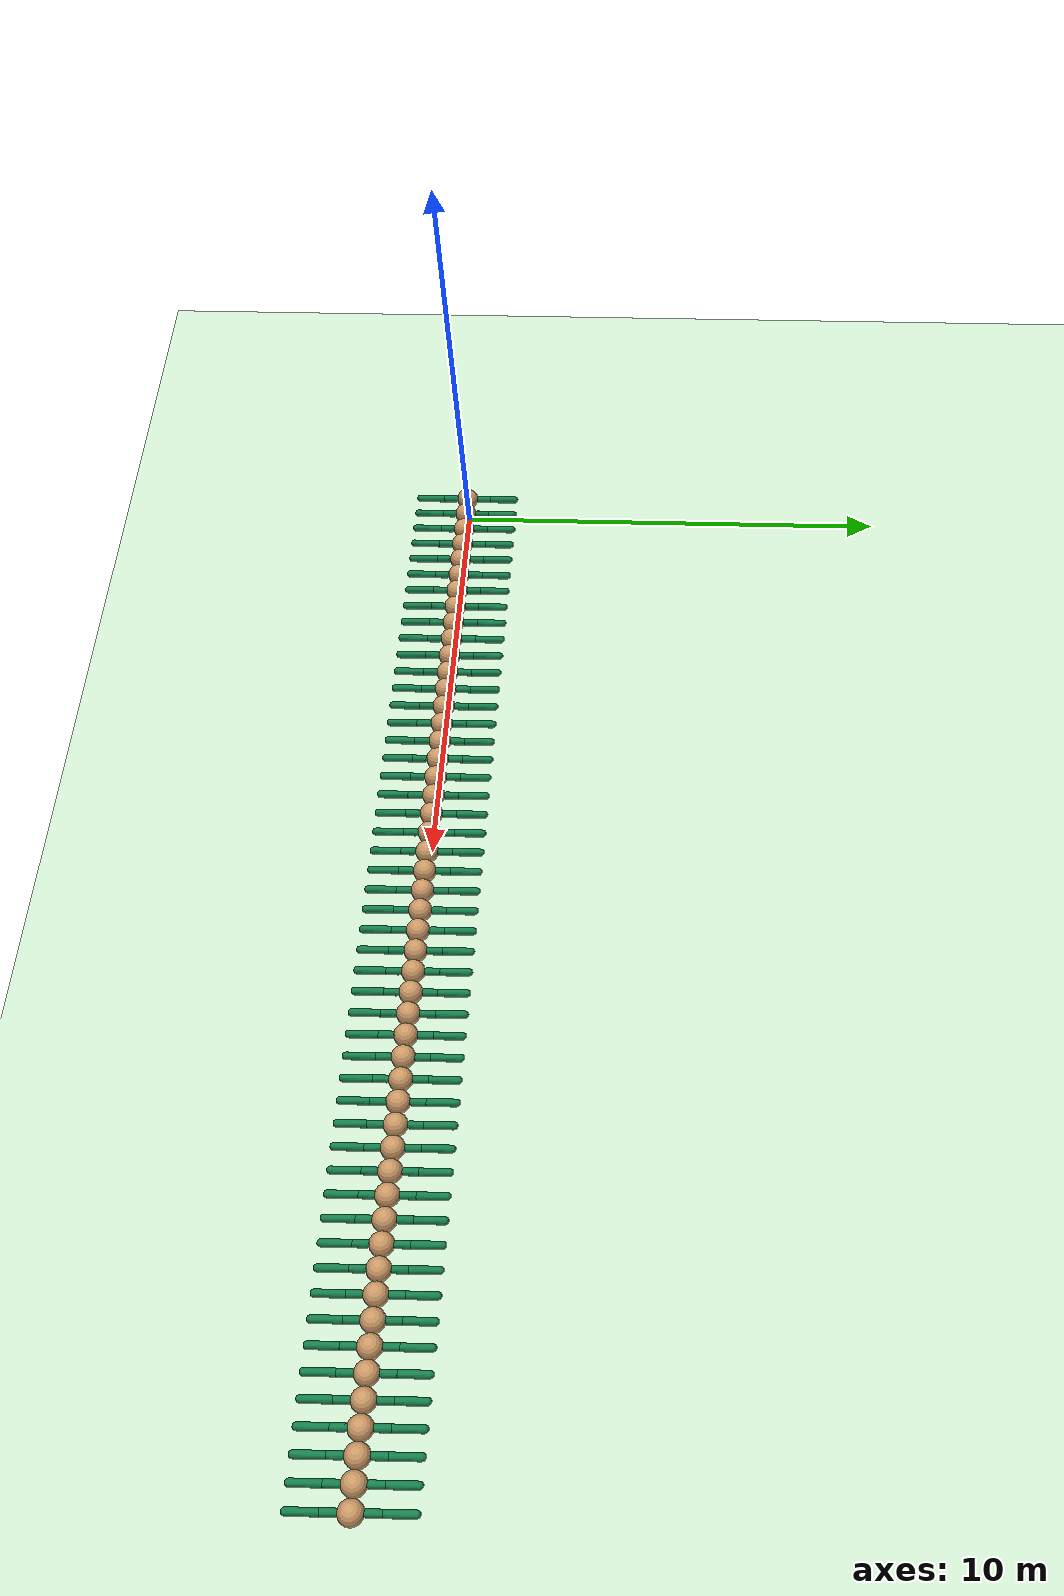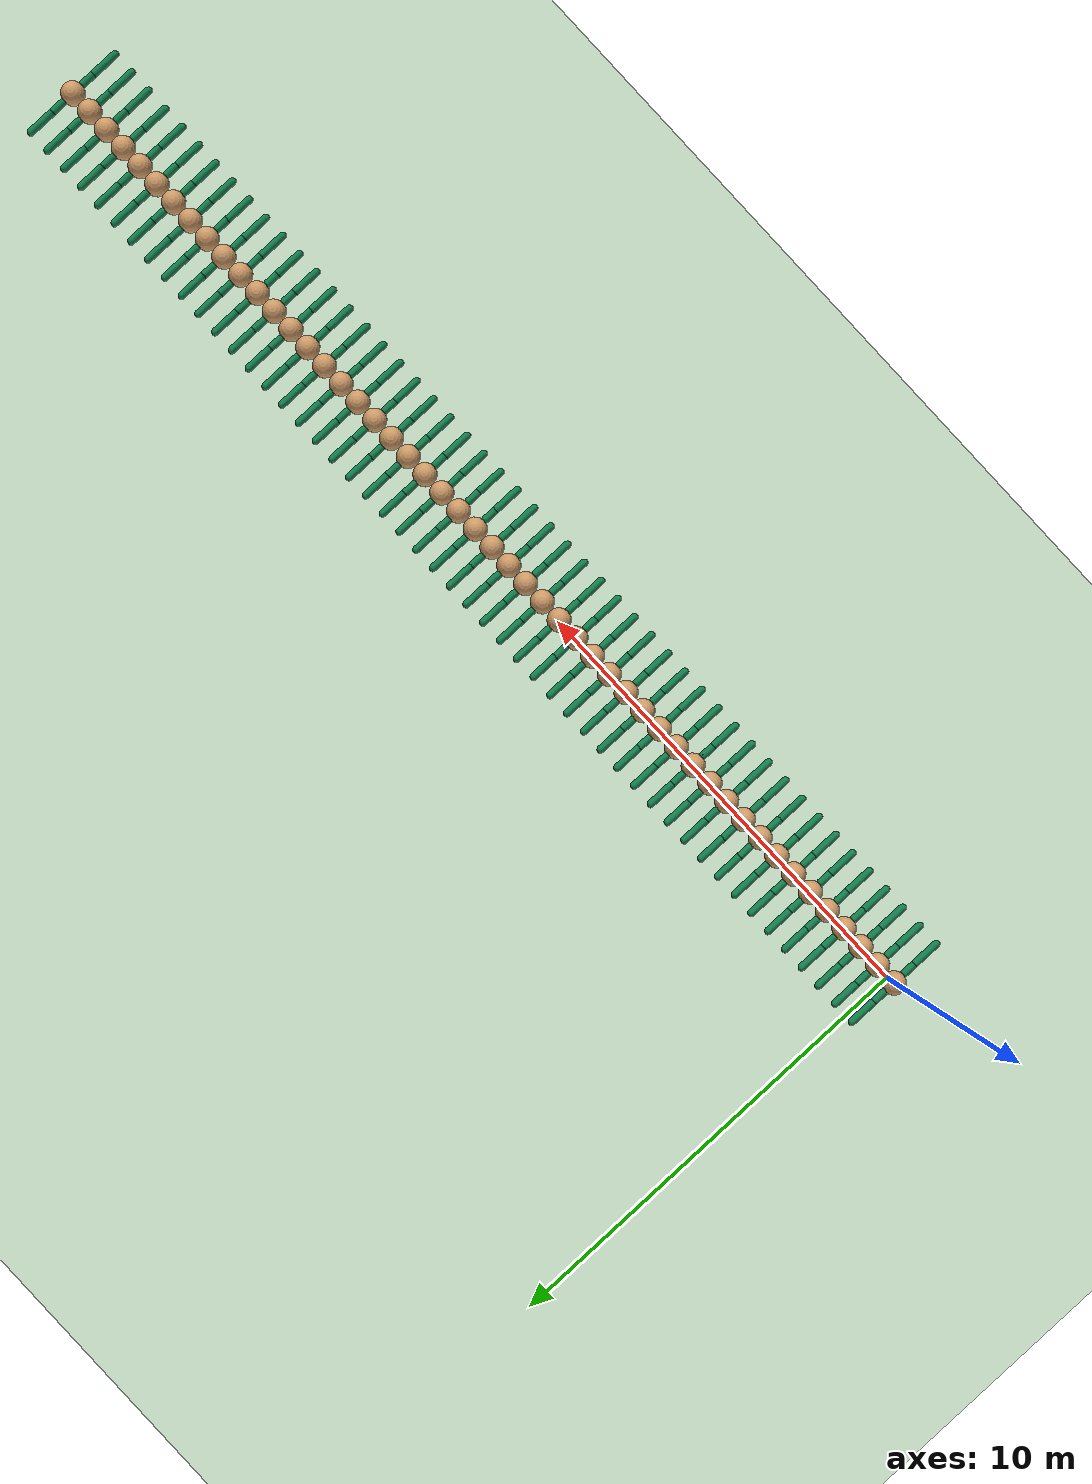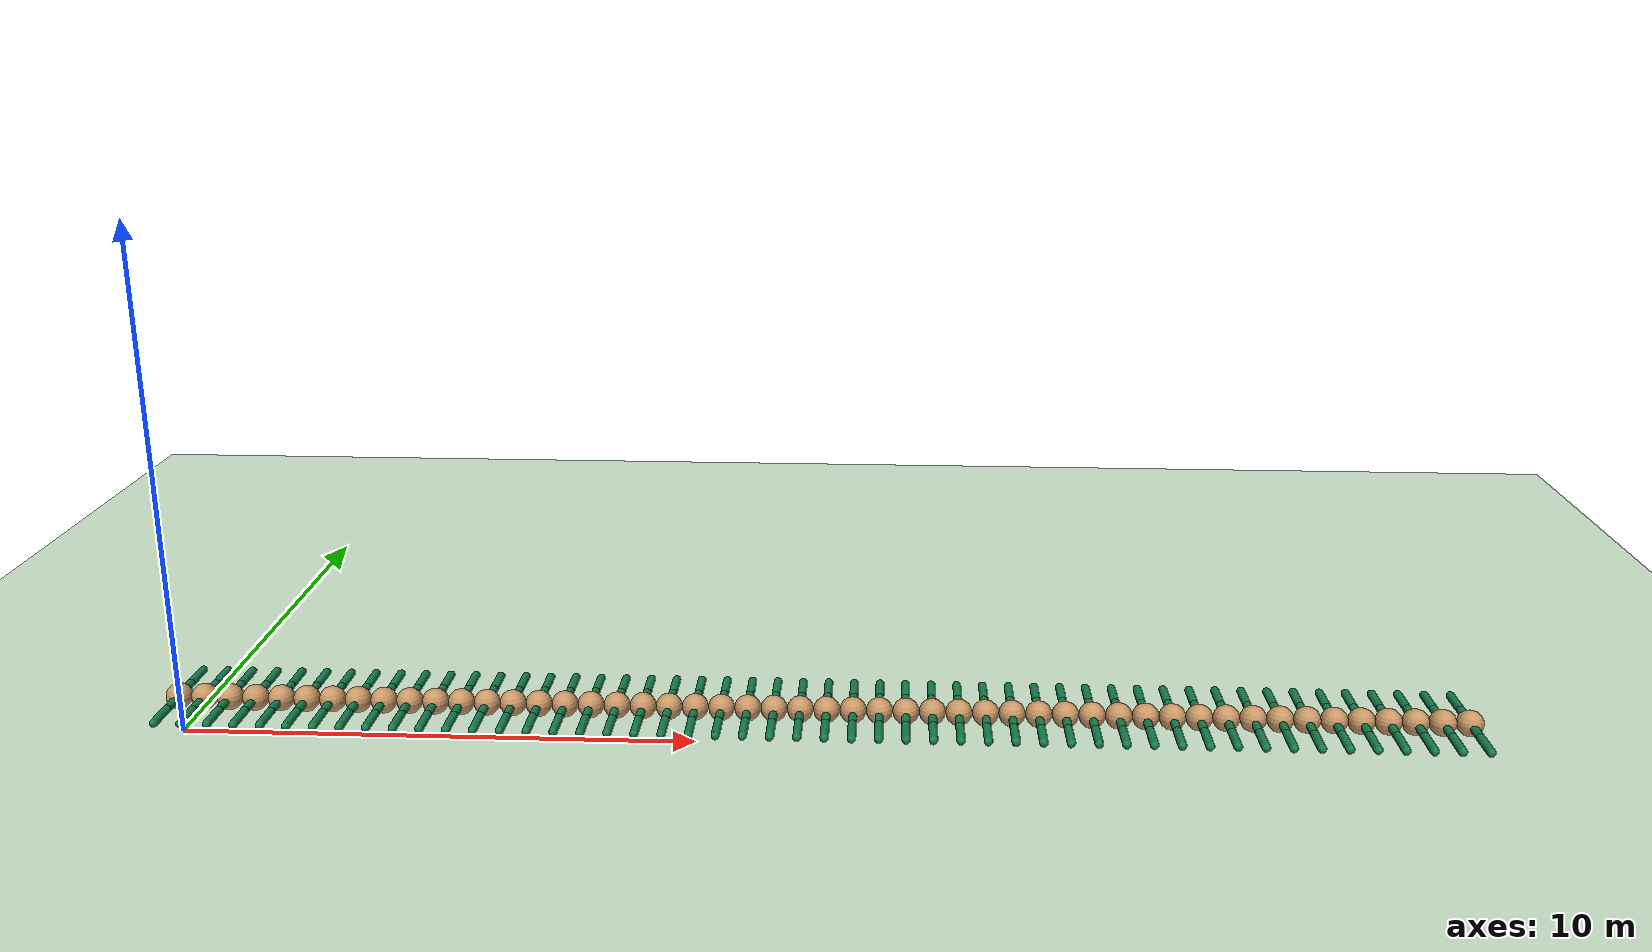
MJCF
<mujoco model="centipede">
    <compiler angle="degree" coordinate="local" inertiafromgeom="true"/>

    <option integrator="RK4" timestep="0.01"/>

    <default>
        <joint armature="1" damping="1" limited="true"/>
        <geom conaffinity="0" condim="3" density="25.0" friction="1.5 0.1 0.1" margin="0.01" rgba="0.8 0.6 0.4 1"/>
    </default>

    <asset>
        <texture builtin="gradient" height="100" rgb1="1 1 1" rgb2="0 0 0" type="skybox" width="100"/>
        <texture builtin="flat" height="1278" mark="cross" markrgb="1 1 1" name="texgeom" random="0.01"
                 rgb1="0.8 0.6 0.4" rgb2="0.8 0.6 0.4" type="cube" width="127"/>
        <texture builtin="checker" height="100" name="texplane" rgb1="0 0 0" rgb2="0.8 0.8 0.8" type="2d" width="100"/>
        <material name="MatPlane" reflectance="0.5" shininess="1" specular="1" texrepeat="60 60" texture="texplane"/>
        <material name="geom" texture="texgeom" texuniform="true"/>
    </asset>

    <worldbody>
        <light cutoff="100" diffuse="1 1 1" dir="-0 0 -1.3" directional="true" exponent="1" pos="0 0 1.3"
               specular=".1 .1 .1"/>
        <geom conaffinity="1" condim="3" material="MatPlane" name="floor" pos="0 0 0" rgba="0.8 0.9 0.8 1"
              size="40 40 40" type="plane"/>
        <body name="torso_0" pos="0 0 0.75">
            <geom name="torsoGeom_0" pos="0 0 0" size="0.25" type="sphere" density="100"/>
            <joint armature="0" damping="0" limited="false" margin="0.01" name="root" pos="0 0 0" type="free"/>

            <body name="legbody_0" pos="0.0 -0.28 0">
                <joint axis="0 0 1" name="lefthip_0" pos="0.0 0.0 0.0" range="-40 40" type="hinge"/>
                <geom fromto="0.0 0.0 0.0 0.0 -0.28 0.0" name="legGeom_0" size="0.08" type="capsule"
                      rgba=".08 .5 .3 1"/>
                <body pos="0 -0.28 0" name="frontFoot_0">
                    <joint axis="1 0 0" name="ankle_0" pos="0.0 0.0 0.0" range="30 100" type="hinge"/>
                    <geom fromto="0.0 0.0 0.0 0 -0.6 0.0" name="ankleGeom_0" size="0.08" type="capsule"
                          rgba=".08 .5 .3 1"/>
                </body>
            </body>

            <body name="legbody_1" pos="0.0 0.28 0">
                <joint axis="0 0 1" name="righthip_1" pos="0.0 0.0 0.0" range="-40 40" type="hinge"/>
                <geom fromto="0.0 0.0 0.0 0.0 0.28 0.0" name="legGeom_1" size="0.08" type="capsule" rgba=".08 .5 .3 1"/>
                <body pos="0 0.28 0" name="frontFoot_1">
                    <joint axis="-1 0 0" name="ankle_1" pos="0.0 0.0 0.0" range="30 100" type="hinge"/>
                    <geom fromto="0.0 0.0 0.0 0 0.6 0.0" name="ankleGeom_1" size="0.08" type="capsule"
                          rgba=".08 .5 .3 1"/>
                </body>
            </body>

            <body name="torso_1" pos="0.50 0 0">
                <geom name="torsoGeom_1" pos="0 0 0" size="0.25" type="sphere" density="100"/>
                <joint axis="0 0 1" name="body_1" pos="-0.25 0.0 0.0" range="-20 20" type="hinge"/>
                <joint axis="0 1 0" name="bodyupdown_1" pos="-0.25 0.0 0.0" range="-10 30" type="hinge"/>

                <body name="legbody_2" pos="0.0 -0.28 0">
                    <joint axis="0 0 1" name="lefthip_2" pos="0.0 0.0 0.0" range="-40 40" type="hinge"/>
                    <geom fromto="0.0 0.0 0.0 0.0 -0.28 0.0" name="legGeom_2" size="0.08" type="capsule"
                          rgba=".08 .5 .3 1"/>
                    <body pos="0 -0.28 0" name="frontFoot_2">
                        <joint axis="1 0 0" name="ankle_2" pos="0.0 0.0 0.0" range="30 100" type="hinge"/>
                        <geom fromto="0.0 0.0 0.0 0 -0.6 0.0" name="ankleGeom_2" size="0.08" type="capsule"
                              rgba=".08 .5 .3 1"/>
                    </body>
                </body>

                <body name="legbody_3" pos="0.0 0.28 0">
                    <joint axis="0 0 1" name="righthip_3" pos="0.0 0.0 0.0" range="-40 40" type="hinge"/>
                    <geom fromto="0.0 0.0 0.0 0.0 0.28 0.0" name="legGeom_3" size="0.08" type="capsule"
                          rgba=".08 .5 .3 1"/>
                    <body pos="0 0.28 0" name="frontFoot_3">
                        <joint axis="-1 0 0" name="ankle_3" pos="0.0 0.0 0.0" range="30 100" type="hinge"/>
                        <geom fromto="0.0 0.0 0.0 0 0.6 0.0" name="ankleGeom_3" size="0.08" type="capsule"
                              rgba=".08 .5 .3 1"/>
                    </body>
                </body>

                <body name="torso_2" pos="0.50 0 0">
                    <geom name="torsoGeom_2" pos="0 0 0" size="0.25" type="sphere" density="100"/>
                    <joint axis="0 0 1" name="body_2" pos="-0.25 0.0 0.0" range="-20 20" type="hinge"/>
                    <joint axis="0 1 0" name="bodyupdown_2" pos="-0.25 0.0 0.0" range="-10 30" type="hinge"/>

                    <body name="legbody_4" pos="0.0 -0.28 0">
                        <joint axis="0 0 1" name="lefthip_4" pos="0.0 0.0 0.0" range="-40 40" type="hinge"/>
                        <geom fromto="0.0 0.0 0.0 0.0 -0.28 0.0" name="legGeom_4" size="0.08" type="capsule"
                              rgba=".08 .5 .3 1"/>
                        <body pos="0 -0.28 0" name="frontFoot_4">
                            <joint axis="1 0 0" name="ankle_4" pos="0.0 0.0 0.0" range="30 100" type="hinge"/>
                            <geom fromto="0.0 0.0 0.0 0 -0.6 0.0" name="ankleGeom_4" size="0.08" type="capsule"
                                  rgba=".08 .5 .3 1"/>
                        </body>
                    </body>

                    <body name="legbody_5" pos="0.0 0.28 0">
                        <joint axis="0 0 1" name="righthip_5" pos="0.0 0.0 0.0" range="-40 40" type="hinge"/>
                        <geom fromto="0.0 0.0 0.0 0.0 0.28 0.0" name="legGeom_5" size="0.08" type="capsule"
                              rgba=".08 .5 .3 1"/>
                        <body pos="0 0.28 0" name="frontFoot_5">
                            <joint axis="-1 0 0" name="ankle_5" pos="0.0 0.0 0.0" range="30 100" type="hinge"/>
                            <geom fromto="0.0 0.0 0.0 0 0.6 0.0" name="ankleGeom_5" size="0.08" type="capsule"
                                  rgba=".08 .5 .3 1"/>
                        </body>
                    </body>

                    <body name="torso_3" pos="0.50 0 0">
                        <geom name="torsoGeom_3" pos="0 0 0" size="0.25" type="sphere" density="100"/>
                        <joint axis="0 0 1" name="body_3" pos="-0.25 0.0 0.0" range="-20 20" type="hinge"/>
                        <joint axis="0 1 0" name="bodyupdown_3" pos="-0.25 0.0 0.0" range="-10 30" type="hinge"/>

                        <body name="legbody_6" pos="0.0 -0.28 0">
                            <joint axis="0 0 1" name="lefthip_6" pos="0.0 0.0 0.0" range="-40 40" type="hinge"/>
                            <geom fromto="0.0 0.0 0.0 0.0 -0.28 0.0" name="legGeom_6" size="0.08" type="capsule"
                                  rgba=".08 .5 .3 1"/>
                            <body pos="0 -0.28 0" name="frontFoot_6">
                                <joint axis="1 0 0" name="ankle_6" pos="0.0 0.0 0.0" range="30 100" type="hinge"/>
                                <geom fromto="0.0 0.0 0.0 0 -0.6 0.0" name="ankleGeom_6" size="0.08" type="capsule"
                                      rgba=".08 .5 .3 1"/>
                            </body>
                        </body>

                        <body name="legbody_7" pos="0.0 0.28 0">
                            <joint axis="0 0 1" name="righthip_7" pos="0.0 0.0 0.0" range="-40 40" type="hinge"/>
                            <geom fromto="0.0 0.0 0.0 0.0 0.28 0.0" name="legGeom_7" size="0.08" type="capsule"
                                  rgba=".08 .5 .3 1"/>
                            <body pos="0 0.28 0" name="frontFoot_7">
                                <joint axis="-1 0 0" name="ankle_7" pos="0.0 0.0 0.0" range="30 100" type="hinge"/>
                                <geom fromto="0.0 0.0 0.0 0 0.6 0.0" name="ankleGeom_7" size="0.08" type="capsule"
                                      rgba=".08 .5 .3 1"/>
                            </body>
                        </body>

                        <body name="torso_4" pos="0.50 0 0">
                            <geom name="torsoGeom_4" pos="0 0 0" size="0.25" type="sphere" density="100"/>
                            <joint axis="0 0 1" name="body_4" pos="-0.25 0.0 0.0" range="-20 20" type="hinge"/>
                            <joint axis="0 1 0" name="bodyupdown_4" pos="-0.25 0.0 0.0" range="-10 30" type="hinge"/>

                            <body name="legbody_8" pos="0.0 -0.28 0">
                                <joint axis="0 0 1" name="lefthip_8" pos="0.0 0.0 0.0" range="-40 40" type="hinge"/>
                                <geom fromto="0.0 0.0 0.0 0.0 -0.28 0.0" name="legGeom_8" size="0.08" type="capsule"
                                      rgba=".08 .5 .3 1"/>
                                <body pos="0 -0.28 0" name="frontFoot_8">
                                    <joint axis="1 0 0" name="ankle_8" pos="0.0 0.0 0.0" range="30 100" type="hinge"/>
                                    <geom fromto="0.0 0.0 0.0 0 -0.6 0.0" name="ankleGeom_8" size="0.08" type="capsule"
                                          rgba=".08 .5 .3 1"/>
                                </body>
                            </body>

                            <body name="legbody_9" pos="0.0 0.28 0">
                                <joint axis="0 0 1" name="righthip_9" pos="0.0 0.0 0.0" range="-40 40" type="hinge"/>
                                <geom fromto="0.0 0.0 0.0 0.0 0.28 0.0" name="legGeom_9" size="0.08" type="capsule"
                                      rgba=".08 .5 .3 1"/>
                                <body pos="0 0.28 0" name="frontFoot_9">
                                    <joint axis="-1 0 0" name="ankle_9" pos="0.0 0.0 0.0" range="30 100" type="hinge"/>
                                    <geom fromto="0.0 0.0 0.0 0 0.6 0.0" name="ankleGeom_9" size="0.08" type="capsule"
                                          rgba=".08 .5 .3 1"/>
                                </body>
                            </body>

                            <body name="torso_5" pos="0.50 0 0">
                                <geom name="torsoGeom_5" pos="0 0 0" size="0.25" type="sphere" density="100"/>
                                <joint axis="0 0 1" name="body_5" pos="-0.25 0.0 0.0" range="-20 20" type="hinge"/>
                                <joint axis="0 1 0" name="bodyupdown_5" pos="-0.25 0.0 0.0" range="-10 30"
                                       type="hinge"/>

                                <body name="legbody_10" pos="0.0 -0.28 0">
                                    <joint axis="0 0 1" name="lefthip_10" pos="0.0 0.0 0.0" range="-40 40"
                                           type="hinge"/>
                                    <geom fromto="0.0 0.0 0.0 0.0 -0.28 0.0" name="legGeom_10" size="0.08"
                                          type="capsule" rgba=".08 .5 .3 1"/>
                                    <body pos="0 -0.28 0" name="frontFoot_10">
                                        <joint axis="1 0 0" name="ankle_10" pos="0.0 0.0 0.0" range="30 100"
                                               type="hinge"/>
                                        <geom fromto="0.0 0.0 0.0 0 -0.6 0.0" name="ankleGeom_10" size="0.08"
                                              type="capsule" rgba=".08 .5 .3 1"/>
                                    </body>
                                </body>

                                <body name="legbody_11" pos="0.0 0.28 0">
                                    <joint axis="0 0 1" name="righthip_11" pos="0.0 0.0 0.0" range="-40 40"
                                           type="hinge"/>
                                    <geom fromto="0.0 0.0 0.0 0.0 0.28 0.0" name="legGeom_11" size="0.08" type="capsule"
                                          rgba=".08 .5 .3 1"/>
                                    <body pos="0 0.28 0" name="frontFoot_11">
                                        <joint axis="-1 0 0" name="ankle_11" pos="0.0 0.0 0.0" range="30 100"
                                               type="hinge"/>
                                        <geom fromto="0.0 0.0 0.0 0 0.6 0.0" name="ankleGeom_11" size="0.08"
                                              type="capsule" rgba=".08 .5 .3 1"/>
                                    </body>
                                </body>

                                <body name="torso_6" pos="0.50 0 0">
                                    <geom name="torsoGeom_6" pos="0 0 0" size="0.25" type="sphere" density="100"/>
                                    <joint axis="0 0 1" name="body_6" pos="-0.25 0.0 0.0" range="-20 20" type="hinge"/>
                                    <joint axis="0 1 0" name="bodyupdown_6" pos="-0.25 0.0 0.0" range="-10 30"
                                           type="hinge"/>

                                    <body name="legbody_12" pos="0.0 -0.28 0">
                                        <joint axis="0 0 1" name="lefthip_12" pos="0.0 0.0 0.0" range="-40 40"
                                               type="hinge"/>
                                        <geom fromto="0.0 0.0 0.0 0.0 -0.28 0.0" name="legGeom_12" size="0.08"
                                              type="capsule" rgba=".08 .5 .3 1"/>
                                        <body pos="0 -0.28 0" name="frontFoot_12">
                                            <joint axis="1 0 0" name="ankle_12" pos="0.0 0.0 0.0" range="30 100"
                                                   type="hinge"/>
                                            <geom fromto="0.0 0.0 0.0 0 -0.6 0.0" name="ankleGeom_12" size="0.08"
                                                  type="capsule" rgba=".08 .5 .3 1"/>
                                        </body>
                                    </body>

                                    <body name="legbody_13" pos="0.0 0.28 0">
                                        <joint axis="0 0 1" name="righthip_13" pos="0.0 0.0 0.0" range="-40 40"
                                               type="hinge"/>
                                        <geom fromto="0.0 0.0 0.0 0.0 0.28 0.0" name="legGeom_13" size="0.08"
                                              type="capsule" rgba=".08 .5 .3 1"/>
                                        <body pos="0 0.28 0" name="frontFoot_13">
                                            <joint axis="-1 0 0" name="ankle_13" pos="0.0 0.0 0.0" range="30 100"
                                                   type="hinge"/>
                                            <geom fromto="0.0 0.0 0.0 0 0.6 0.0" name="ankleGeom_13" size="0.08"
                                                  type="capsule" rgba=".08 .5 .3 1"/>
                                        </body>
                                    </body>

                                    <body name="torso_7" pos="0.50 0 0">
                                        <geom name="torsoGeom_7" pos="0 0 0" size="0.25" type="sphere" density="100"/>
                                        <joint axis="0 0 1" name="body_7" pos="-0.25 0.0 0.0" range="-20 20"
                                               type="hinge"/>
                                        <joint axis="0 1 0" name="bodyupdown_7" pos="-0.25 0.0 0.0" range="-10 30"
                                               type="hinge"/>

                                        <body name="legbody_14" pos="0.0 -0.28 0">
                                            <joint axis="0 0 1" name="lefthip_14" pos="0.0 0.0 0.0" range="-40 40"
                                                   type="hinge"/>
                                            <geom fromto="0.0 0.0 0.0 0.0 -0.28 0.0" name="legGeom_14" size="0.08"
                                                  type="capsule" rgba=".08 .5 .3 1"/>
                                            <body pos="0 -0.28 0" name="frontFoot_14">
                                                <joint axis="1 0 0" name="ankle_14" pos="0.0 0.0 0.0" range="30 100"
                                                       type="hinge"/>
                                                <geom fromto="0.0 0.0 0.0 0 -0.6 0.0" name="ankleGeom_14" size="0.08"
                                                      type="capsule" rgba=".08 .5 .3 1"/>
                                            </body>
                                        </body>

                                        <body name="legbody_15" pos="0.0 0.28 0">
                                            <joint axis="0 0 1" name="righthip_15" pos="0.0 0.0 0.0" range="-40 40"
                                                   type="hinge"/>
                                            <geom fromto="0.0 0.0 0.0 0.0 0.28 0.0" name="legGeom_15" size="0.08"
                                                  type="capsule" rgba=".08 .5 .3 1"/>
                                            <body pos="0 0.28 0" name="frontFoot_15">
                                                <joint axis="-1 0 0" name="ankle_15" pos="0.0 0.0 0.0" range="30 100"
                                                       type="hinge"/>
                                                <geom fromto="0.0 0.0 0.0 0 0.6 0.0" name="ankleGeom_15" size="0.08"
                                                      type="capsule" rgba=".08 .5 .3 1"/>
                                            </body>
                                        </body>

                                        <body name="torso_8" pos="0.50 0 0">
                                            <geom name="torsoGeom_8" pos="0 0 0" size="0.25" type="sphere"
                                                  density="100"/>
                                            <joint axis="0 0 1" name="body_8" pos="-0.25 0.0 0.0" range="-20 20"
                                                   type="hinge"/>
                                            <joint axis="0 1 0" name="bodyupdown_8" pos="-0.25 0.0 0.0" range="-10 30"
                                                   type="hinge"/>

                                            <body name="legbody_16" pos="0.0 -0.28 0">
                                                <joint axis="0 0 1" name="lefthip_16" pos="0.0 0.0 0.0" range="-40 40"
                                                       type="hinge"/>
                                                <geom fromto="0.0 0.0 0.0 0.0 -0.28 0.0" name="legGeom_16" size="0.08"
                                                      type="capsule" rgba=".08 .5 .3 1"/>
                                                <body pos="0 -0.28 0" name="frontFoot_16">
                                                    <joint axis="1 0 0" name="ankle_16" pos="0.0 0.0 0.0" range="30 100"
                                                           type="hinge"/>
                                                    <geom fromto="0.0 0.0 0.0 0 -0.6 0.0" name="ankleGeom_16"
                                                          size="0.08" type="capsule" rgba=".08 .5 .3 1"/>
                                                </body>
                                            </body>

                                            <body name="legbody_17" pos="0.0 0.28 0">
                                                <joint axis="0 0 1" name="righthip_17" pos="0.0 0.0 0.0" range="-40 40"
                                                       type="hinge"/>
                                                <geom fromto="0.0 0.0 0.0 0.0 0.28 0.0" name="legGeom_17" size="0.08"
                                                      type="capsule" rgba=".08 .5 .3 1"/>
                                                <body pos="0 0.28 0" name="frontFoot_17">
                                                    <joint axis="-1 0 0" name="ankle_17" pos="0.0 0.0 0.0"
                                                           range="30 100" type="hinge"/>
                                                    <geom fromto="0.0 0.0 0.0 0 0.6 0.0" name="ankleGeom_17" size="0.08"
                                                          type="capsule" rgba=".08 .5 .3 1"/>
                                                </body>
                                            </body>

                                            <body name="torso_9" pos="0.50 0 0">
                                                <geom name="torsoGeom_9" pos="0 0 0" size="0.25" type="sphere"
                                                      density="100"/>
                                                <joint axis="0 0 1" name="body_9" pos="-0.25 0.0 0.0" range="-20 20"
                                                       type="hinge"/>
                                                <joint axis="0 1 0" name="bodyupdown_9" pos="-0.25 0.0 0.0"
                                                       range="-10 30" type="hinge"/>

                                                <body name="legbody_18" pos="0.0 -0.28 0">
                                                    <joint axis="0 0 1" name="lefthip_18" pos="0.0 0.0 0.0"
                                                           range="-40 40" type="hinge"/>
                                                    <geom fromto="0.0 0.0 0.0 0.0 -0.28 0.0" name="legGeom_18"
                                                          size="0.08" type="capsule" rgba=".08 .5 .3 1"/>
                                                    <body pos="0 -0.28 0" name="frontFoot_18">
                                                        <joint axis="1 0 0" name="ankle_18" pos="0.0 0.0 0.0"
                                                               range="30 100" type="hinge"/>
                                                        <geom fromto="0.0 0.0 0.0 0 -0.6 0.0" name="ankleGeom_18"
                                                              size="0.08" type="capsule" rgba=".08 .5 .3 1"/>
                                                    </body>
                                                </body>

                                                <body name="legbody_19" pos="0.0 0.28 0">
                                                    <joint axis="0 0 1" name="righthip_19" pos="0.0 0.0 0.0"
                                                           range="-40 40" type="hinge"/>
                                                    <geom fromto="0.0 0.0 0.0 0.0 0.28 0.0" name="legGeom_19"
                                                          size="0.08" type="capsule" rgba=".08 .5 .3 1"/>
                                                    <body pos="0 0.28 0" name="frontFoot_19">
                                                        <joint axis="-1 0 0" name="ankle_19" pos="0.0 0.0 0.0"
                                                               range="30 100" type="hinge"/>
                                                        <geom fromto="0.0 0.0 0.0 0 0.6 0.0" name="ankleGeom_19"
                                                              size="0.08" type="capsule" rgba=".08 .5 .3 1"/>
                                                    </body>
                                                </body>

                                                <body name="torso_10" pos="0.50 0 0">
                                                    <geom name="torsoGeom_10" pos="0 0 0" size="0.25" type="sphere"
                                                          density="100"/>
                                                    <joint axis="0 0 1" name="body_10" pos="-0.25 0.0 0.0"
                                                           range="-20 20" type="hinge"/>
                                                    <joint axis="0 1 0" name="bodyupdown_10" pos="-0.25 0.0 0.0"
                                                           range="-10 30" type="hinge"/>

                                                    <body name="legbody_20" pos="0.0 -0.28 0">
                                                        <joint axis="0 0 1" name="lefthip_20" pos="0.0 0.0 0.0"
                                                               range="-40 40" type="hinge"/>
                                                        <geom fromto="0.0 0.0 0.0 0.0 -0.28 0.0" name="legGeom_20"
                                                              size="0.08" type="capsule" rgba=".08 .5 .3 1"/>
                                                        <body pos="0 -0.28 0" name="frontFoot_20">
                                                            <joint axis="1 0 0" name="ankle_20" pos="0.0 0.0 0.0"
                                                                   range="30 100" type="hinge"/>
                                                            <geom fromto="0.0 0.0 0.0 0 -0.6 0.0" name="ankleGeom_20"
                                                                  size="0.08" type="capsule" rgba=".08 .5 .3 1"/>
                                                        </body>
                                                    </body>

                                                    <body name="legbody_21" pos="0.0 0.28 0">
                                                        <joint axis="0 0 1" name="righthip_21" pos="0.0 0.0 0.0"
                                                               range="-40 40" type="hinge"/>
                                                        <geom fromto="0.0 0.0 0.0 0.0 0.28 0.0" name="legGeom_21"
                                                              size="0.08" type="capsule" rgba=".08 .5 .3 1"/>
                                                        <body pos="0 0.28 0" name="frontFoot_21">
                                                            <joint axis="-1 0 0" name="ankle_21" pos="0.0 0.0 0.0"
                                                                   range="30 100" type="hinge"/>
                                                            <geom fromto="0.0 0.0 0.0 0 0.6 0.0" name="ankleGeom_21"
                                                                  size="0.08" type="capsule" rgba=".08 .5 .3 1"/>
                                                        </body>
                                                    </body>

                                                    <body name="torso_11" pos="0.50 0 0">
                                                        <geom name="torsoGeom_11" pos="0 0 0" size="0.25" type="sphere"
                                                              density="100"/>
                                                        <joint axis="0 0 1" name="body_11" pos="-0.25 0.0 0.0"
                                                               range="-20 20" type="hinge"/>
                                                        <joint axis="0 1 0" name="bodyupdown_11" pos="-0.25 0.0 0.0"
                                                               range="-10 30" type="hinge"/>

                                                        <body name="legbody_22" pos="0.0 -0.28 0">
                                                            <joint axis="0 0 1" name="lefthip_22" pos="0.0 0.0 0.0"
                                                                   range="-40 40" type="hinge"/>
                                                            <geom fromto="0.0 0.0 0.0 0.0 -0.28 0.0" name="legGeom_22"
                                                                  size="0.08" type="capsule" rgba=".08 .5 .3 1"/>
                                                            <body pos="0 -0.28 0" name="frontFoot_22">
                                                                <joint axis="1 0 0" name="ankle_22" pos="0.0 0.0 0.0"
                                                                       range="30 100" type="hinge"/>
                                                                <geom fromto="0.0 0.0 0.0 0 -0.6 0.0"
                                                                      name="ankleGeom_22" size="0.08" type="capsule"
                                                                      rgba=".08 .5 .3 1"/>
                                                            </body>
                                                        </body>

                                                        <body name="legbody_23" pos="0.0 0.28 0">
                                                            <joint axis="0 0 1" name="righthip_23" pos="0.0 0.0 0.0"
                                                                   range="-40 40" type="hinge"/>
                                                            <geom fromto="0.0 0.0 0.0 0.0 0.28 0.0" name="legGeom_23"
                                                                  size="0.08" type="capsule" rgba=".08 .5 .3 1"/>
                                                            <body pos="0 0.28 0" name="frontFoot_23">
                                                                <joint axis="-1 0 0" name="ankle_23" pos="0.0 0.0 0.0"
                                                                       range="30 100" type="hinge"/>
                                                                <geom fromto="0.0 0.0 0.0 0 0.6 0.0" name="ankleGeom_23"
                                                                      size="0.08" type="capsule" rgba=".08 .5 .3 1"/>
                                                            </body>
                                                        </body>

                                                        <body name="torso_12" pos="0.50 0 0">
                                                            <geom name="torsoGeom_12" pos="0 0 0" size="0.25"
                                                                  type="sphere" density="100"/>
                                                            <joint axis="0 0 1" name="body_12" pos="-0.25 0.0 0.0"
                                                                   range="-20 20" type="hinge"/>
                                                            <joint axis="0 1 0" name="bodyupdown_12" pos="-0.25 0.0 0.0"
                                                                   range="-10 30" type="hinge"/>

                                                            <body name="legbody_24" pos="0.0 -0.28 0">
                                                                <joint axis="0 0 1" name="lefthip_24" pos="0.0 0.0 0.0"
                                                                       range="-40 40" type="hinge"/>
                                                                <geom fromto="0.0 0.0 0.0 0.0 -0.28 0.0"
                                                                      name="legGeom_24" size="0.08" type="capsule"
                                                                      rgba=".08 .5 .3 1"/>
                                                                <body pos="0 -0.28 0" name="frontFoot_24">
                                                                    <joint axis="1 0 0" name="ankle_24"
                                                                           pos="0.0 0.0 0.0" range="30 100"
                                                                           type="hinge"/>
                                                                    <geom fromto="0.0 0.0 0.0 0 -0.6 0.0"
                                                                          name="ankleGeom_24" size="0.08" type="capsule"
                                                                          rgba=".08 .5 .3 1"/>
                                                                </body>
                                                            </body>

                                                            <body name="legbody_25" pos="0.0 0.28 0">
                                                                <joint axis="0 0 1" name="righthip_25" pos="0.0 0.0 0.0"
                                                                       range="-40 40" type="hinge"/>
                                                                <geom fromto="0.0 0.0 0.0 0.0 0.28 0.0"
                                                                      name="legGeom_25" size="0.08" type="capsule"
                                                                      rgba=".08 .5 .3 1"/>
                                                                <body pos="0 0.28 0" name="frontFoot_25">
                                                                    <joint axis="-1 0 0" name="ankle_25"
                                                                           pos="0.0 0.0 0.0" range="30 100"
                                                                           type="hinge"/>
                                                                    <geom fromto="0.0 0.0 0.0 0 0.6 0.0"
                                                                          name="ankleGeom_25" size="0.08" type="capsule"
                                                                          rgba=".08 .5 .3 1"/>
                                                                </body>
                                                            </body>

                                                            <body name="torso_13" pos="0.50 0 0">
                                                                <geom name="torsoGeom_13" pos="0 0 0" size="0.25"
                                                                      type="sphere" density="100"/>
                                                                <joint axis="0 0 1" name="body_13" pos="-0.25 0.0 0.0"
                                                                       range="-20 20" type="hinge"/>
                                                                <joint axis="0 1 0" name="bodyupdown_13"
                                                                       pos="-0.25 0.0 0.0" range="-10 30" type="hinge"/>

                                                                <body name="legbody_26" pos="0.0 -0.28 0">
                                                                    <joint axis="0 0 1" name="lefthip_26"
                                                                           pos="0.0 0.0 0.0" range="-40 40"
                                                                           type="hinge"/>
                                                                    <geom fromto="0.0 0.0 0.0 0.0 -0.28 0.0"
                                                                          name="legGeom_26" size="0.08" type="capsule"
                                                                          rgba=".08 .5 .3 1"/>
                                                                    <body pos="0 -0.28 0" name="frontFoot_26">
                                                                        <joint axis="1 0 0" name="ankle_26"
                                                                               pos="0.0 0.0 0.0" range="30 100"
                                                                               type="hinge"/>
                                                                        <geom fromto="0.0 0.0 0.0 0 -0.6 0.0"
                                                                              name="ankleGeom_26" size="0.08"
                                                                              type="capsule" rgba=".08 .5 .3 1"/>
                                                                    </body>
                                                                </body>

                                                                <body name="legbody_27" pos="0.0 0.28 0">
                                                                    <joint axis="0 0 1" name="righthip_27"
                                                                           pos="0.0 0.0 0.0" range="-40 40"
                                                                           type="hinge"/>
                                                                    <geom fromto="0.0 0.0 0.0 0.0 0.28 0.0"
                                                                          name="legGeom_27" size="0.08" type="capsule"
                                                                          rgba=".08 .5 .3 1"/>
                                                                    <body pos="0 0.28 0" name="frontFoot_27">
                                                                        <joint axis="-1 0 0" name="ankle_27"
                                                                               pos="0.0 0.0 0.0" range="30 100"
                                                                               type="hinge"/>
                                                                        <geom fromto="0.0 0.0 0.0 0 0.6 0.0"
                                                                              name="ankleGeom_27" size="0.08"
                                                                              type="capsule" rgba=".08 .5 .3 1"/>
                                                                    </body>
                                                                </body>

                                                                <body name="torso_14" pos="0.50 0 0">
                                                                    <geom name="torsoGeom_14" pos="0 0 0" size="0.25"
                                                                          type="sphere" density="100"/>
                                                                    <joint axis="0 0 1" name="body_14"
                                                                           pos="-0.25 0.0 0.0" range="-20 20"
                                                                           type="hinge"/>
                                                                    <joint axis="0 1 0" name="bodyupdown_14"
                                                                           pos="-0.25 0.0 0.0" range="-10 30"
                                                                           type="hinge"/>

                                                                    <body name="legbody_28" pos="0.0 -0.28 0">
                                                                        <joint axis="0 0 1" name="lefthip_28"
                                                                               pos="0.0 0.0 0.0" range="-40 40"
                                                                               type="hinge"/>
                                                                        <geom fromto="0.0 0.0 0.0 0.0 -0.28 0.0"
                                                                              name="legGeom_28" size="0.08"
                                                                              type="capsule" rgba=".08 .5 .3 1"/>
                                                                        <body pos="0 -0.28 0" name="frontFoot_28">
                                                                            <joint axis="1 0 0" name="ankle_28"
                                                                                   pos="0.0 0.0 0.0" range="30 100"
                                                                                   type="hinge"/>
                                                                            <geom fromto="0.0 0.0 0.0 0 -0.6 0.0"
                                                                                  name="ankleGeom_28" size="0.08"
                                                                                  type="capsule" rgba=".08 .5 .3 1"/>
                                                                        </body>
                                                                    </body>

                                                                    <body name="legbody_29" pos="0.0 0.28 0">
                                                                        <joint axis="0 0 1" name="righthip_29"
                                                                               pos="0.0 0.0 0.0" range="-40 40"
                                                                               type="hinge"/>
                                                                        <geom fromto="0.0 0.0 0.0 0.0 0.28 0.0"
                                                                              name="legGeom_29" size="0.08"
                                                                              type="capsule" rgba=".08 .5 .3 1"/>
                                                                        <body pos="0 0.28 0" name="frontFoot_29">
                                                                            <joint axis="-1 0 0" name="ankle_29"
                                                                                   pos="0.0 0.0 0.0" range="30 100"
                                                                                   type="hinge"/>
                                                                            <geom fromto="0.0 0.0 0.0 0 0.6 0.0"
                                                                                  name="ankleGeom_29" size="0.08"
                                                                                  type="capsule" rgba=".08 .5 .3 1"/>
                                                                        </body>
                                                                    </body>

                                                                    <body name="torso_15" pos="0.50 0 0">
                                                                        <geom name="torsoGeom_15" pos="0 0 0"
                                                                              size="0.25" type="sphere" density="100"/>
                                                                        <joint axis="0 0 1" name="body_15"
                                                                               pos="-0.25 0.0 0.0" range="-20 20"
                                                                               type="hinge"/>
                                                                        <joint axis="0 1 0" name="bodyupdown_15"
                                                                               pos="-0.25 0.0 0.0" range="-10 30"
                                                                               type="hinge"/>

                                                                        <body name="legbody_30" pos="0.0 -0.28 0">
                                                                            <joint axis="0 0 1" name="lefthip_30"
                                                                                   pos="0.0 0.0 0.0" range="-40 40"
                                                                                   type="hinge"/>
                                                                            <geom fromto="0.0 0.0 0.0 0.0 -0.28 0.0"
                                                                                  name="legGeom_30" size="0.08"
                                                                                  type="capsule" rgba=".08 .5 .3 1"/>
                                                                            <body pos="0 -0.28 0" name="frontFoot_30">
                                                                                <joint axis="1 0 0" name="ankle_30"
                                                                                       pos="0.0 0.0 0.0" range="30 100"
                                                                                       type="hinge"/>
                                                                                <geom fromto="0.0 0.0 0.0 0 -0.6 0.0"
                                                                                      name="ankleGeom_30" size="0.08"
                                                                                      type="capsule"
                                                                                      rgba=".08 .5 .3 1"/>
                                                                            </body>
                                                                        </body>

                                                                        <body name="legbody_31" pos="0.0 0.28 0">
                                                                            <joint axis="0 0 1" name="righthip_31"
                                                                                   pos="0.0 0.0 0.0" range="-40 40"
                                                                                   type="hinge"/>
                                                                            <geom fromto="0.0 0.0 0.0 0.0 0.28 0.0"
                                                                                  name="legGeom_31" size="0.08"
                                                                                  type="capsule" rgba=".08 .5 .3 1"/>
                                                                            <body pos="0 0.28 0" name="frontFoot_31">
                                                                                <joint axis="-1 0 0" name="ankle_31"
                                                                                       pos="0.0 0.0 0.0" range="30 100"
                                                                                       type="hinge"/>
                                                                                <geom fromto="0.0 0.0 0.0 0 0.6 0.0"
                                                                                      name="ankleGeom_31" size="0.08"
                                                                                      type="capsule"
                                                                                      rgba=".08 .5 .3 1"/>
                                                                            </body>
                                                                        </body>

                                                                        <body name="torso_16" pos="0.50 0 0">
                                                                            <geom name="torsoGeom_16" pos="0 0 0"
                                                                                  size="0.25" type="sphere"
                                                                                  density="100"/>
                                                                            <joint axis="0 0 1" name="body_16"
                                                                                   pos="-0.25 0.0 0.0" range="-20 20"
                                                                                   type="hinge"/>
                                                                            <joint axis="0 1 0" name="bodyupdown_16"
                                                                                   pos="-0.25 0.0 0.0" range="-10 30"
                                                                                   type="hinge"/>

                                                                            <body name="legbody_32" pos="0.0 -0.28 0">
                                                                                <joint axis="0 0 1" name="lefthip_32"
                                                                                       pos="0.0 0.0 0.0" range="-40 40"
                                                                                       type="hinge"/>
                                                                                <geom fromto="0.0 0.0 0.0 0.0 -0.28 0.0"
                                                                                      name="legGeom_32" size="0.08"
                                                                                      type="capsule"
                                                                                      rgba=".08 .5 .3 1"/>
                                                                                <body pos="0 -0.28 0"
                                                                                      name="frontFoot_32">
                                                                                    <joint axis="1 0 0" name="ankle_32"
                                                                                           pos="0.0 0.0 0.0"
                                                                                           range="30 100" type="hinge"/>
                                                                                    <geom fromto="0.0 0.0 0.0 0 -0.6 0.0"
                                                                                          name="ankleGeom_32"
                                                                                          size="0.08" type="capsule"
                                                                                          rgba=".08 .5 .3 1"/>
                                                                                </body>
                                                                            </body>

                                                                            <body name="legbody_33" pos="0.0 0.28 0">
                                                                                <joint axis="0 0 1" name="righthip_33"
                                                                                       pos="0.0 0.0 0.0" range="-40 40"
                                                                                       type="hinge"/>
                                                                                <geom fromto="0.0 0.0 0.0 0.0 0.28 0.0"
                                                                                      name="legGeom_33" size="0.08"
                                                                                      type="capsule"
                                                                                      rgba=".08 .5 .3 1"/>
                                                                                <body pos="0 0.28 0"
                                                                                      name="frontFoot_33">
                                                                                    <joint axis="-1 0 0" name="ankle_33"
                                                                                           pos="0.0 0.0 0.0"
                                                                                           range="30 100" type="hinge"/>
                                                                                    <geom fromto="0.0 0.0 0.0 0 0.6 0.0"
                                                                                          name="ankleGeom_33"
                                                                                          size="0.08" type="capsule"
                                                                                          rgba=".08 .5 .3 1"/>
                                                                                </body>
                                                                            </body>

                                                                            <body name="torso_17" pos="0.50 0 0">
                                                                                <geom name="torsoGeom_17" pos="0 0 0"
                                                                                      size="0.25" type="sphere"
                                                                                      density="100"/>
                                                                                <joint axis="0 0 1" name="body_17"
                                                                                       pos="-0.25 0.0 0.0"
                                                                                       range="-20 20" type="hinge"/>
                                                                                <joint axis="0 1 0" name="bodyupdown_17"
                                                                                       pos="-0.25 0.0 0.0"
                                                                                       range="-10 30" type="hinge"/>

                                                                                <body name="legbody_34"
                                                                                      pos="0.0 -0.28 0">
                                                                                    <joint axis="0 0 1"
                                                                                           name="lefthip_34"
                                                                                           pos="0.0 0.0 0.0"
                                                                                           range="-40 40" type="hinge"/>
                                                                                    <geom fromto="0.0 0.0 0.0 0.0 -0.28 0.0"
                                                                                          name="legGeom_34" size="0.08"
                                                                                          type="capsule"
                                                                                          rgba=".08 .5 .3 1"/>
                                                                                    <body pos="0 -0.28 0"
                                                                                          name="frontFoot_34">
                                                                                        <joint axis="1 0 0"
                                                                                               name="ankle_34"
                                                                                               pos="0.0 0.0 0.0"
                                                                                               range="30 100"
                                                                                               type="hinge"/>
                                                                                        <geom fromto="0.0 0.0 0.0 0 -0.6 0.0"
                                                                                              name="ankleGeom_34"
                                                                                              size="0.08" type="capsule"
                                                                                              rgba=".08 .5 .3 1"/>
                                                                                    </body>
                                                                                </body>

                                                                                <body name="legbody_35"
                                                                                      pos="0.0 0.28 0">
                                                                                    <joint axis="0 0 1"
                                                                                           name="righthip_35"
                                                                                           pos="0.0 0.0 0.0"
                                                                                           range="-40 40" type="hinge"/>
                                                                                    <geom fromto="0.0 0.0 0.0 0.0 0.28 0.0"
                                                                                          name="legGeom_35" size="0.08"
                                                                                          type="capsule"
                                                                                          rgba=".08 .5 .3 1"/>
                                                                                    <body pos="0 0.28 0"
                                                                                          name="frontFoot_35">
                                                                                        <joint axis="-1 0 0"
                                                                                               name="ankle_35"
                                                                                               pos="0.0 0.0 0.0"
                                                                                               range="30 100"
                                                                                               type="hinge"/>
                                                                                        <geom fromto="0.0 0.0 0.0 0 0.6 0.0"
                                                                                              name="ankleGeom_35"
                                                                                              size="0.08" type="capsule"
                                                                                              rgba=".08 .5 .3 1"/>
                                                                                    </body>
                                                                                </body>

                                                                                <body name="torso_18" pos="0.50 0 0">
                                                                                    <geom name="torsoGeom_18"
                                                                                          pos="0 0 0" size="0.25"
                                                                                          type="sphere" density="100"/>
                                                                                    <joint axis="0 0 1" name="body_18"
                                                                                           pos="-0.25 0.0 0.0"
                                                                                           range="-20 20" type="hinge"/>
                                                                                    <joint axis="0 1 0"
                                                                                           name="bodyupdown_18"
                                                                                           pos="-0.25 0.0 0.0"
                                                                                           range="-10 30" type="hinge"/>

                                                                                    <body name="legbody_36"
                                                                                          pos="0.0 -0.28 0">
                                                                                        <joint axis="0 0 1"
                                                                                               name="lefthip_36"
                                                                                               pos="0.0 0.0 0.0"
                                                                                               range="-40 40"
                                                                                               type="hinge"/>
                                                                                        <geom fromto="0.0 0.0 0.0 0.0 -0.28 0.0"
                                                                                              name="legGeom_36"
                                                                                              size="0.08" type="capsule"
                                                                                              rgba=".08 .5 .3 1"/>
                                                                                        <body pos="0 -0.28 0"
                                                                                              name="frontFoot_36">
                                                                                            <joint axis="1 0 0"
                                                                                                   name="ankle_36"
                                                                                                   pos="0.0 0.0 0.0"
                                                                                                   range="30 100"
                                                                                                   type="hinge"/>
                                                                                            <geom fromto="0.0 0.0 0.0 0 -0.6 0.0"
                                                                                                  name="ankleGeom_36"
                                                                                                  size="0.08"
                                                                                                  type="capsule"
                                                                                                  rgba=".08 .5 .3 1"/>
                                                                                        </body>
                                                                                    </body>

                                                                                    <body name="legbody_37"
                                                                                          pos="0.0 0.28 0">
                                                                                        <joint axis="0 0 1"
                                                                                               name="righthip_37"
                                                                                               pos="0.0 0.0 0.0"
                                                                                               range="-40 40"
                                                                                               type="hinge"/>
                                                                                        <geom fromto="0.0 0.0 0.0 0.0 0.28 0.0"
                                                                                              name="legGeom_37"
                                                                                              size="0.08" type="capsule"
                                                                                              rgba=".08 .5 .3 1"/>
                                                                                        <body pos="0 0.28 0"
                                                                                              name="frontFoot_37">
                                                                                            <joint axis="-1 0 0"
                                                                                                   name="ankle_37"
                                                                                                   pos="0.0 0.0 0.0"
                                                                                                   range="30 100"
                                                                                                   type="hinge"/>
                                                                                            <geom fromto="0.0 0.0 0.0 0 0.6 0.0"
                                                                                                  name="ankleGeom_37"
                                                                                                  size="0.08"
                                                                                                  type="capsule"
                                                                                                  rgba=".08 .5 .3 1"/>
                                                                                        </body>
                                                                                    </body>

                                                                                    <body name="torso_19"
                                                                                          pos="0.50 0 0">
                                                                                        <geom name="torsoGeom_19"
                                                                                              pos="0 0 0" size="0.25"
                                                                                              type="sphere"
                                                                                              density="100"/>
                                                                                        <joint axis="0 0 1"
                                                                                               name="body_19"
                                                                                               pos="-0.25 0.0 0.0"
                                                                                               range="-20 20"
                                                                                               type="hinge"/>
                                                                                        <joint axis="0 1 0"
                                                                                               name="bodyupdown_19"
                                                                                               pos="-0.25 0.0 0.0"
                                                                                               range="-10 30"
                                                                                               type="hinge"/>

                                                                                        <body name="legbody_38"
                                                                                              pos="0.0 -0.28 0">
                                                                                            <joint axis="0 0 1"
                                                                                                   name="lefthip_38"
                                                                                                   pos="0.0 0.0 0.0"
                                                                                                   range="-40 40"
                                                                                                   type="hinge"/>
                                                                                            <geom fromto="0.0 0.0 0.0 0.0 -0.28 0.0"
                                                                                                  name="legGeom_38"
                                                                                                  size="0.08"
                                                                                                  type="capsule"
                                                                                                  rgba=".08 .5 .3 1"/>
                                                                                            <body pos="0 -0.28 0"
                                                                                                  name="frontFoot_38">
                                                                                                <joint axis="1 0 0"
                                                                                                       name="ankle_38"
                                                                                                       pos="0.0 0.0 0.0"
                                                                                                       range="30 100"
                                                                                                       type="hinge"/>
                                                                                                <geom fromto="0.0 0.0 0.0 0 -0.6 0.0"
                                                                                                      name="ankleGeom_38"
                                                                                                      size="0.08"
                                                                                                      type="capsule"
                                                                                                      rgba=".08 .5 .3 1"/>
                                                                                            </body>
                                                                                        </body>

                                                                                        <body name="legbody_39"
                                                                                              pos="0.0 0.28 0">
                                                                                            <joint axis="0 0 1"
                                                                                                   name="righthip_39"
                                                                                                   pos="0.0 0.0 0.0"
                                                                                                   range="-40 40"
                                                                                                   type="hinge"/>
                                                                                            <geom fromto="0.0 0.0 0.0 0.0 0.28 0.0"
                                                                                                  name="legGeom_39"
                                                                                                  size="0.08"
                                                                                                  type="capsule"
                                                                                                  rgba=".08 .5 .3 1"/>
                                                                                            <body pos="0 0.28 0"
                                                                                                  name="frontFoot_39">
                                                                                                <joint axis="-1 0 0"
                                                                                                       name="ankle_39"
                                                                                                       pos="0.0 0.0 0.0"
                                                                                                       range="30 100"
                                                                                                       type="hinge"/>
                                                                                                <geom fromto="0.0 0.0 0.0 0 0.6 0.0"
                                                                                                      name="ankleGeom_39"
                                                                                                      size="0.08"
                                                                                                      type="capsule"
                                                                                                      rgba=".08 .5 .3 1"/>
                                                                                            </body>
                                                                                        </body>

                                                                                        <body name="torso_20"
                                                                                              pos="0.50 0 0">
                                                                                            <geom name="torsoGeom_20"
                                                                                                  pos="0 0 0"
                                                                                                  size="0.25"
                                                                                                  type="sphere"
                                                                                                  density="100"/>
                                                                                            <joint axis="0 0 1"
                                                                                                   name="body_20"
                                                                                                   pos="-0.25 0.0 0.0"
                                                                                                   range="-20 20"
                                                                                                   type="hinge"/>
                                                                                            <joint axis="0 1 0"
                                                                                                   name="bodyupdown_20"
                                                                                                   pos="-0.25 0.0 0.0"
                                                                                                   range="-10 30"
                                                                                                   type="hinge"/>

                                                                                            <body name="legbody_40"
                                                                                                  pos="0.0 -0.28 0">
                                                                                                <joint axis="0 0 1"
                                                                                                       name="lefthip_40"
                                                                                                       pos="0.0 0.0 0.0"
                                                                                                       range="-40 40"
                                                                                                       type="hinge"/>
                                                                                                <geom fromto="0.0 0.0 0.0 0.0 -0.28 0.0"
                                                                                                      name="legGeom_40"
                                                                                                      size="0.08"
                                                                                                      type="capsule"
                                                                                                      rgba=".08 .5 .3 1"/>
                                                                                                <body pos="0 -0.28 0"
                                                                                                      name="frontFoot_40">
                                                                                                    <joint axis="1 0 0"
                                                                                                           name="ankle_40"
                                                                                                           pos="0.0 0.0 0.0"
                                                                                                           range="30 100"
                                                                                                           type="hinge"/>
                                                                                                    <geom fromto="0.0 0.0 0.0 0 -0.6 0.0"
                                                                                                          name="ankleGeom_40"
                                                                                                          size="0.08"
                                                                                                          type="capsule"
                                                                                                          rgba=".08 .5 .3 1"/>
                                                                                                </body>
                                                                                            </body>

                                                                                            <body name="legbody_41"
                                                                                                  pos="0.0 0.28 0">
                                                                                                <joint axis="0 0 1"
                                                                                                       name="righthip_41"
                                                                                                       pos="0.0 0.0 0.0"
                                                                                                       range="-40 40"
                                                                                                       type="hinge"/>
                                                                                                <geom fromto="0.0 0.0 0.0 0.0 0.28 0.0"
                                                                                                      name="legGeom_41"
                                                                                                      size="0.08"
                                                                                                      type="capsule"
                                                                                                      rgba=".08 .5 .3 1"/>
                                                                                                <body pos="0 0.28 0"
                                                                                                      name="frontFoot_41">
                                                                                                    <joint axis="-1 0 0"
                                                                                                           name="ankle_41"
                                                                                                           pos="0.0 0.0 0.0"
                                                                                                           range="30 100"
                                                                                                           type="hinge"/>
                                                                                                    <geom fromto="0.0 0.0 0.0 0 0.6 0.0"
                                                                                                          name="ankleGeom_41"
                                                                                                          size="0.08"
                                                                                                          type="capsule"
                                                                                                          rgba=".08 .5 .3 1"/>
                                                                                                </body>
                                                                                            </body>

                                                                                            <body name="torso_21"
                                                                                                  pos="0.50 0 0">
                                                                                                <geom name="torsoGeom_21"
                                                                                                      pos="0 0 0"
                                                                                                      size="0.25"
                                                                                                      type="sphere"
                                                                                                      density="100"/>
                                                                                                <joint axis="0 0 1"
                                                                                                       name="body_21"
                                                                                                       pos="-0.25 0.0 0.0"
                                                                                                       range="-20 20"
                                                                                                       type="hinge"/>
                                                                                                <joint axis="0 1 0"
                                                                                                       name="bodyupdown_21"
                                                                                                       pos="-0.25 0.0 0.0"
                                                                                                       range="-10 30"
                                                                                                       type="hinge"/>

                                                                                                <body name="legbody_42"
                                                                                                      pos="0.0 -0.28 0">
                                                                                                    <joint axis="0 0 1"
                                                                                                           name="lefthip_42"
                                                                                                           pos="0.0 0.0 0.0"
                                                                                                           range="-40 40"
                                                                                                           type="hinge"/>
                                                                                                    <geom fromto="0.0 0.0 0.0 0.0 -0.28 0.0"
                                                                                                          name="legGeom_42"
                                                                                                          size="0.08"
                                                                                                          type="capsule"
                                                                                                          rgba=".08 .5 .3 1"/>
                                                                                                    <body pos="0 -0.28 0"
                                                                                                          name="frontFoot_42">
                                                                                                        <joint axis="1 0 0"
                                                                                                               name="ankle_42"
                                                                                                               pos="0.0 0.0 0.0"
                                                                                                               range="30 100"
                                                                                                               type="hinge"/>
                                                                                                        <geom fromto="0.0 0.0 0.0 0 -0.6 0.0"
                                                                                                              name="ankleGeom_42"
                                                                                                              size="0.08"
                                                                                                              type="capsule"
                                                                                                              rgba=".08 .5 .3 1"/>
                                                                                                    </body>
                                                                                                </body>

                                                                                                <body name="legbody_43"
                                                                                                      pos="0.0 0.28 0">
                                                                                                    <joint axis="0 0 1"
                                                                                                           name="righthip_43"
                                                                                                           pos="0.0 0.0 0.0"
                                                                                                           range="-40 40"
                                                                                                           type="hinge"/>
                                                                                                    <geom fromto="0.0 0.0 0.0 0.0 0.28 0.0"
                                                                                                          name="legGeom_43"
                                                                                                          size="0.08"
                                                                                                          type="capsule"
                                                                                                          rgba=".08 .5 .3 1"/>
                                                                                                    <body pos="0 0.28 0"
                                                                                                          name="frontFoot_43">
                                                                                                        <joint axis="-1 0 0"
                                                                                                               name="ankle_43"
                                                                                                               pos="0.0 0.0 0.0"
                                                                                                               range="30 100"
                                                                                                               type="hinge"/>
                                                                                                        <geom fromto="0.0 0.0 0.0 0 0.6 0.0"
                                                                                                              name="ankleGeom_43"
                                                                                                              size="0.08"
                                                                                                              type="capsule"
                                                                                                              rgba=".08 .5 .3 1"/>
                                                                                                    </body>
                                                                                                </body>

                                                                                                <body name="torso_22"
                                                                                                      pos="0.50 0 0">
                                                                                                    <geom name="torsoGeom_22"
                                                                                                          pos="0 0 0"
                                                                                                          size="0.25"
                                                                                                          type="sphere"
                                                                                                          density="100"/>
                                                                                                    <joint axis="0 0 1"
                                                                                                           name="body_22"
                                                                                                           pos="-0.25 0.0 0.0"
                                                                                                           range="-20 20"
                                                                                                           type="hinge"/>
                                                                                                    <joint axis="0 1 0"
                                                                                                           name="bodyupdown_22"
                                                                                                           pos="-0.25 0.0 0.0"
                                                                                                           range="-10 30"
                                                                                                           type="hinge"/>

                                                                                                    <body name="legbody_44"
                                                                                                          pos="0.0 -0.28 0">
                                                                                                        <joint axis="0 0 1"
                                                                                                               name="lefthip_44"
                                                                                                               pos="0.0 0.0 0.0"
                                                                                                               range="-40 40"
                                                                                                               type="hinge"/>
                                                                                                        <geom fromto="0.0 0.0 0.0 0.0 -0.28 0.0"
                                                                                                              name="legGeom_44"
                                                                                                              size="0.08"
                                                                                                              type="capsule"
                                                                                                              rgba=".08 .5 .3 1"/>
                                                                                                        <body pos="0 -0.28 0"
                                                                                                              name="frontFoot_44">
                                                                                                            <joint axis="1 0 0"
                                                                                                                   name="ankle_44"
                                                                                                                   pos="0.0 0.0 0.0"
                                                                                                                   range="30 100"
                                                                                                                   type="hinge"/>
                                                                                                            <geom fromto="0.0 0.0 0.0 0 -0.6 0.0"
                                                                                                                  name="ankleGeom_44"
                                                                                                                  size="0.08"
                                                                                                                  type="capsule"
                                                                                                                  rgba=".08 .5 .3 1"/>
                                                                                                        </body>
                                                                                                    </body>

                                                                                                    <body name="legbody_45"
                                                                                                          pos="0.0 0.28 0">
                                                                                                        <joint axis="0 0 1"
                                                                                                               name="righthip_45"
                                                                                                               pos="0.0 0.0 0.0"
                                                                                                               range="-40 40"
                                                                                                               type="hinge"/>
                                                                                                        <geom fromto="0.0 0.0 0.0 0.0 0.28 0.0"
                                                                                                              name="legGeom_45"
                                                                                                              size="0.08"
                                                                                                              type="capsule"
                                                                                                              rgba=".08 .5 .3 1"/>
                                                                                                        <body pos="0 0.28 0"
                                                                                                              name="frontFoot_45">
                                                                                                            <joint axis="-1 0 0"
                                                                                                                   name="ankle_45"
                                                                                                                   pos="0.0 0.0 0.0"
                                                                                                                   range="30 100"
                                                                                                                   type="hinge"/>
                                                                                                            <geom fromto="0.0 0.0 0.0 0 0.6 0.0"
                                                                                                                  name="ankleGeom_45"
                                                                                                                  size="0.08"
                                                                                                                  type="capsule"
                                                                                                                  rgba=".08 .5 .3 1"/>
                                                                                                        </body>
                                                                                                    </body>

                                                                                                    <body name="torso_23"
                                                                                                          pos="0.50 0 0">
                                                                                                        <geom name="torsoGeom_23"
                                                                                                              pos="0 0 0"
                                                                                                              size="0.25"
                                                                                                              type="sphere"
                                                                                                              density="100"/>
                                                                                                        <joint axis="0 0 1"
                                                                                                               name="body_23"
                                                                                                               pos="-0.25 0.0 0.0"
                                                                                                               range="-20 20"
                                                                                                               type="hinge"/>
                                                                                                        <joint axis="0 1 0"
                                                                                                               name="bodyupdown_23"
                                                                                                               pos="-0.25 0.0 0.0"
                                                                                                               range="-10 30"
                                                                                                               type="hinge"/>

                                                                                                        <body name="legbody_46"
                                                                                                              pos="0.0 -0.28 0">
                                                                                                            <joint axis="0 0 1"
                                                                                                                   name="lefthip_46"
                                                                                                                   pos="0.0 0.0 0.0"
                                                                                                                   range="-40 40"
                                                                                                                   type="hinge"/>
                                                                                                            <geom fromto="0.0 0.0 0.0 0.0 -0.28 0.0"
                                                                                                                  name="legGeom_46"
                                                                                                                  size="0.08"
                                                                                                                  type="capsule"
                                                                                                                  rgba=".08 .5 .3 1"/>
                                                                                                            <body pos="0 -0.28 0"
                                                                                                                  name="frontFoot_46">
                                                                                                                <joint axis="1 0 0"
                                                                                                                       name="ankle_46"
                                                                                                                       pos="0.0 0.0 0.0"
                                                                                                                       range="30 100"
                                                                                                                       type="hinge"/>
                                                                                                                <geom fromto="0.0 0.0 0.0 0 -0.6 0.0"
                                                                                                                      name="ankleGeom_46"
                                                                                                                      size="0.08"
                                                                                                                      type="capsule"
                                                                                                                      rgba=".08 .5 .3 1"/>
                                                                                                            </body>
                                                                                                        </body>

                                                                                                        <body name="legbody_47"
                                                                                                              pos="0.0 0.28 0">
                                                                                                            <joint axis="0 0 1"
                                                                                                                   name="righthip_47"
                                                                                                                   pos="0.0 0.0 0.0"
                                                                                                                   range="-40 40"
                                                                                                                   type="hinge"/>
                                                                                                            <geom fromto="0.0 0.0 0.0 0.0 0.28 0.0"
                                                                                                                  name="legGeom_47"
                                                                                                                  size="0.08"
                                                                                                                  type="capsule"
                                                                                                                  rgba=".08 .5 .3 1"/>
                                                                                                            <body pos="0 0.28 0"
                                                                                                                  name="frontFoot_47">
                                                                                                                <joint axis="-1 0 0"
                                                                                                                       name="ankle_47"
                                                                                                                       pos="0.0 0.0 0.0"
                                                                                                                       range="30 100"
                                                                                                                       type="hinge"/>
                                                                                                                <geom fromto="0.0 0.0 0.0 0 0.6 0.0"
                                                                                                                      name="ankleGeom_47"
                                                                                                                      size="0.08"
                                                                                                                      type="capsule"
                                                                                                                      rgba=".08 .5 .3 1"/>
                                                                                                            </body>
                                                                                                        </body>

                                                                                                        <body name="torso_24"
                                                                                                              pos="0.50 0 0">
                                                                                                            <geom name="torsoGeom_24"
                                                                                                                  pos="0 0 0"
                                                                                                                  size="0.25"
                                                                                                                  type="sphere"
                                                                                                                  density="100"/>
                                                                                                            <joint axis="0 0 1"
                                                                                                                   name="body_24"
                                                                                                                   pos="-0.25 0.0 0.0"
                                                                                                                   range="-20 20"
                                                                                                                   type="hinge"/>
                                                                                                            <joint axis="0 1 0"
                                                                                                                   name="bodyupdown_24"
                                                                                                                   pos="-0.25 0.0 0.0"
                                                                                                                   range="-10 30"
                                                                                                                   type="hinge"/>

                                                                                                            <body name="legbody_48"
                                                                                                                  pos="0.0 -0.28 0">
                                                                                                                <joint axis="0 0 1"
                                                                                                                       name="lefthip_48"
                                                                                                                       pos="0.0 0.0 0.0"
                                                                                                                       range="-40 40"
                                                                                                                       type="hinge"/>
                                                                                                                <geom fromto="0.0 0.0 0.0 0.0 -0.28 0.0"
                                                                                                                      name="legGeom_48"
                                                                                                                      size="0.08"
                                                                                                                      type="capsule"
                                                                                                                      rgba=".08 .5 .3 1"/>
                                                                                                                <body pos="0 -0.28 0"
                                                                                                                      name="frontFoot_48">
                                                                                                                    <joint axis="1 0 0"
                                                                                                                           name="ankle_48"
                                                                                                                           pos="0.0 0.0 0.0"
                                                                                                                           range="30 100"
                                                                                                                           type="hinge"/>
                                                                                                                    <geom fromto="0.0 0.0 0.0 0 -0.6 0.0"
                                                                                                                          name="ankleGeom_48"
                                                                                                                          size="0.08"
                                                                                                                          type="capsule"
                                                                                                                          rgba=".08 .5 .3 1"/>
                                                                                                                </body>
                                                                                                            </body>

                                                                                                            <body name="legbody_49"
                                                                                                                  pos="0.0 0.28 0">
                                                                                                                <joint axis="0 0 1"
                                                                                                                       name="righthip_49"
                                                                                                                       pos="0.0 0.0 0.0"
                                                                                                                       range="-40 40"
                                                                                                                       type="hinge"/>
                                                                                                                <geom fromto="0.0 0.0 0.0 0.0 0.28 0.0"
                                                                                                                      name="legGeom_49"
                                                                                                                      size="0.08"
                                                                                                                      type="capsule"
                                                                                                                      rgba=".08 .5 .3 1"/>
                                                                                                                <body pos="0 0.28 0"
                                                                                                                      name="frontFoot_49">
                                                                                                                    <joint axis="-1 0 0"
                                                                                                                           name="ankle_49"
                                                                                                                           pos="0.0 0.0 0.0"
                                                                                                                           range="30 100"
                                                                                                                           type="hinge"/>
                                                                                                                    <geom fromto="0.0 0.0 0.0 0 0.6 0.0"
                                                                                                                          name="ankleGeom_49"
                                                                                                                          size="0.08"
                                                                                                                          type="capsule"
                                                                                                                          rgba=".08 .5 .3 1"/>
                                                                                                                </body>
                                                                                                            </body>

                                                                                                            <body name="torso_25"
                                                                                                                  pos="0.50 0 0">
                                                                                                                <geom name="torsoGeom_25"
                                                                                                                      pos="0 0 0"
                                                                                                                      size="0.25"
                                                                                                                      type="sphere"
                                                                                                                      density="100"/>
                                                                                                                <joint axis="0 0 1"
                                                                                                                       name="body_25"
                                                                                                                       pos="-0.25 0.0 0.0"
                                                                                                                       range="-20 20"
                                                                                                                       type="hinge"/>
                                                                                                                <joint axis="0 1 0"
                                                                                                                       name="bodyupdown_25"
                                                                                                                       pos="-0.25 0.0 0.0"
                                                                                                                       range="-10 30"
                                                                                                                       type="hinge"/>

                                                                                                                <body name="legbody_50"
                                                                                                                      pos="0.0 -0.28 0">
                                                                                                                    <joint axis="0 0 1"
                                                                                                                           name="lefthip_50"
                                                                                                                           pos="0.0 0.0 0.0"
                                                                                                                           range="-40 40"
                                                                                                                           type="hinge"/>
                                                                                                                    <geom fromto="0.0 0.0 0.0 0.0 -0.28 0.0"
                                                                                                                          name="legGeom_50"
                                                                                                                          size="0.08"
                                                                                                                          type="capsule"
                                                                                                                          rgba=".08 .5 .3 1"/>
                                                                                                                    <body pos="0 -0.28 0"
                                                                                                                          name="frontFoot_50">
                                                                                                                        <joint axis="1 0 0"
                                                                                                                               name="ankle_50"
                                                                                                                               pos="0.0 0.0 0.0"
                                                                                                                               range="30 100"
                                                                                                                               type="hinge"/>
                                                                                                                        <geom fromto="0.0 0.0 0.0 0 -0.6 0.0"
                                                                                                                              name="ankleGeom_50"
                                                                                                                              size="0.08"
                                                                                                                              type="capsule"
                                                                                                                              rgba=".08 .5 .3 1"/>
                                                                                                                    </body>
                                                                                                                </body>

                                                                                                                <body name="legbody_51"
                                                                                                                      pos="0.0 0.28 0">
                                                                                                                    <joint axis="0 0 1"
                                                                                                                           name="righthip_51"
                                                                                                                           pos="0.0 0.0 0.0"
                                                                                                                           range="-40 40"
                                                                                                                           type="hinge"/>
                                                                                                                    <geom fromto="0.0 0.0 0.0 0.0 0.28 0.0"
                                                                                                                          name="legGeom_51"
                                                                                                                          size="0.08"
                                                                                                                          type="capsule"
                                                                                                                          rgba=".08 .5 .3 1"/>
                                                                                                                    <body pos="0 0.28 0"
                                                                                                                          name="frontFoot_51">
                                                                                                                        <joint axis="-1 0 0"
                                                                                                                               name="ankle_51"
                                                                                                                               pos="0.0 0.0 0.0"
                                                                                                                               range="30 100"
                                                                                                                               type="hinge"/>
                                                                                                                        <geom fromto="0.0 0.0 0.0 0 0.6 0.0"
                                                                                                                              name="ankleGeom_51"
                                                                                                                              size="0.08"
                                                                                                                              type="capsule"
                                                                                                                              rgba=".08 .5 .3 1"/>
                                                                                                                    </body>
                                                                                                                </body>

                                                                                                                <body name="torso_26"
                                                                                                                      pos="0.50 0 0">
                                                                                                                    <geom name="torsoGeom_26"
                                                                                                                          pos="0 0 0"
                                                                                                                          size="0.25"
                                                                                                                          type="sphere"
                                                                                                                          density="100"/>
                                                                                                                    <joint axis="0 0 1"
                                                                                                                           name="body_26"
                                                                                                                           pos="-0.25 0.0 0.0"
                                                                                                                           range="-20 20"
                                                                                                                           type="hinge"/>
                                                                                                                    <joint axis="0 1 0"
                                                                                                                           name="bodyupdown_26"
                                                                                                                           pos="-0.25 0.0 0.0"
                                                                                                                           range="-10 30"
                                                                                                                           type="hinge"/>

                                                                                                                    <body name="legbody_52"
                                                                                                                          pos="0.0 -0.28 0">
                                                                                                                        <joint axis="0 0 1"
                                                                                                                               name="lefthip_52"
                                                                                                                               pos="0.0 0.0 0.0"
                                                                                                                               range="-40 40"
                                                                                                                               type="hinge"/>
                                                                                                                        <geom fromto="0.0 0.0 0.0 0.0 -0.28 0.0"
                                                                                                                              name="legGeom_52"
                                                                                                                              size="0.08"
                                                                                                                              type="capsule"
                                                                                                                              rgba=".08 .5 .3 1"/>
                                                                                                                        <body pos="0 -0.28 0"
                                                                                                                              name="frontFoot_52">
                                                                                                                            <joint axis="1 0 0"
                                                                                                                                   name="ankle_52"
                                                                                                                                   pos="0.0 0.0 0.0"
                                                                                                                                   range="30 100"
                                                                                                                                   type="hinge"/>
                                                                                                                            <geom fromto="0.0 0.0 0.0 0 -0.6 0.0"
                                                                                                                                  name="ankleGeom_52"
                                                                                                                                  size="0.08"
                                                                                                                                  type="capsule"
                                                                                                                                  rgba=".08 .5 .3 1"/>
                                                                                                                        </body>
                                                                                                                    </body>

                                                                                                                    <body name="legbody_53"
                                                                                                                          pos="0.0 0.28 0">
                                                                                                                        <joint axis="0 0 1"
                                                                                                                               name="righthip_53"
                                                                                                                               pos="0.0 0.0 0.0"
                                                                                                                               range="-40 40"
                                                                                                                               type="hinge"/>
                                                                                                                        <geom fromto="0.0 0.0 0.0 0.0 0.28 0.0"
                                                                                                                              name="legGeom_53"
                                                                                                                              size="0.08"
                                                                                                                              type="capsule"
                                                                                                                              rgba=".08 .5 .3 1"/>
                                                                                                                        <body pos="0 0.28 0"
                                                                                                                              name="frontFoot_53">
                                                                                                                            <joint axis="-1 0 0"
                                                                                                                                   name="ankle_53"
                                                                                                                                   pos="0.0 0.0 0.0"
                                                                                                                                   range="30 100"
                                                                                                                                   type="hinge"/>
                                                                                                                            <geom fromto="0.0 0.0 0.0 0 0.6 0.0"
                                                                                                                                  name="ankleGeom_53"
                                                                                                                                  size="0.08"
                                                                                                                                  type="capsule"
                                                                                                                                  rgba=".08 .5 .3 1"/>
                                                                                                                        </body>
                                                                                                                    </body>

                                                                                                                    <body name="torso_27"
                                                                                                                          pos="0.50 0 0">
                                                                                                                        <geom name="torsoGeom_27"
                                                                                                                              pos="0 0 0"
                                                                                                                              size="0.25"
                                                                                                                              type="sphere"
                                                                                                                              density="100"/>
                                                                                                                        <joint axis="0 0 1"
                                                                                                                               name="body_27"
                                                                                                                               pos="-0.25 0.0 0.0"
                                                                                                                               range="-20 20"
                                                                                                                               type="hinge"/>
                                                                                                                        <joint axis="0 1 0"
                                                                                                                               name="bodyupdown_27"
                                                                                                                               pos="-0.25 0.0 0.0"
                                                                                                                               range="-10 30"
                                                                                                                               type="hinge"/>

                                                                                                                        <body name="legbody_54"
                                                                                                                              pos="0.0 -0.28 0">
                                                                                                                            <joint axis="0 0 1"
                                                                                                                                   name="lefthip_54"
                                                                                                                                   pos="0.0 0.0 0.0"
                                                                                                                                   range="-40 40"
                                                                                                                                   type="hinge"/>
                                                                                                                            <geom fromto="0.0 0.0 0.0 0.0 -0.28 0.0"
                                                                                                                                  name="legGeom_54"
                                                                                                                                  size="0.08"
                                                                                                                                  type="capsule"
                                                                                                                                  rgba=".08 .5 .3 1"/>
                                                                                                                            <body pos="0 -0.28 0"
                                                                                                                                  name="frontFoot_54">
                                                                                                                                <joint axis="1 0 0"
                                                                                                                                       name="ankle_54"
                                                                                                                                       pos="0.0 0.0 0.0"
                                                                                                                                       range="30 100"
                                                                                                                                       type="hinge"/>
                                                                                                                                <geom fromto="0.0 0.0 0.0 0 -0.6 0.0"
                                                                                                                                      name="ankleGeom_54"
                                                                                                                                      size="0.08"
                                                                                                                                      type="capsule"
                                                                                                                                      rgba=".08 .5 .3 1"/>
                                                                                                                            </body>
                                                                                                                        </body>

                                                                                                                        <body name="legbody_55"
                                                                                                                              pos="0.0 0.28 0">
                                                                                                                            <joint axis="0 0 1"
                                                                                                                                   name="righthip_55"
                                                                                                                                   pos="0.0 0.0 0.0"
                                                                                                                                   range="-40 40"
                                                                                                                                   type="hinge"/>
                                                                                                                            <geom fromto="0.0 0.0 0.0 0.0 0.28 0.0"
                                                                                                                                  name="legGeom_55"
                                                                                                                                  size="0.08"
                                                                                                                                  type="capsule"
                                                                                                                                  rgba=".08 .5 .3 1"/>
                                                                                                                            <body pos="0 0.28 0"
                                                                                                                                  name="frontFoot_55">
                                                                                                                                <joint axis="-1 0 0"
                                                                                                                                       name="ankle_55"
                                                                                                                                       pos="0.0 0.0 0.0"
                                                                                                                                       range="30 100"
                                                                                                                                       type="hinge"/>
                                                                                                                                <geom fromto="0.0 0.0 0.0 0 0.6 0.0"
                                                                                                                                      name="ankleGeom_55"
                                                                                                                                      size="0.08"
                                                                                                                                      type="capsule"
                                                                                                                                      rgba=".08 .5 .3 1"/>
                                                                                                                            </body>
                                                                                                                        </body>

                                                                                                                        <body name="torso_28"
                                                                                                                              pos="0.50 0 0">
                                                                                                                            <geom name="torsoGeom_28"
                                                                                                                                  pos="0 0 0"
                                                                                                                                  size="0.25"
                                                                                                                                  type="sphere"
                                                                                                                                  density="100"/>
                                                                                                                            <joint axis="0 0 1"
                                                                                                                                   name="body_28"
                                                                                                                                   pos="-0.25 0.0 0.0"
                                                                                                                                   range="-20 20"
                                                                                                                                   type="hinge"/>
                                                                                                                            <joint axis="0 1 0"
                                                                                                                                   name="bodyupdown_28"
                                                                                                                                   pos="-0.25 0.0 0.0"
                                                                                                                                   range="-10 30"
                                                                                                                                   type="hinge"/>

                                                                                                                            <body name="legbody_56"
                                                                                                                                  pos="0.0 -0.28 0">
                                                                                                                                <joint axis="0 0 1"
                                                                                                                                       name="lefthip_56"
                                                                                                                                       pos="0.0 0.0 0.0"
                                                                                                                                       range="-40 40"
                                                                                                                                       type="hinge"/>
                                                                                                                                <geom fromto="0.0 0.0 0.0 0.0 -0.28 0.0"
                                                                                                                                      name="legGeom_56"
                                                                                                                                      size="0.08"
                                                                                                                                      type="capsule"
                                                                                                                                      rgba=".08 .5 .3 1"/>
                                                                                                                                <body pos="0 -0.28 0"
                                                                                                                                      name="frontFoot_56">
                                                                                                                                    <joint axis="1 0 0"
                                                                                                                                           name="ankle_56"
                                                                                                                                           pos="0.0 0.0 0.0"
                                                                                                                                           range="30 100"
                                                                                                                                           type="hinge"/>
                                                                                                                                    <geom fromto="0.0 0.0 0.0 0 -0.6 0.0"
                                                                                                                                          name="ankleGeom_56"
                                                                                                                                          size="0.08"
                                                                                                                                          type="capsule"
                                                                                                                                          rgba=".08 .5 .3 1"/>
                                                                                                                                </body>
                                                                                                                            </body>

                                                                                                                            <body name="legbody_57"
                                                                                                                                  pos="0.0 0.28 0">
                                                                                                                                <joint axis="0 0 1"
                                                                                                                                       name="righthip_57"
                                                                                                                                       pos="0.0 0.0 0.0"
                                                                                                                                       range="-40 40"
                                                                                                                                       type="hinge"/>
                                                                                                                                <geom fromto="0.0 0.0 0.0 0.0 0.28 0.0"
                                                                                                                                      name="legGeom_57"
                                                                                                                                      size="0.08"
                                                                                                                                      type="capsule"
                                                                                                                                      rgba=".08 .5 .3 1"/>
                                                                                                                                <body pos="0 0.28 0"
                                                                                                                                      name="frontFoot_57">
                                                                                                                                    <joint axis="-1 0 0"
                                                                                                                                           name="ankle_57"
                                                                                                                                           pos="0.0 0.0 0.0"
                                                                                                                                           range="30 100"
                                                                                                                                           type="hinge"/>
                                                                                                                                    <geom fromto="0.0 0.0 0.0 0 0.6 0.0"
                                                                                                                                          name="ankleGeom_57"
                                                                                                                                          size="0.08"
                                                                                                                                          type="capsule"
                                                                                                                                          rgba=".08 .5 .3 1"/>
                                                                                                                                </body>
                                                                                                                            </body>

                                                                                                                            <body name="torso_29"
                                                                                                                                  pos="0.50 0 0">
                                                                                                                                <geom name="torsoGeom_29"
                                                                                                                                      pos="0 0 0"
                                                                                                                                      size="0.25"
                                                                                                                                      type="sphere"
                                                                                                                                      density="100"/>
                                                                                                                                <joint axis="0 0 1"
                                                                                                                                       name="body_29"
                                                                                                                                       pos="-0.25 0.0 0.0"
                                                                                                                                       range="-20 20"
                                                                                                                                       type="hinge"/>
                                                                                                                                <joint axis="0 1 0"
                                                                                                                                       name="bodyupdown_29"
                                                                                                                                       pos="-0.25 0.0 0.0"
                                                                                                                                       range="-10 30"
                                                                                                                                       type="hinge"/>

                                                                                                                                <body name="legbody_58"
                                                                                                                                      pos="0.0 -0.28 0">
                                                                                                                                    <joint axis="0 0 1"
                                                                                                                                           name="lefthip_58"
                                                                                                                                           pos="0.0 0.0 0.0"
                                                                                                                                           range="-40 40"
                                                                                                                                           type="hinge"/>
                                                                                                                                    <geom fromto="0.0 0.0 0.0 0.0 -0.28 0.0"
                                                                                                                                          name="legGeom_58"
                                                                                                                                          size="0.08"
                                                                                                                                          type="capsule"
                                                                                                                                          rgba=".08 .5 .3 1"/>
                                                                                                                                    <body pos="0 -0.28 0"
                                                                                                                                          name="frontFoot_58">
                                                                                                                                        <joint axis="1 0 0"
                                                                                                                                               name="ankle_58"
                                                                                                                                               pos="0.0 0.0 0.0"
                                                                                                                                               range="30 100"
                                                                                                                                               type="hinge"/>
                                                                                                                                        <geom fromto="0.0 0.0 0.0 0 -0.6 0.0"
                                                                                                                                              name="ankleGeom_58"
                                                                                                                                              size="0.08"
                                                                                                                                              type="capsule"
                                                                                                                                              rgba=".08 .5 .3 1"/>
                                                                                                                                    </body>
                                                                                                                                </body>

                                                                                                                                <body name="legbody_59"
                                                                                                                                      pos="0.0 0.28 0">
                                                                                                                                    <joint axis="0 0 1"
                                                                                                                                           name="righthip_59"
                                                                                                                                           pos="0.0 0.0 0.0"
                                                                                                                                           range="-40 40"
                                                                                                                                           type="hinge"/>
                                                                                                                                    <geom fromto="0.0 0.0 0.0 0.0 0.28 0.0"
                                                                                                                                          name="legGeom_59"
                                                                                                                                          size="0.08"
                                                                                                                                          type="capsule"
                                                                                                                                          rgba=".08 .5 .3 1"/>
                                                                                                                                    <body pos="0 0.28 0"
                                                                                                                                          name="frontFoot_59">
                                                                                                                                        <joint axis="-1 0 0"
                                                                                                                                               name="ankle_59"
                                                                                                                                               pos="0.0 0.0 0.0"
                                                                                                                                               range="30 100"
                                                                                                                                               type="hinge"/>
                                                                                                                                        <geom fromto="0.0 0.0 0.0 0 0.6 0.0"
                                                                                                                                              name="ankleGeom_59"
                                                                                                                                              size="0.08"
                                                                                                                                              type="capsule"
                                                                                                                                              rgba=".08 .5 .3 1"/>
                                                                                                                                    </body>
                                                                                                                                </body>

                                                                                                                                <body name="torso_30"
                                                                                                                                      pos="0.50 0 0">
                                                                                                                                    <geom name="torsoGeom_30"
                                                                                                                                          pos="0 0 0"
                                                                                                                                          size="0.25"
                                                                                                                                          type="sphere"
                                                                                                                                          density="100"/>
                                                                                                                                    <joint axis="0 0 1"
                                                                                                                                           name="body_30"
                                                                                                                                           pos="-0.25 0.0 0.0"
                                                                                                                                           range="-20 20"
                                                                                                                                           type="hinge"/>
                                                                                                                                    <joint axis="0 1 0"
                                                                                                                                           name="bodyupdown_30"
                                                                                                                                           pos="-0.25 0.0 0.0"
                                                                                                                                           range="-10 30"
                                                                                                                                           type="hinge"/>

                                                                                                                                    <body name="legbody_60"
                                                                                                                                          pos="0.0 -0.28 0">
                                                                                                                                        <joint axis="0 0 1"
                                                                                                                                               name="lefthip_60"
                                                                                                                                               pos="0.0 0.0 0.0"
                                                                                                                                               range="-40 40"
                                                                                                                                               type="hinge"/>
                                                                                                                                        <geom fromto="0.0 0.0 0.0 0.0 -0.28 0.0"
                                                                                                                                              name="legGeom_60"
                                                                                                                                              size="0.08"
                                                                                                                                              type="capsule"
                                                                                                                                              rgba=".08 .5 .3 1"/>
                                                                                                                                        <body pos="0 -0.28 0"
                                                                                                                                              name="frontFoot_60">
                                                                                                                                            <joint axis="1 0 0"
                                                                                                                                                   name="ankle_60"
                                                                                                                                                   pos="0.0 0.0 0.0"
                                                                                                                                                   range="30 100"
                                                                                                                                                   type="hinge"/>
                                                                                                                                            <geom fromto="0.0 0.0 0.0 0 -0.6 0.0"
                                                                                                                                                  name="ankleGeom_60"
                                                                                                                                                  size="0.08"
                                                                                                                                                  type="capsule"
                                                                                                                                                  rgba=".08 .5 .3 1"/>
                                                                                                                                        </body>
                                                                                                                                    </body>

                                                                                                                                    <body name="legbody_61"
                                                                                                                                          pos="0.0 0.28 0">
                                                                                                                                        <joint axis="0 0 1"
                                                                                                                                               name="righthip_61"
                                                                                                                                               pos="0.0 0.0 0.0"
                                                                                                                                               range="-40 40"
                                                                                                                                               type="hinge"/>
                                                                                                                                        <geom fromto="0.0 0.0 0.0 0.0 0.28 0.0"
                                                                                                                                              name="legGeom_61"
                                                                                                                                              size="0.08"
                                                                                                                                              type="capsule"
                                                                                                                                              rgba=".08 .5 .3 1"/>
                                                                                                                                        <body pos="0 0.28 0"
                                                                                                                                              name="frontFoot_61">
                                                                                                                                            <joint axis="-1 0 0"
                                                                                                                                                   name="ankle_61"
                                                                                                                                                   pos="0.0 0.0 0.0"
                                                                                                                                                   range="30 100"
                                                                                                                                                   type="hinge"/>
                                                                                                                                            <geom fromto="0.0 0.0 0.0 0 0.6 0.0"
                                                                                                                                                  name="ankleGeom_61"
                                                                                                                                                  size="0.08"
                                                                                                                                                  type="capsule"
                                                                                                                                                  rgba=".08 .5 .3 1"/>
                                                                                                                                        </body>
                                                                                                                                    </body>

                                                                                                                                    <body name="torso_31"
                                                                                                                                          pos="0.50 0 0">
                                                                                                                                        <geom name="torsoGeom_31"
                                                                                                                                              pos="0 0 0"
                                                                                                                                              size="0.25"
                                                                                                                                              type="sphere"
                                                                                                                                              density="100"/>
                                                                                                                                        <joint axis="0 0 1"
                                                                                                                                               name="body_31"
                                                                                                                                               pos="-0.25 0.0 0.0"
                                                                                                                                               range="-20 20"
                                                                                                                                               type="hinge"/>
                                                                                                                                        <joint axis="0 1 0"
                                                                                                                                               name="bodyupdown_31"
                                                                                                                                               pos="-0.25 0.0 0.0"
                                                                                                                                               range="-10 30"
                                                                                                                                               type="hinge"/>

                                                                                                                                        <body name="legbody_62"
                                                                                                                                              pos="0.0 -0.28 0">
                                                                                                                                            <joint axis="0 0 1"
                                                                                                                                                   name="lefthip_62"
                                                                                                                                                   pos="0.0 0.0 0.0"
                                                                                                                                                   range="-40 40"
                                                                                                                                                   type="hinge"/>
                                                                                                                                            <geom fromto="0.0 0.0 0.0 0.0 -0.28 0.0"
                                                                                                                                                  name="legGeom_62"
                                                                                                                                                  size="0.08"
                                                                                                                                                  type="capsule"
                                                                                                                                                  rgba=".08 .5 .3 1"/>
                                                                                                                                            <body pos="0 -0.28 0"
                                                                                                                                                  name="frontFoot_62">
                                                                                                                                                <joint axis="1 0 0"
                                                                                                                                                       name="ankle_62"
                                                                                                                                                       pos="0.0 0.0 0.0"
                                                                                                                                                       range="30 100"
                                                                                                                                                       type="hinge"/>
                                                                                                                                                <geom fromto="0.0 0.0 0.0 0 -0.6 0.0"
                                                                                                                                                      name="ankleGeom_62"
                                                                                                                                                      size="0.08"
                                                                                                                                                      type="capsule"
                                                                                                                                                      rgba=".08 .5 .3 1"/>
                                                                                                                                            </body>
                                                                                                                                        </body>

                                                                                                                                        <body name="legbody_63"
                                                                                                                                              pos="0.0 0.28 0">
                                                                                                                                            <joint axis="0 0 1"
                                                                                                                                                   name="righthip_63"
                                                                                                                                                   pos="0.0 0.0 0.0"
                                                                                                                                                   range="-40 40"
                                                                                                                                                   type="hinge"/>
                                                                                                                                            <geom fromto="0.0 0.0 0.0 0.0 0.28 0.0"
                                                                                                                                                  name="legGeom_63"
                                                                                                                                                  size="0.08"
                                                                                                                                                  type="capsule"
                                                                                                                                                  rgba=".08 .5 .3 1"/>
                                                                                                                                            <body pos="0 0.28 0"
                                                                                                                                                  name="frontFoot_63">
                                                                                                                                                <joint axis="-1 0 0"
                                                                                                                                                       name="ankle_63"
                                                                                                                                                       pos="0.0 0.0 0.0"
                                                                                                                                                       range="30 100"
                                                                                                                                                       type="hinge"/>
                                                                                                                                                <geom fromto="0.0 0.0 0.0 0 0.6 0.0"
                                                                                                                                                      name="ankleGeom_63"
                                                                                                                                                      size="0.08"
                                                                                                                                                      type="capsule"
                                                                                                                                                      rgba=".08 .5 .3 1"/>
                                                                                                                                            </body>
                                                                                                                                        </body>

                                                                                                                                        <body name="torso_32"
                                                                                                                                              pos="0.50 0 0">
                                                                                                                                            <geom name="torsoGeom_32"
                                                                                                                                                  pos="0 0 0"
                                                                                                                                                  size="0.25"
                                                                                                                                                  type="sphere"
                                                                                                                                                  density="100"/>
                                                                                                                                            <joint axis="0 0 1"
                                                                                                                                                   name="body_32"
                                                                                                                                                   pos="-0.25 0.0 0.0"
                                                                                                                                                   range="-20 20"
                                                                                                                                                   type="hinge"/>
                                                                                                                                            <joint axis="0 1 0"
                                                                                                                                                   name="bodyupdown_32"
                                                                                                                                                   pos="-0.25 0.0 0.0"
                                                                                                                                                   range="-10 30"
                                                                                                                                                   type="hinge"/>

                                                                                                                                            <body name="legbody_64"
                                                                                                                                                  pos="0.0 -0.28 0">
                                                                                                                                                <joint axis="0 0 1"
                                                                                                                                                       name="lefthip_64"
                                                                                                                                                       pos="0.0 0.0 0.0"
                                                                                                                                                       range="-40 40"
                                                                                                                                                       type="hinge"/>
                                                                                                                                                <geom fromto="0.0 0.0 0.0 0.0 -0.28 0.0"
                                                                                                                                                      name="legGeom_64"
                                                                                                                                                      size="0.08"
                                                                                                                                                      type="capsule"
                                                                                                                                                      rgba=".08 .5 .3 1"/>
                                                                                                                                                <body pos="0 -0.28 0"
                                                                                                                                                      name="frontFoot_64">
                                                                                                                                                    <joint axis="1 0 0"
                                                                                                                                                           name="ankle_64"
                                                                                                                                                           pos="0.0 0.0 0.0"
                                                                                                                                                           range="30 100"
                                                                                                                                                           type="hinge"/>
                                                                                                                                                    <geom fromto="0.0 0.0 0.0 0 -0.6 0.0"
                                                                                                                                                          name="ankleGeom_64"
                                                                                                                                                          size="0.08"
                                                                                                                                                          type="capsule"
                                                                                                                                                          rgba=".08 .5 .3 1"/>
                                                                                                                                                </body>
                                                                                                                                            </body>

                                                                                                                                            <body name="legbody_65"
                                                                                                                                                  pos="0.0 0.28 0">
                                                                                                                                                <joint axis="0 0 1"
                                                                                                                                                       name="righthip_65"
                                                                                                                                                       pos="0.0 0.0 0.0"
                                                                                                                                                       range="-40 40"
                                                                                                                                                       type="hinge"/>
                                                                                                                                                <geom fromto="0.0 0.0 0.0 0.0 0.28 0.0"
                                                                                                                                                      name="legGeom_65"
                                                                                                                                                      size="0.08"
                                                                                                                                                      type="capsule"
                                                                                                                                                      rgba=".08 .5 .3 1"/>
                                                                                                                                                <body pos="0 0.28 0"
                                                                                                                                                      name="frontFoot_65">
                                                                                                                                                    <joint axis="-1 0 0"
                                                                                                                                                           name="ankle_65"
                                                                                                                                                           pos="0.0 0.0 0.0"
                                                                                                                                                           range="30 100"
                                                                                                                                                           type="hinge"/>
                                                                                                                                                    <geom fromto="0.0 0.0 0.0 0 0.6 0.0"
                                                                                                                                                          name="ankleGeom_65"
                                                                                                                                                          size="0.08"
                                                                                                                                                          type="capsule"
                                                                                                                                                          rgba=".08 .5 .3 1"/>
                                                                                                                                                </body>
                                                                                                                                            </body>

                                                                                                                                            <body name="torso_33"
                                                                                                                                                  pos="0.50 0 0">
                                                                                                                                                <geom name="torsoGeom_33"
                                                                                                                                                      pos="0 0 0"
                                                                                                                                                      size="0.25"
                                                                                                                                                      type="sphere"
                                                                                                                                                      density="100"/>
                                                                                                                                                <joint axis="0 0 1"
                                                                                                                                                       name="body_33"
                                                                                                                                                       pos="-0.25 0.0 0.0"
                                                                                                                                                       range="-20 20"
                                                                                                                                                       type="hinge"/>
                                                                                                                                                <joint axis="0 1 0"
                                                                                                                                                       name="bodyupdown_33"
                                                                                                                                                       pos="-0.25 0.0 0.0"
                                                                                                                                                       range="-10 30"
                                                                                                                                                       type="hinge"/>

                                                                                                                                                <body name="legbody_66"
                                                                                                                                                      pos="0.0 -0.28 0">
                                                                                                                                                    <joint axis="0 0 1"
                                                                                                                                                           name="lefthip_66"
                                                                                                                                                           pos="0.0 0.0 0.0"
                                                                                                                                                           range="-40 40"
                                                                                                                                                           type="hinge"/>
                                                                                                                                                    <geom fromto="0.0 0.0 0.0 0.0 -0.28 0.0"
                                                                                                                                                          name="legGeom_66"
                                                                                                                                                          size="0.08"
                                                                                                                                                          type="capsule"
                                                                                                                                                          rgba=".08 .5 .3 1"/>
                                                                                                                                                    <body pos="0 -0.28 0"
                                                                                                                                                          name="frontFoot_66">
                                                                                                                                                        <joint axis="1 0 0"
                                                                                                                                                               name="ankle_66"
                                                                                                                                                               pos="0.0 0.0 0.0"
                                                                                                                                                               range="30 100"
                                                                                                                                                               type="hinge"/>
                                                                                                                                                        <geom fromto="0.0 0.0 0.0 0 -0.6 0.0"
                                                                                                                                                              name="ankleGeom_66"
                                                                                                                                                              size="0.08"
                                                                                                                                                              type="capsule"
                                                                                                                                                              rgba=".08 .5 .3 1"/>
                                                                                                                                                    </body>
                                                                                                                                                </body>

                                                                                                                                                <body name="legbody_67"
                                                                                                                                                      pos="0.0 0.28 0">
                                                                                                                                                    <joint axis="0 0 1"
                                                                                                                                                           name="righthip_67"
                                                                                                                                                           pos="0.0 0.0 0.0"
                                                                                                                                                           range="-40 40"
                                                                                                                                                           type="hinge"/>
                                                                                                                                                    <geom fromto="0.0 0.0 0.0 0.0 0.28 0.0"
                                                                                                                                                          name="legGeom_67"
                                                                                                                                                          size="0.08"
                                                                                                                                                          type="capsule"
                                                                                                                                                          rgba=".08 .5 .3 1"/>
                                                                                                                                                    <body pos="0 0.28 0"
                                                                                                                                                          name="frontFoot_67">
                                                                                                                                                        <joint axis="-1 0 0"
                                                                                                                                                               name="ankle_67"
                                                                                                                                                               pos="0.0 0.0 0.0"
                                                                                                                                                               range="30 100"
                                                                                                                                                               type="hinge"/>
                                                                                                                                                        <geom fromto="0.0 0.0 0.0 0 0.6 0.0"
                                                                                                                                                              name="ankleGeom_67"
                                                                                                                                                              size="0.08"
                                                                                                                                                              type="capsule"
                                                                                                                                                              rgba=".08 .5 .3 1"/>
                                                                                                                                                    </body>
                                                                                                                                                </body>

                                                                                                                                                <body name="torso_34"
                                                                                                                                                      pos="0.50 0 0">
                                                                                                                                                    <geom name="torsoGeom_34"
                                                                                                                                                          pos="0 0 0"
                                                                                                                                                          size="0.25"
                                                                                                                                                          type="sphere"
                                                                                                                                                          density="100"/>
                                                                                                                                                    <joint axis="0 0 1"
                                                                                                                                                           name="body_34"
                                                                                                                                                           pos="-0.25 0.0 0.0"
                                                                                                                                                           range="-20 20"
                                                                                                                                                           type="hinge"/>
                                                                                                                                                    <joint axis="0 1 0"
                                                                                                                                                           name="bodyupdown_34"
                                                                                                                                                           pos="-0.25 0.0 0.0"
                                                                                                                                                           range="-10 30"
                                                                                                                                                           type="hinge"/>

                                                                                                                                                    <body name="legbody_68"
                                                                                                                                                          pos="0.0 -0.28 0">
                                                                                                                                                        <joint axis="0 0 1"
                                                                                                                                                               name="lefthip_68"
                                                                                                                                                               pos="0.0 0.0 0.0"
                                                                                                                                                               range="-40 40"
                                                                                                                                                               type="hinge"/>
                                                                                                                                                        <geom fromto="0.0 0.0 0.0 0.0 -0.28 0.0"
                                                                                                                                                              name="legGeom_68"
                                                                                                                                                              size="0.08"
                                                                                                                                                              type="capsule"
                                                                                                                                                              rgba=".08 .5 .3 1"/>
                                                                                                                                                        <body pos="0 -0.28 0"
                                                                                                                                                              name="frontFoot_68">
                                                                                                                                                            <joint axis="1 0 0"
                                                                                                                                                                   name="ankle_68"
                                                                                                                                                                   pos="0.0 0.0 0.0"
                                                                                                                                                                   range="30 100"
                                                                                                                                                                   type="hinge"/>
                                                                                                                                                            <geom fromto="0.0 0.0 0.0 0 -0.6 0.0"
                                                                                                                                                                  name="ankleGeom_68"
                                                                                                                                                                  size="0.08"
                                                                                                                                                                  type="capsule"
                                                                                                                                                                  rgba=".08 .5 .3 1"/>
                                                                                                                                                        </body>
                                                                                                                                                    </body>

                                                                                                                                                    <body name="legbody_69"
                                                                                                                                                          pos="0.0 0.28 0">
                                                                                                                                                        <joint axis="0 0 1"
                                                                                                                                                               name="righthip_69"
                                                                                                                                                               pos="0.0 0.0 0.0"
                                                                                                                                                               range="-40 40"
                                                                                                                                                               type="hinge"/>
                                                                                                                                                        <geom fromto="0.0 0.0 0.0 0.0 0.28 0.0"
                                                                                                                                                              name="legGeom_69"
                                                                                                                                                              size="0.08"
                                                                                                                                                              type="capsule"
                                                                                                                                                              rgba=".08 .5 .3 1"/>
                                                                                                                                                        <body pos="0 0.28 0"
                                                                                                                                                              name="frontFoot_69">
                                                                                                                                                            <joint axis="-1 0 0"
                                                                                                                                                                   name="ankle_69"
                                                                                                                                                                   pos="0.0 0.0 0.0"
                                                                                                                                                                   range="30 100"
                                                                                                                                                                   type="hinge"/>
                                                                                                                                                            <geom fromto="0.0 0.0 0.0 0 0.6 0.0"
                                                                                                                                                                  name="ankleGeom_69"
                                                                                                                                                                  size="0.08"
                                                                                                                                                                  type="capsule"
                                                                                                                                                                  rgba=".08 .5 .3 1"/>
                                                                                                                                                        </body>
                                                                                                                                                    </body>

                                                                                                                                                    <body name="torso_35"
                                                                                                                                                          pos="0.50 0 0">
                                                                                                                                                        <geom name="torsoGeom_35"
                                                                                                                                                              pos="0 0 0"
                                                                                                                                                              size="0.25"
                                                                                                                                                              type="sphere"
                                                                                                                                                              density="100"/>
                                                                                                                                                        <joint axis="0 0 1"
                                                                                                                                                               name="body_35"
                                                                                                                                                               pos="-0.25 0.0 0.0"
                                                                                                                                                               range="-20 20"
                                                                                                                                                               type="hinge"/>
                                                                                                                                                        <joint axis="0 1 0"
                                                                                                                                                               name="bodyupdown_35"
                                                                                                                                                               pos="-0.25 0.0 0.0"
                                                                                                                                                               range="-10 30"
                                                                                                                                                               type="hinge"/>

                                                                                                                                                        <body name="legbody_70"
                                                                                                                                                              pos="0.0 -0.28 0">
                                                                                                                                                            <joint axis="0 0 1"
                                                                                                                                                                   name="lefthip_70"
                                                                                                                                                                   pos="0.0 0.0 0.0"
                                                                                                                                                                   range="-40 40"
                                                                                                                                                                   type="hinge"/>
                                                                                                                                                            <geom fromto="0.0 0.0 0.0 0.0 -0.28 0.0"
                                                                                                                                                                  name="legGeom_70"
                                                                                                                                                                  size="0.08"
                                                                                                                                                                  type="capsule"
                                                                                                                                                                  rgba=".08 .5 .3 1"/>
                                                                                                                                                            <body pos="0 -0.28 0"
                                                                                                                                                                  name="frontFoot_70">
                                                                                                                                                                <joint axis="1 0 0"
                                                                                                                                                                       name="ankle_70"
                                                                                                                                                                       pos="0.0 0.0 0.0"
                                                                                                                                                                       range="30 100"
                                                                                                                                                                       type="hinge"/>
                                                                                                                                                                <geom fromto="0.0 0.0 0.0 0 -0.6 0.0"
                                                                                                                                                                      name="ankleGeom_70"
                                                                                                                                                                      size="0.08"
                                                                                                                                                                      type="capsule"
                                                                                                                                                                      rgba=".08 .5 .3 1"/>
                                                                                                                                                            </body>
                                                                                                                                                        </body>

                                                                                                                                                        <body name="legbody_71"
                                                                                                                                                              pos="0.0 0.28 0">
                                                                                                                                                            <joint axis="0 0 1"
                                                                                                                                                                   name="righthip_71"
                                                                                                                                                                   pos="0.0 0.0 0.0"
                                                                                                                                                                   range="-40 40"
                                                                                                                                                                   type="hinge"/>
                                                                                                                                                            <geom fromto="0.0 0.0 0.0 0.0 0.28 0.0"
                                                                                                                                                                  name="legGeom_71"
                                                                                                                                                                  size="0.08"
                                                                                                                                                                  type="capsule"
                                                                                                                                                                  rgba=".08 .5 .3 1"/>
                                                                                                                                                            <body pos="0 0.28 0"
                                                                                                                                                                  name="frontFoot_71">
                                                                                                                                                                <joint axis="-1 0 0"
                                                                                                                                                                       name="ankle_71"
                                                                                                                                                                       pos="0.0 0.0 0.0"
                                                                                                                                                                       range="30 100"
                                                                                                                                                                       type="hinge"/>
                                                                                                                                                                <geom fromto="0.0 0.0 0.0 0 0.6 0.0"
                                                                                                                                                                      name="ankleGeom_71"
                                                                                                                                                                      size="0.08"
                                                                                                                                                                      type="capsule"
                                                                                                                                                                      rgba=".08 .5 .3 1"/>
                                                                                                                                                            </body>
                                                                                                                                                        </body>

                                                                                                                                                        <body name="torso_36"
                                                                                                                                                              pos="0.50 0 0">
                                                                                                                                                            <geom name="torsoGeom_36"
                                                                                                                                                                  pos="0 0 0"
                                                                                                                                                                  size="0.25"
                                                                                                                                                                  type="sphere"
                                                                                                                                                                  density="100"/>
                                                                                                                                                            <joint axis="0 0 1"
                                                                                                                                                                   name="body_36"
                                                                                                                                                                   pos="-0.25 0.0 0.0"
                                                                                                                                                                   range="-20 20"
                                                                                                                                                                   type="hinge"/>
                                                                                                                                                            <joint axis="0 1 0"
                                                                                                                                                                   name="bodyupdown_36"
                                                                                                                                                                   pos="-0.25 0.0 0.0"
                                                                                                                                                                   range="-10 30"
                                                                                                                                                                   type="hinge"/>

                                                                                                                                                            <body name="legbody_72"
                                                                                                                                                                  pos="0.0 -0.28 0">
                                                                                                                                                                <joint axis="0 0 1"
                                                                                                                                                                       name="lefthip_72"
                                                                                                                                                                       pos="0.0 0.0 0.0"
                                                                                                                                                                       range="-40 40"
                                                                                                                                                                       type="hinge"/>
                                                                                                                                                                <geom fromto="0.0 0.0 0.0 0.0 -0.28 0.0"
                                                                                                                                                                      name="legGeom_72"
                                                                                                                                                                      size="0.08"
                                                                                                                                                                      type="capsule"
                                                                                                                                                                      rgba=".08 .5 .3 1"/>
                                                                                                                                                                <body pos="0 -0.28 0"
                                                                                                                                                                      name="frontFoot_72">
                                                                                                                                                                    <joint axis="1 0 0"
                                                                                                                                                                           name="ankle_72"
                                                                                                                                                                           pos="0.0 0.0 0.0"
                                                                                                                                                                           range="30 100"
                                                                                                                                                                           type="hinge"/>
                                                                                                                                                                    <geom fromto="0.0 0.0 0.0 0 -0.6 0.0"
                                                                                                                                                                          name="ankleGeom_72"
                                                                                                                                                                          size="0.08"
                                                                                                                                                                          type="capsule"
                                                                                                                                                                          rgba=".08 .5 .3 1"/>
                                                                                                                                                                </body>
                                                                                                                                                            </body>

                                                                                                                                                            <body name="legbody_73"
                                                                                                                                                                  pos="0.0 0.28 0">
                                                                                                                                                                <joint axis="0 0 1"
                                                                                                                                                                       name="righthip_73"
                                                                                                                                                                       pos="0.0 0.0 0.0"
                                                                                                                                                                       range="-40 40"
                                                                                                                                                                       type="hinge"/>
                                                                                                                                                                <geom fromto="0.0 0.0 0.0 0.0 0.28 0.0"
                                                                                                                                                                      name="legGeom_73"
                                                                                                                                                                      size="0.08"
                                                                                                                                                                      type="capsule"
                                                                                                                                                                      rgba=".08 .5 .3 1"/>
                                                                                                                                                                <body pos="0 0.28 0"
                                                                                                                                                                      name="frontFoot_73">
                                                                                                                                                                    <joint axis="-1 0 0"
                                                                                                                                                                           name="ankle_73"
                                                                                                                                                                           pos="0.0 0.0 0.0"
                                                                                                                                                                           range="30 100"
                                                                                                                                                                           type="hinge"/>
                                                                                                                                                                    <geom fromto="0.0 0.0 0.0 0 0.6 0.0"
                                                                                                                                                                          name="ankleGeom_73"
                                                                                                                                                                          size="0.08"
                                                                                                                                                                          type="capsule"
                                                                                                                                                                          rgba=".08 .5 .3 1"/>
                                                                                                                                                                </body>
                                                                                                                                                            </body>

                                                                                                                                                            <body name="torso_37"
                                                                                                                                                                  pos="0.50 0 0">
                                                                                                                                                                <geom name="torsoGeom_37"
                                                                                                                                                                      pos="0 0 0"
                                                                                                                                                                      size="0.25"
                                                                                                                                                                      type="sphere"
                                                                                                                                                                      density="100"/>
                                                                                                                                                                <joint axis="0 0 1"
                                                                                                                                                                       name="body_37"
                                                                                                                                                                       pos="-0.25 0.0 0.0"
                                                                                                                                                                       range="-20 20"
                                                                                                                                                                       type="hinge"/>
                                                                                                                                                                <joint axis="0 1 0"
                                                                                                                                                                       name="bodyupdown_37"
                                                                                                                                                                       pos="-0.25 0.0 0.0"
                                                                                                                                                                       range="-10 30"
                                                                                                                                                                       type="hinge"/>

                                                                                                                                                                <body name="legbody_74"
                                                                                                                                                                      pos="0.0 -0.28 0">
                                                                                                                                                                    <joint axis="0 0 1"
                                                                                                                                                                           name="lefthip_74"
                                                                                                                                                                           pos="0.0 0.0 0.0"
                                                                                                                                                                           range="-40 40"
                                                                                                                                                                           type="hinge"/>
                                                                                                                                                                    <geom fromto="0.0 0.0 0.0 0.0 -0.28 0.0"
                                                                                                                                                                          name="legGeom_74"
                                                                                                                                                                          size="0.08"
                                                                                                                                                                          type="capsule"
                                                                                                                                                                          rgba=".08 .5 .3 1"/>
                                                                                                                                                                    <body pos="0 -0.28 0"
                                                                                                                                                                          name="frontFoot_74">
                                                                                                                                                                        <joint axis="1 0 0"
                                                                                                                                                                               name="ankle_74"
                                                                                                                                                                               pos="0.0 0.0 0.0"
                                                                                                                                                                               range="30 100"
                                                                                                                                                                               type="hinge"/>
                                                                                                                                                                        <geom fromto="0.0 0.0 0.0 0 -0.6 0.0"
                                                                                                                                                                              name="ankleGeom_74"
                                                                                                                                                                              size="0.08"
                                                                                                                                                                              type="capsule"
                                                                                                                                                                              rgba=".08 .5 .3 1"/>
                                                                                                                                                                    </body>
                                                                                                                                                                </body>

                                                                                                                                                                <body name="legbody_75"
                                                                                                                                                                      pos="0.0 0.28 0">
                                                                                                                                                                    <joint axis="0 0 1"
                                                                                                                                                                           name="righthip_75"
                                                                                                                                                                           pos="0.0 0.0 0.0"
                                                                                                                                                                           range="-40 40"
                                                                                                                                                                           type="hinge"/>
                                                                                                                                                                    <geom fromto="0.0 0.0 0.0 0.0 0.28 0.0"
                                                                                                                                                                          name="legGeom_75"
                                                                                                                                                                          size="0.08"
                                                                                                                                                                          type="capsule"
                                                                                                                                                                          rgba=".08 .5 .3 1"/>
                                                                                                                                                                    <body pos="0 0.28 0"
                                                                                                                                                                          name="frontFoot_75">
                                                                                                                                                                        <joint axis="-1 0 0"
                                                                                                                                                                               name="ankle_75"
                                                                                                                                                                               pos="0.0 0.0 0.0"
                                                                                                                                                                               range="30 100"
                                                                                                                                                                               type="hinge"/>
                                                                                                                                                                        <geom fromto="0.0 0.0 0.0 0 0.6 0.0"
                                                                                                                                                                              name="ankleGeom_75"
                                                                                                                                                                              size="0.08"
                                                                                                                                                                              type="capsule"
                                                                                                                                                                              rgba=".08 .5 .3 1"/>
                                                                                                                                                                    </body>
                                                                                                                                                                </body>

                                                                                                                                                                <body name="torso_38"
                                                                                                                                                                      pos="0.50 0 0">
                                                                                                                                                                    <geom name="torsoGeom_38"
                                                                                                                                                                          pos="0 0 0"
                                                                                                                                                                          size="0.25"
                                                                                                                                                                          type="sphere"
                                                                                                                                                                          density="100"/>
                                                                                                                                                                    <joint axis="0 0 1"
                                                                                                                                                                           name="body_38"
                                                                                                                                                                           pos="-0.25 0.0 0.0"
                                                                                                                                                                           range="-20 20"
                                                                                                                                                                           type="hinge"/>
                                                                                                                                                                    <joint axis="0 1 0"
                                                                                                                                                                           name="bodyupdown_38"
                                                                                                                                                                           pos="-0.25 0.0 0.0"
                                                                                                                                                                           range="-10 30"
                                                                                                                                                                           type="hinge"/>

                                                                                                                                                                    <body name="legbody_76"
                                                                                                                                                                          pos="0.0 -0.28 0">
                                                                                                                                                                        <joint axis="0 0 1"
                                                                                                                                                                               name="lefthip_76"
                                                                                                                                                                               pos="0.0 0.0 0.0"
                                                                                                                                                                               range="-40 40"
                                                                                                                                                                               type="hinge"/>
                                                                                                                                                                        <geom fromto="0.0 0.0 0.0 0.0 -0.28 0.0"
                                                                                                                                                                              name="legGeom_76"
                                                                                                                                                                              size="0.08"
                                                                                                                                                                              type="capsule"
                                                                                                                                                                              rgba=".08 .5 .3 1"/>
                                                                                                                                                                        <body pos="0 -0.28 0"
                                                                                                                                                                              name="frontFoot_76">
                                                                                                                                                                            <joint axis="1 0 0"
                                                                                                                                                                                   name="ankle_76"
                                                                                                                                                                                   pos="0.0 0.0 0.0"
                                                                                                                                                                                   range="30 100"
                                                                                                                                                                                   type="hinge"/>
                                                                                                                                                                            <geom fromto="0.0 0.0 0.0 0 -0.6 0.0"
                                                                                                                                                                                  name="ankleGeom_76"
                                                                                                                                                                                  size="0.08"
                                                                                                                                                                                  type="capsule"
                                                                                                                                                                                  rgba=".08 .5 .3 1"/>
                                                                                                                                                                        </body>
                                                                                                                                                                    </body>

                                                                                                                                                                    <body name="legbody_77"
                                                                                                                                                                          pos="0.0 0.28 0">
                                                                                                                                                                        <joint axis="0 0 1"
                                                                                                                                                                               name="righthip_77"
                                                                                                                                                                               pos="0.0 0.0 0.0"
                                                                                                                                                                               range="-40 40"
                                                                                                                                                                               type="hinge"/>
                                                                                                                                                                        <geom fromto="0.0 0.0 0.0 0.0 0.28 0.0"
                                                                                                                                                                              name="legGeom_77"
                                                                                                                                                                              size="0.08"
                                                                                                                                                                              type="capsule"
                                                                                                                                                                              rgba=".08 .5 .3 1"/>
                                                                                                                                                                        <body pos="0 0.28 0"
                                                                                                                                                                              name="frontFoot_77">
                                                                                                                                                                            <joint axis="-1 0 0"
                                                                                                                                                                                   name="ankle_77"
                                                                                                                                                                                   pos="0.0 0.0 0.0"
                                                                                                                                                                                   range="30 100"
                                                                                                                                                                                   type="hinge"/>
                                                                                                                                                                            <geom fromto="0.0 0.0 0.0 0 0.6 0.0"
                                                                                                                                                                                  name="ankleGeom_77"
                                                                                                                                                                                  size="0.08"
                                                                                                                                                                                  type="capsule"
                                                                                                                                                                                  rgba=".08 .5 .3 1"/>
                                                                                                                                                                        </body>
                                                                                                                                                                    </body>

                                                                                                                                                                    <body name="torso_39"
                                                                                                                                                                          pos="0.50 0 0">
                                                                                                                                                                        <geom name="torsoGeom_39"
                                                                                                                                                                              pos="0 0 0"
                                                                                                                                                                              size="0.25"
                                                                                                                                                                              type="sphere"
                                                                                                                                                                              density="100"/>
                                                                                                                                                                        <joint axis="0 0 1"
                                                                                                                                                                               name="body_39"
                                                                                                                                                                               pos="-0.25 0.0 0.0"
                                                                                                                                                                               range="-20 20"
                                                                                                                                                                               type="hinge"/>
                                                                                                                                                                        <joint axis="0 1 0"
                                                                                                                                                                               name="bodyupdown_39"
                                                                                                                                                                               pos="-0.25 0.0 0.0"
                                                                                                                                                                               range="-10 30"
                                                                                                                                                                               type="hinge"/>

                                                                                                                                                                        <body name="legbody_78"
                                                                                                                                                                              pos="0.0 -0.28 0">
                                                                                                                                                                            <joint axis="0 0 1"
                                                                                                                                                                                   name="lefthip_78"
                                                                                                                                                                                   pos="0.0 0.0 0.0"
                                                                                                                                                                                   range="-40 40"
                                                                                                                                                                                   type="hinge"/>
                                                                                                                                                                            <geom fromto="0.0 0.0 0.0 0.0 -0.28 0.0"
                                                                                                                                                                                  name="legGeom_78"
                                                                                                                                                                                  size="0.08"
                                                                                                                                                                                  type="capsule"
                                                                                                                                                                                  rgba=".08 .5 .3 1"/>
                                                                                                                                                                            <body pos="0 -0.28 0"
                                                                                                                                                                                  name="frontFoot_78">
                                                                                                                                                                                <joint axis="1 0 0"
                                                                                                                                                                                       name="ankle_78"
                                                                                                                                                                                       pos="0.0 0.0 0.0"
                                                                                                                                                                                       range="30 100"
                                                                                                                                                                                       type="hinge"/>
                                                                                                                                                                                <geom fromto="0.0 0.0 0.0 0 -0.6 0.0"
                                                                                                                                                                                      name="ankleGeom_78"
                                                                                                                                                                                      size="0.08"
                                                                                                                                                                                      type="capsule"
                                                                                                                                                                                      rgba=".08 .5 .3 1"/>
                                                                                                                                                                            </body>
                                                                                                                                                                        </body>

                                                                                                                                                                        <body name="legbody_79"
                                                                                                                                                                              pos="0.0 0.28 0">
                                                                                                                                                                            <joint axis="0 0 1"
                                                                                                                                                                                   name="righthip_79"
                                                                                                                                                                                   pos="0.0 0.0 0.0"
                                                                                                                                                                                   range="-40 40"
                                                                                                                                                                                   type="hinge"/>
                                                                                                                                                                            <geom fromto="0.0 0.0 0.0 0.0 0.28 0.0"
                                                                                                                                                                                  name="legGeom_79"
                                                                                                                                                                                  size="0.08"
                                                                                                                                                                                  type="capsule"
                                                                                                                                                                                  rgba=".08 .5 .3 1"/>
                                                                                                                                                                            <body pos="0 0.28 0"
                                                                                                                                                                                  name="frontFoot_79">
                                                                                                                                                                                <joint axis="-1 0 0"
                                                                                                                                                                                       name="ankle_79"
                                                                                                                                                                                       pos="0.0 0.0 0.0"
                                                                                                                                                                                       range="30 100"
                                                                                                                                                                                       type="hinge"/>
                                                                                                                                                                                <geom fromto="0.0 0.0 0.0 0 0.6 0.0"
                                                                                                                                                                                      name="ankleGeom_79"
                                                                                                                                                                                      size="0.08"
                                                                                                                                                                                      type="capsule"
                                                                                                                                                                                      rgba=".08 .5 .3 1"/>
                                                                                                                                                                            </body>
                                                                                                                                                                        </body>

                                                                                                                                                                        <body name="torso_40"
                                                                                                                                                                              pos="0.50 0 0">
                                                                                                                                                                            <geom name="torsoGeom_40"
                                                                                                                                                                                  pos="0 0 0"
                                                                                                                                                                                  size="0.25"
                                                                                                                                                                                  type="sphere"
                                                                                                                                                                                  density="100"/>
                                                                                                                                                                            <joint axis="0 0 1"
                                                                                                                                                                                   name="body_40"
                                                                                                                                                                                   pos="-0.25 0.0 0.0"
                                                                                                                                                                                   range="-20 20"
                                                                                                                                                                                   type="hinge"/>
                                                                                                                                                                            <joint axis="0 1 0"
                                                                                                                                                                                   name="bodyupdown_40"
                                                                                                                                                                                   pos="-0.25 0.0 0.0"
                                                                                                                                                                                   range="-10 30"
                                                                                                                                                                                   type="hinge"/>

                                                                                                                                                                            <body name="legbody_80"
                                                                                                                                                                                  pos="0.0 -0.28 0">
                                                                                                                                                                                <joint axis="0 0 1"
                                                                                                                                                                                       name="lefthip_80"
                                                                                                                                                                                       pos="0.0 0.0 0.0"
                                                                                                                                                                                       range="-40 40"
                                                                                                                                                                                       type="hinge"/>
                                                                                                                                                                                <geom fromto="0.0 0.0 0.0 0.0 -0.28 0.0"
                                                                                                                                                                                      name="legGeom_80"
                                                                                                                                                                                      size="0.08"
                                                                                                                                                                                      type="capsule"
                                                                                                                                                                                      rgba=".08 .5 .3 1"/>
                                                                                                                                                                                <body pos="0 -0.28 0"
                                                                                                                                                                                      name="frontFoot_80">
                                                                                                                                                                                    <joint axis="1 0 0"
                                                                                                                                                                                           name="ankle_80"
                                                                                                                                                                                           pos="0.0 0.0 0.0"
                                                                                                                                                                                           range="30 100"
                                                                                                                                                                                           type="hinge"/>
                                                                                                                                                                                    <geom fromto="0.0 0.0 0.0 0 -0.6 0.0"
                                                                                                                                                                                          name="ankleGeom_80"
                                                                                                                                                                                          size="0.08"
                                                                                                                                                                                          type="capsule"
                                                                                                                                                                                          rgba=".08 .5 .3 1"/>
                                                                                                                                                                                </body>
                                                                                                                                                                            </body>

                                                                                                                                                                            <body name="legbody_81"
                                                                                                                                                                                  pos="0.0 0.28 0">
                                                                                                                                                                                <joint axis="0 0 1"
                                                                                                                                                                                       name="righthip_81"
                                                                                                                                                                                       pos="0.0 0.0 0.0"
                                                                                                                                                                                       range="-40 40"
                                                                                                                                                                                       type="hinge"/>
                                                                                                                                                                                <geom fromto="0.0 0.0 0.0 0.0 0.28 0.0"
                                                                                                                                                                                      name="legGeom_81"
                                                                                                                                                                                      size="0.08"
                                                                                                                                                                                      type="capsule"
                                                                                                                                                                                      rgba=".08 .5 .3 1"/>
                                                                                                                                                                                <body pos="0 0.28 0"
                                                                                                                                                                                      name="frontFoot_81">
                                                                                                                                                                                    <joint axis="-1 0 0"
                                                                                                                                                                                           name="ankle_81"
                                                                                                                                                                                           pos="0.0 0.0 0.0"
                                                                                                                                                                                           range="30 100"
                                                                                                                                                                                           type="hinge"/>
                                                                                                                                                                                    <geom fromto="0.0 0.0 0.0 0 0.6 0.0"
                                                                                                                                                                                          name="ankleGeom_81"
                                                                                                                                                                                          size="0.08"
                                                                                                                                                                                          type="capsule"
                                                                                                                                                                                          rgba=".08 .5 .3 1"/>
                                                                                                                                                                                </body>
                                                                                                                                                                            </body>

                                                                                                                                                                            <body name="torso_41"
                                                                                                                                                                                  pos="0.50 0 0">
                                                                                                                                                                                <geom name="torsoGeom_41"
                                                                                                                                                                                      pos="0 0 0"
                                                                                                                                                                                      size="0.25"
                                                                                                                                                                                      type="sphere"
                                                                                                                                                                                      density="100"/>
                                                                                                                                                                                <joint axis="0 0 1"
                                                                                                                                                                                       name="body_41"
                                                                                                                                                                                       pos="-0.25 0.0 0.0"
                                                                                                                                                                                       range="-20 20"
                                                                                                                                                                                       type="hinge"/>
                                                                                                                                                                                <joint axis="0 1 0"
                                                                                                                                                                                       name="bodyupdown_41"
                                                                                                                                                                                       pos="-0.25 0.0 0.0"
                                                                                                                                                                                       range="-10 30"
                                                                                                                                                                                       type="hinge"/>

                                                                                                                                                                                <body name="legbody_82"
                                                                                                                                                                                      pos="0.0 -0.28 0">
                                                                                                                                                                                    <joint axis="0 0 1"
                                                                                                                                                                                           name="lefthip_82"
                                                                                                                                                                                           pos="0.0 0.0 0.0"
                                                                                                                                                                                           range="-40 40"
                                                                                                                                                                                           type="hinge"/>
                                                                                                                                                                                    <geom fromto="0.0 0.0 0.0 0.0 -0.28 0.0"
                                                                                                                                                                                          name="legGeom_82"
                                                                                                                                                                                          size="0.08"
                                                                                                                                                                                          type="capsule"
                                                                                                                                                                                          rgba=".08 .5 .3 1"/>
                                                                                                                                                                                    <body pos="0 -0.28 0"
                                                                                                                                                                                          name="frontFoot_82">
                                                                                                                                                                                        <joint axis="1 0 0"
                                                                                                                                                                                               name="ankle_82"
                                                                                                                                                                                               pos="0.0 0.0 0.0"
                                                                                                                                                                                               range="30 100"
                                                                                                                                                                                               type="hinge"/>
                                                                                                                                                                                        <geom fromto="0.0 0.0 0.0 0 -0.6 0.0"
                                                                                                                                                                                              name="ankleGeom_82"
                                                                                                                                                                                              size="0.08"
                                                                                                                                                                                              type="capsule"
                                                                                                                                                                                              rgba=".08 .5 .3 1"/>
                                                                                                                                                                                    </body>
                                                                                                                                                                                </body>

                                                                                                                                                                                <body name="legbody_83"
                                                                                                                                                                                      pos="0.0 0.28 0">
                                                                                                                                                                                    <joint axis="0 0 1"
                                                                                                                                                                                           name="righthip_83"
                                                                                                                                                                                           pos="0.0 0.0 0.0"
                                                                                                                                                                                           range="-40 40"
                                                                                                                                                                                           type="hinge"/>
                                                                                                                                                                                    <geom fromto="0.0 0.0 0.0 0.0 0.28 0.0"
                                                                                                                                                                                          name="legGeom_83"
                                                                                                                                                                                          size="0.08"
                                                                                                                                                                                          type="capsule"
                                                                                                                                                                                          rgba=".08 .5 .3 1"/>
                                                                                                                                                                                    <body pos="0 0.28 0"
                                                                                                                                                                                          name="frontFoot_83">
                                                                                                                                                                                        <joint axis="-1 0 0"
                                                                                                                                                                                               name="ankle_83"
                                                                                                                                                                                               pos="0.0 0.0 0.0"
                                                                                                                                                                                               range="30 100"
                                                                                                                                                                                               type="hinge"/>
                                                                                                                                                                                        <geom fromto="0.0 0.0 0.0 0 0.6 0.0"
                                                                                                                                                                                              name="ankleGeom_83"
                                                                                                                                                                                              size="0.08"
                                                                                                                                                                                              type="capsule"
                                                                                                                                                                                              rgba=".08 .5 .3 1"/>
                                                                                                                                                                                    </body>
                                                                                                                                                                                </body>

                                                                                                                                                                                <body name="torso_42"
                                                                                                                                                                                      pos="0.50 0 0">
                                                                                                                                                                                    <geom name="torsoGeom_42"
                                                                                                                                                                                          pos="0 0 0"
                                                                                                                                                                                          size="0.25"
                                                                                                                                                                                          type="sphere"
                                                                                                                                                                                          density="100"/>
                                                                                                                                                                                    <joint axis="0 0 1"
                                                                                                                                                                                           name="body_42"
                                                                                                                                                                                           pos="-0.25 0.0 0.0"
                                                                                                                                                                                           range="-20 20"
                                                                                                                                                                                           type="hinge"/>
                                                                                                                                                                                    <joint axis="0 1 0"
                                                                                                                                                                                           name="bodyupdown_42"
                                                                                                                                                                                           pos="-0.25 0.0 0.0"
                                                                                                                                                                                           range="-10 30"
                                                                                                                                                                                           type="hinge"/>

                                                                                                                                                                                    <body name="legbody_84"
                                                                                                                                                                                          pos="0.0 -0.28 0">
                                                                                                                                                                                        <joint axis="0 0 1"
                                                                                                                                                                                               name="lefthip_84"
                                                                                                                                                                                               pos="0.0 0.0 0.0"
                                                                                                                                                                                               range="-40 40"
                                                                                                                                                                                               type="hinge"/>
                                                                                                                                                                                        <geom fromto="0.0 0.0 0.0 0.0 -0.28 0.0"
                                                                                                                                                                                              name="legGeom_84"
                                                                                                                                                                                              size="0.08"
                                                                                                                                                                                              type="capsule"
                                                                                                                                                                                              rgba=".08 .5 .3 1"/>
                                                                                                                                                                                        <body pos="0 -0.28 0"
                                                                                                                                                                                              name="frontFoot_84">
                                                                                                                                                                                            <joint axis="1 0 0"
                                                                                                                                                                                                   name="ankle_84"
                                                                                                                                                                                                   pos="0.0 0.0 0.0"
                                                                                                                                                                                                   range="30 100"
                                                                                                                                                                                                   type="hinge"/>
                                                                                                                                                                                            <geom fromto="0.0 0.0 0.0 0 -0.6 0.0"
                                                                                                                                                                                                  name="ankleGeom_84"
                                                                                                                                                                                                  size="0.08"
                                                                                                                                                                                                  type="capsule"
                                                                                                                                                                                                  rgba=".08 .5 .3 1"/>
                                                                                                                                                                                        </body>
                                                                                                                                                                                    </body>

                                                                                                                                                                                    <body name="legbody_85"
                                                                                                                                                                                          pos="0.0 0.28 0">
                                                                                                                                                                                        <joint axis="0 0 1"
                                                                                                                                                                                               name="righthip_85"
                                                                                                                                                                                               pos="0.0 0.0 0.0"
                                                                                                                                                                                               range="-40 40"
                                                                                                                                                                                               type="hinge"/>
                                                                                                                                                                                        <geom fromto="0.0 0.0 0.0 0.0 0.28 0.0"
                                                                                                                                                                                              name="legGeom_85"
                                                                                                                                                                                              size="0.08"
                                                                                                                                                                                              type="capsule"
                                                                                                                                                                                              rgba=".08 .5 .3 1"/>
                                                                                                                                                                                        <body pos="0 0.28 0"
                                                                                                                                                                                              name="frontFoot_85">
                                                                                                                                                                                            <joint axis="-1 0 0"
                                                                                                                                                                                                   name="ankle_85"
                                                                                                                                                                                                   pos="0.0 0.0 0.0"
                                                                                                                                                                                                   range="30 100"
                                                                                                                                                                                                   type="hinge"/>
                                                                                                                                                                                            <geom fromto="0.0 0.0 0.0 0 0.6 0.0"
                                                                                                                                                                                                  name="ankleGeom_85"
                                                                                                                                                                                                  size="0.08"
                                                                                                                                                                                                  type="capsule"
                                                                                                                                                                                                  rgba=".08 .5 .3 1"/>
                                                                                                                                                                                        </body>
                                                                                                                                                                                    </body>

                                                                                                                                                                                    <body name="torso_43"
                                                                                                                                                                                          pos="0.50 0 0">
                                                                                                                                                                                        <geom name="torsoGeom_43"
                                                                                                                                                                                              pos="0 0 0"
                                                                                                                                                                                              size="0.25"
                                                                                                                                                                                              type="sphere"
                                                                                                                                                                                              density="100"/>
                                                                                                                                                                                        <joint axis="0 0 1"
                                                                                                                                                                                               name="body_43"
                                                                                                                                                                                               pos="-0.25 0.0 0.0"
                                                                                                                                                                                               range="-20 20"
                                                                                                                                                                                               type="hinge"/>
                                                                                                                                                                                        <joint axis="0 1 0"
                                                                                                                                                                                               name="bodyupdown_43"
                                                                                                                                                                                               pos="-0.25 0.0 0.0"
                                                                                                                                                                                               range="-10 30"
                                                                                                                                                                                               type="hinge"/>

                                                                                                                                                                                        <body name="legbody_86"
                                                                                                                                                                                              pos="0.0 -0.28 0">
                                                                                                                                                                                            <joint axis="0 0 1"
                                                                                                                                                                                                   name="lefthip_86"
                                                                                                                                                                                                   pos="0.0 0.0 0.0"
                                                                                                                                                                                                   range="-40 40"
                                                                                                                                                                                                   type="hinge"/>
                                                                                                                                                                                            <geom fromto="0.0 0.0 0.0 0.0 -0.28 0.0"
                                                                                                                                                                                                  name="legGeom_86"
                                                                                                                                                                                                  size="0.08"
                                                                                                                                                                                                  type="capsule"
                                                                                                                                                                                                  rgba=".08 .5 .3 1"/>
                                                                                                                                                                                            <body pos="0 -0.28 0"
                                                                                                                                                                                                  name="frontFoot_86">
                                                                                                                                                                                                <joint axis="1 0 0"
                                                                                                                                                                                                       name="ankle_86"
                                                                                                                                                                                                       pos="0.0 0.0 0.0"
                                                                                                                                                                                                       range="30 100"
                                                                                                                                                                                                       type="hinge"/>
                                                                                                                                                                                                <geom fromto="0.0 0.0 0.0 0 -0.6 0.0"
                                                                                                                                                                                                      name="ankleGeom_86"
                                                                                                                                                                                                      size="0.08"
                                                                                                                                                                                                      type="capsule"
                                                                                                                                                                                                      rgba=".08 .5 .3 1"/>
                                                                                                                                                                                            </body>
                                                                                                                                                                                        </body>

                                                                                                                                                                                        <body name="legbody_87"
                                                                                                                                                                                              pos="0.0 0.28 0">
                                                                                                                                                                                            <joint axis="0 0 1"
                                                                                                                                                                                                   name="righthip_87"
                                                                                                                                                                                                   pos="0.0 0.0 0.0"
                                                                                                                                                                                                   range="-40 40"
                                                                                                                                                                                                   type="hinge"/>
                                                                                                                                                                                            <geom fromto="0.0 0.0 0.0 0.0 0.28 0.0"
                                                                                                                                                                                                  name="legGeom_87"
                                                                                                                                                                                                  size="0.08"
                                                                                                                                                                                                  type="capsule"
                                                                                                                                                                                                  rgba=".08 .5 .3 1"/>
                                                                                                                                                                                            <body pos="0 0.28 0"
                                                                                                                                                                                                  name="frontFoot_87">
                                                                                                                                                                                                <joint axis="-1 0 0"
                                                                                                                                                                                                       name="ankle_87"
                                                                                                                                                                                                       pos="0.0 0.0 0.0"
                                                                                                                                                                                                       range="30 100"
                                                                                                                                                                                                       type="hinge"/>
                                                                                                                                                                                                <geom fromto="0.0 0.0 0.0 0 0.6 0.0"
                                                                                                                                                                                                      name="ankleGeom_87"
                                                                                                                                                                                                      size="0.08"
                                                                                                                                                                                                      type="capsule"
                                                                                                                                                                                                      rgba=".08 .5 .3 1"/>
                                                                                                                                                                                            </body>
                                                                                                                                                                                        </body>

                                                                                                                                                                                        <body name="torso_44"
                                                                                                                                                                                              pos="0.50 0 0">
                                                                                                                                                                                            <geom name="torsoGeom_44"
                                                                                                                                                                                                  pos="0 0 0"
                                                                                                                                                                                                  size="0.25"
                                                                                                                                                                                                  type="sphere"
                                                                                                                                                                                                  density="100"/>
                                                                                                                                                                                            <joint axis="0 0 1"
                                                                                                                                                                                                   name="body_44"
                                                                                                                                                                                                   pos="-0.25 0.0 0.0"
                                                                                                                                                                                                   range="-20 20"
                                                                                                                                                                                                   type="hinge"/>
                                                                                                                                                                                            <joint axis="0 1 0"
                                                                                                                                                                                                   name="bodyupdown_44"
                                                                                                                                                                                                   pos="-0.25 0.0 0.0"
                                                                                                                                                                                                   range="-10 30"
                                                                                                                                                                                                   type="hinge"/>

                                                                                                                                                                                            <body name="legbody_88"
                                                                                                                                                                                                  pos="0.0 -0.28 0">
                                                                                                                                                                                                <joint axis="0 0 1"
                                                                                                                                                                                                       name="lefthip_88"
                                                                                                                                                                                                       pos="0.0 0.0 0.0"
                                                                                                                                                                                                       range="-40 40"
                                                                                                                                                                                                       type="hinge"/>
                                                                                                                                                                                                <geom fromto="0.0 0.0 0.0 0.0 -0.28 0.0"
                                                                                                                                                                                                      name="legGeom_88"
                                                                                                                                                                                                      size="0.08"
                                                                                                                                                                                                      type="capsule"
                                                                                                                                                                                                      rgba=".08 .5 .3 1"/>
                                                                                                                                                                                                <body pos="0 -0.28 0"
                                                                                                                                                                                                      name="frontFoot_88">
                                                                                                                                                                                                    <joint axis="1 0 0"
                                                                                                                                                                                                           name="ankle_88"
                                                                                                                                                                                                           pos="0.0 0.0 0.0"
                                                                                                                                                                                                           range="30 100"
                                                                                                                                                                                                           type="hinge"/>
                                                                                                                                                                                                    <geom fromto="0.0 0.0 0.0 0 -0.6 0.0"
                                                                                                                                                                                                          name="ankleGeom_88"
                                                                                                                                                                                                          size="0.08"
                                                                                                                                                                                                          type="capsule"
                                                                                                                                                                                                          rgba=".08 .5 .3 1"/>
                                                                                                                                                                                                </body>
                                                                                                                                                                                            </body>

                                                                                                                                                                                            <body name="legbody_89"
                                                                                                                                                                                                  pos="0.0 0.28 0">
                                                                                                                                                                                                <joint axis="0 0 1"
                                                                                                                                                                                                       name="righthip_89"
                                                                                                                                                                                                       pos="0.0 0.0 0.0"
                                                                                                                                                                                                       range="-40 40"
                                                                                                                                                                                                       type="hinge"/>
                                                                                                                                                                                                <geom fromto="0.0 0.0 0.0 0.0 0.28 0.0"
                                                                                                                                                                                                      name="legGeom_89"
                                                                                                                                                                                                      size="0.08"
                                                                                                                                                                                                      type="capsule"
                                                                                                                                                                                                      rgba=".08 .5 .3 1"/>
                                                                                                                                                                                                <body pos="0 0.28 0"
                                                                                                                                                                                                      name="frontFoot_89">
                                                                                                                                                                                                    <joint axis="-1 0 0"
                                                                                                                                                                                                           name="ankle_89"
                                                                                                                                                                                                           pos="0.0 0.0 0.0"
                                                                                                                                                                                                           range="30 100"
                                                                                                                                                                                                           type="hinge"/>
                                                                                                                                                                                                    <geom fromto="0.0 0.0 0.0 0 0.6 0.0"
                                                                                                                                                                                                          name="ankleGeom_89"
                                                                                                                                                                                                          size="0.08"
                                                                                                                                                                                                          type="capsule"
                                                                                                                                                                                                          rgba=".08 .5 .3 1"/>
                                                                                                                                                                                                </body>
                                                                                                                                                                                            </body>

                                                                                                                                                                                            <body name="torso_45"
                                                                                                                                                                                                  pos="0.50 0 0">
                                                                                                                                                                                                <geom name="torsoGeom_45"
                                                                                                                                                                                                      pos="0 0 0"
                                                                                                                                                                                                      size="0.25"
                                                                                                                                                                                                      type="sphere"
                                                                                                                                                                                                      density="100"/>
                                                                                                                                                                                                <joint axis="0 0 1"
                                                                                                                                                                                                       name="body_45"
                                                                                                                                                                                                       pos="-0.25 0.0 0.0"
                                                                                                                                                                                                       range="-20 20"
                                                                                                                                                                                                       type="hinge"/>
                                                                                                                                                                                                <joint axis="0 1 0"
                                                                                                                                                                                                       name="bodyupdown_45"
                                                                                                                                                                                                       pos="-0.25 0.0 0.0"
                                                                                                                                                                                                       range="-10 30"
                                                                                                                                                                                                       type="hinge"/>

                                                                                                                                                                                                <body name="legbody_90"
                                                                                                                                                                                                      pos="0.0 -0.28 0">
                                                                                                                                                                                                    <joint axis="0 0 1"
                                                                                                                                                                                                           name="lefthip_90"
                                                                                                                                                                                                           pos="0.0 0.0 0.0"
                                                                                                                                                                                                           range="-40 40"
                                                                                                                                                                                                           type="hinge"/>
                                                                                                                                                                                                    <geom fromto="0.0 0.0 0.0 0.0 -0.28 0.0"
                                                                                                                                                                                                          name="legGeom_90"
                                                                                                                                                                                                          size="0.08"
                                                                                                                                                                                                          type="capsule"
                                                                                                                                                                                                          rgba=".08 .5 .3 1"/>
                                                                                                                                                                                                    <body pos="0 -0.28 0"
                                                                                                                                                                                                          name="frontFoot_90">
                                                                                                                                                                                                        <joint axis="1 0 0"
                                                                                                                                                                                                               name="ankle_90"
                                                                                                                                                                                                               pos="0.0 0.0 0.0"
                                                                                                                                                                                                               range="30 100"
                                                                                                                                                                                                               type="hinge"/>
                                                                                                                                                                                                        <geom fromto="0.0 0.0 0.0 0 -0.6 0.0"
                                                                                                                                                                                                              name="ankleGeom_90"
                                                                                                                                                                                                              size="0.08"
                                                                                                                                                                                                              type="capsule"
                                                                                                                                                                                                              rgba=".08 .5 .3 1"/>
                                                                                                                                                                                                    </body>
                                                                                                                                                                                                </body>

                                                                                                                                                                                                <body name="legbody_91"
                                                                                                                                                                                                      pos="0.0 0.28 0">
                                                                                                                                                                                                    <joint axis="0 0 1"
                                                                                                                                                                                                           name="righthip_91"
                                                                                                                                                                                                           pos="0.0 0.0 0.0"
                                                                                                                                                                                                           range="-40 40"
                                                                                                                                                                                                           type="hinge"/>
                                                                                                                                                                                                    <geom fromto="0.0 0.0 0.0 0.0 0.28 0.0"
                                                                                                                                                                                                          name="legGeom_91"
                                                                                                                                                                                                          size="0.08"
                                                                                                                                                                                                          type="capsule"
                                                                                                                                                                                                          rgba=".08 .5 .3 1"/>
                                                                                                                                                                                                    <body pos="0 0.28 0"
                                                                                                                                                                                                          name="frontFoot_91">
                                                                                                                                                                                                        <joint axis="-1 0 0"
                                                                                                                                                                                                               name="ankle_91"
                                                                                                                                                                                                               pos="0.0 0.0 0.0"
                                                                                                                                                                                                               range="30 100"
                                                                                                                                                                                                               type="hinge"/>
                                                                                                                                                                                                        <geom fromto="0.0 0.0 0.0 0 0.6 0.0"
                                                                                                                                                                                                              name="ankleGeom_91"
                                                                                                                                                                                                              size="0.08"
                                                                                                                                                                                                              type="capsule"
                                                                                                                                                                                                              rgba=".08 .5 .3 1"/>
                                                                                                                                                                                                    </body>
                                                                                                                                                                                                </body>

                                                                                                                                                                                                <body name="torso_46"
                                                                                                                                                                                                      pos="0.50 0 0">
                                                                                                                                                                                                    <geom name="torsoGeom_46"
                                                                                                                                                                                                          pos="0 0 0"
                                                                                                                                                                                                          size="0.25"
                                                                                                                                                                                                          type="sphere"
                                                                                                                                                                                                          density="100"/>
                                                                                                                                                                                                    <joint axis="0 0 1"
                                                                                                                                                                                                           name="body_46"
                                                                                                                                                                                                           pos="-0.25 0.0 0.0"
                                                                                                                                                                                                           range="-20 20"
                                                                                                                                                                                                           type="hinge"/>
                                                                                                                                                                                                    <joint axis="0 1 0"
                                                                                                                                                                                                           name="bodyupdown_46"
                                                                                                                                                                                                           pos="-0.25 0.0 0.0"
                                                                                                                                                                                                           range="-10 30"
                                                                                                                                                                                                           type="hinge"/>

                                                                                                                                                                                                    <body name="legbody_92"
                                                                                                                                                                                                          pos="0.0 -0.28 0">
                                                                                                                                                                                                        <joint axis="0 0 1"
                                                                                                                                                                                                               name="lefthip_92"
                                                                                                                                                                                                               pos="0.0 0.0 0.0"
                                                                                                                                                                                                               range="-40 40"
                                                                                                                                                                                                               type="hinge"/>
                                                                                                                                                                                                        <geom fromto="0.0 0.0 0.0 0.0 -0.28 0.0"
                                                                                                                                                                                                              name="legGeom_92"
                                                                                                                                                                                                              size="0.08"
                                                                                                                                                                                                              type="capsule"
                                                                                                                                                                                                              rgba=".08 .5 .3 1"/>
                                                                                                                                                                                                        <body pos="0 -0.28 0"
                                                                                                                                                                                                              name="frontFoot_92">
                                                                                                                                                                                                            <joint axis="1 0 0"
                                                                                                                                                                                                                   name="ankle_92"
                                                                                                                                                                                                                   pos="0.0 0.0 0.0"
                                                                                                                                                                                                                   range="30 100"
                                                                                                                                                                                                                   type="hinge"/>
                                                                                                                                                                                                            <geom fromto="0.0 0.0 0.0 0 -0.6 0.0"
                                                                                                                                                                                                                  name="ankleGeom_92"
                                                                                                                                                                                                                  size="0.08"
                                                                                                                                                                                                                  type="capsule"
                                                                                                                                                                                                                  rgba=".08 .5 .3 1"/>
                                                                                                                                                                                                        </body>
                                                                                                                                                                                                    </body>

                                                                                                                                                                                                    <body name="legbody_93"
                                                                                                                                                                                                          pos="0.0 0.28 0">
                                                                                                                                                                                                        <joint axis="0 0 1"
                                                                                                                                                                                                               name="righthip_93"
                                                                                                                                                                                                               pos="0.0 0.0 0.0"
                                                                                                                                                                                                               range="-40 40"
                                                                                                                                                                                                               type="hinge"/>
                                                                                                                                                                                                        <geom fromto="0.0 0.0 0.0 0.0 0.28 0.0"
                                                                                                                                                                                                              name="legGeom_93"
                                                                                                                                                                                                              size="0.08"
                                                                                                                                                                                                              type="capsule"
                                                                                                                                                                                                              rgba=".08 .5 .3 1"/>
                                                                                                                                                                                                        <body pos="0 0.28 0"
                                                                                                                                                                                                              name="frontFoot_93">
                                                                                                                                                                                                            <joint axis="-1 0 0"
                                                                                                                                                                                                                   name="ankle_93"
                                                                                                                                                                                                                   pos="0.0 0.0 0.0"
                                                                                                                                                                                                                   range="30 100"
                                                                                                                                                                                                                   type="hinge"/>
                                                                                                                                                                                                            <geom fromto="0.0 0.0 0.0 0 0.6 0.0"
                                                                                                                                                                                                                  name="ankleGeom_93"
                                                                                                                                                                                                                  size="0.08"
                                                                                                                                                                                                                  type="capsule"
                                                                                                                                                                                                                  rgba=".08 .5 .3 1"/>
                                                                                                                                                                                                        </body>
                                                                                                                                                                                                    </body>

                                                                                                                                                                                                    <body name="torso_47"
                                                                                                                                                                                                          pos="0.50 0 0">
                                                                                                                                                                                                        <geom name="torsoGeom_47"
                                                                                                                                                                                                              pos="0 0 0"
                                                                                                                                                                                                              size="0.25"
                                                                                                                                                                                                              type="sphere"
                                                                                                                                                                                                              density="100"/>
                                                                                                                                                                                                        <joint axis="0 0 1"
                                                                                                                                                                                                               name="body_47"
                                                                                                                                                                                                               pos="-0.25 0.0 0.0"
                                                                                                                                                                                                               range="-20 20"
                                                                                                                                                                                                               type="hinge"/>
                                                                                                                                                                                                        <joint axis="0 1 0"
                                                                                                                                                                                                               name="bodyupdown_47"
                                                                                                                                                                                                               pos="-0.25 0.0 0.0"
                                                                                                                                                                                                               range="-10 30"
                                                                                                                                                                                                               type="hinge"/>

                                                                                                                                                                                                        <body name="legbody_94"
                                                                                                                                                                                                              pos="0.0 -0.28 0">
                                                                                                                                                                                                            <joint axis="0 0 1"
                                                                                                                                                                                                                   name="lefthip_94"
                                                                                                                                                                                                                   pos="0.0 0.0 0.0"
                                                                                                                                                                                                                   range="-40 40"
                                                                                                                                                                                                                   type="hinge"/>
                                                                                                                                                                                                            <geom fromto="0.0 0.0 0.0 0.0 -0.28 0.0"
                                                                                                                                                                                                                  name="legGeom_94"
                                                                                                                                                                                                                  size="0.08"
                                                                                                                                                                                                                  type="capsule"
                                                                                                                                                                                                                  rgba=".08 .5 .3 1"/>
                                                                                                                                                                                                            <body pos="0 -0.28 0"
                                                                                                                                                                                                                  name="frontFoot_94">
                                                                                                                                                                                                                <joint axis="1 0 0"
                                                                                                                                                                                                                       name="ankle_94"
                                                                                                                                                                                                                       pos="0.0 0.0 0.0"
                                                                                                                                                                                                                       range="30 100"
                                                                                                                                                                                                                       type="hinge"/>
                                                                                                                                                                                                                <geom fromto="0.0 0.0 0.0 0 -0.6 0.0"
                                                                                                                                                                                                                      name="ankleGeom_94"
                                                                                                                                                                                                                      size="0.08"
                                                                                                                                                                                                                      type="capsule"
                                                                                                                                                                                                                      rgba=".08 .5 .3 1"/>
                                                                                                                                                                                                            </body>
                                                                                                                                                                                                        </body>

                                                                                                                                                                                                        <body name="legbody_95"
                                                                                                                                                                                                              pos="0.0 0.28 0">
                                                                                                                                                                                                            <joint axis="0 0 1"
                                                                                                                                                                                                                   name="righthip_95"
                                                                                                                                                                                                                   pos="0.0 0.0 0.0"
                                                                                                                                                                                                                   range="-40 40"
                                                                                                                                                                                                                   type="hinge"/>
                                                                                                                                                                                                            <geom fromto="0.0 0.0 0.0 0.0 0.28 0.0"
                                                                                                                                                                                                                  name="legGeom_95"
                                                                                                                                                                                                                  size="0.08"
                                                                                                                                                                                                                  type="capsule"
                                                                                                                                                                                                                  rgba=".08 .5 .3 1"/>
                                                                                                                                                                                                            <body pos="0 0.28 0"
                                                                                                                                                                                                                  name="frontFoot_95">
                                                                                                                                                                                                                <joint axis="-1 0 0"
                                                                                                                                                                                                                       name="ankle_95"
                                                                                                                                                                                                                       pos="0.0 0.0 0.0"
                                                                                                                                                                                                                       range="30 100"
                                                                                                                                                                                                                       type="hinge"/>
                                                                                                                                                                                                                <geom fromto="0.0 0.0 0.0 0 0.6 0.0"
                                                                                                                                                                                                                      name="ankleGeom_95"
                                                                                                                                                                                                                      size="0.08"
                                                                                                                                                                                                                      type="capsule"
                                                                                                                                                                                                                      rgba=".08 .5 .3 1"/>
                                                                                                                                                                                                            </body>
                                                                                                                                                                                                        </body>

                                                                                                                                                                                                        <body name="torso_48"
                                                                                                                                                                                                              pos="0.50 0 0">
                                                                                                                                                                                                            <geom name="torsoGeom_48"
                                                                                                                                                                                                                  pos="0 0 0"
                                                                                                                                                                                                                  size="0.25"
                                                                                                                                                                                                                  type="sphere"
                                                                                                                                                                                                                  density="100"/>
                                                                                                                                                                                                            <joint axis="0 0 1"
                                                                                                                                                                                                                   name="body_48"
                                                                                                                                                                                                                   pos="-0.25 0.0 0.0"
                                                                                                                                                                                                                   range="-20 20"
                                                                                                                                                                                                                   type="hinge"/>
                                                                                                                                                                                                            <joint axis="0 1 0"
                                                                                                                                                                                                                   name="bodyupdown_48"
                                                                                                                                                                                                                   pos="-0.25 0.0 0.0"
                                                                                                                                                                                                                   range="-10 30"
                                                                                                                                                                                                                   type="hinge"/>

                                                                                                                                                                                                            <body name="legbody_96"
                                                                                                                                                                                                                  pos="0.0 -0.28 0">
                                                                                                                                                                                                                <joint axis="0 0 1"
                                                                                                                                                                                                                       name="lefthip_96"
                                                                                                                                                                                                                       pos="0.0 0.0 0.0"
                                                                                                                                                                                                                       range="-40 40"
                                                                                                                                                                                                                       type="hinge"/>
                                                                                                                                                                                                                <geom fromto="0.0 0.0 0.0 0.0 -0.28 0.0"
                                                                                                                                                                                                                      name="legGeom_96"
                                                                                                                                                                                                                      size="0.08"
                                                                                                                                                                                                                      type="capsule"
                                                                                                                                                                                                                      rgba=".08 .5 .3 1"/>
                                                                                                                                                                                                                <body pos="0 -0.28 0"
                                                                                                                                                                                                                      name="frontFoot_96">
                                                                                                                                                                                                                    <joint axis="1 0 0"
                                                                                                                                                                                                                           name="ankle_96"
                                                                                                                                                                                                                           pos="0.0 0.0 0.0"
                                                                                                                                                                                                                           range="30 100"
                                                                                                                                                                                                                           type="hinge"/>
                                                                                                                                                                                                                    <geom fromto="0.0 0.0 0.0 0 -0.6 0.0"
                                                                                                                                                                                                                          name="ankleGeom_96"
                                                                                                                                                                                                                          size="0.08"
                                                                                                                                                                                                                          type="capsule"
                                                                                                                                                                                                                          rgba=".08 .5 .3 1"/>
                                                                                                                                                                                                                </body>
                                                                                                                                                                                                            </body>

                                                                                                                                                                                                            <body name="legbody_97"
                                                                                                                                                                                                                  pos="0.0 0.28 0">
                                                                                                                                                                                                                <joint axis="0 0 1"
                                                                                                                                                                                                                       name="righthip_97"
                                                                                                                                                                                                                       pos="0.0 0.0 0.0"
                                                                                                                                                                                                                       range="-40 40"
                                                                                                                                                                                                                       type="hinge"/>
                                                                                                                                                                                                                <geom fromto="0.0 0.0 0.0 0.0 0.28 0.0"
                                                                                                                                                                                                                      name="legGeom_97"
                                                                                                                                                                                                                      size="0.08"
                                                                                                                                                                                                                      type="capsule"
                                                                                                                                                                                                                      rgba=".08 .5 .3 1"/>
                                                                                                                                                                                                                <body pos="0 0.28 0"
                                                                                                                                                                                                                      name="frontFoot_97">
                                                                                                                                                                                                                    <joint axis="-1 0 0"
                                                                                                                                                                                                                           name="ankle_97"
                                                                                                                                                                                                                           pos="0.0 0.0 0.0"
                                                                                                                                                                                                                           range="30 100"
                                                                                                                                                                                                                           type="hinge"/>
                                                                                                                                                                                                                    <geom fromto="0.0 0.0 0.0 0 0.6 0.0"
                                                                                                                                                                                                                          name="ankleGeom_97"
                                                                                                                                                                                                                          size="0.08"
                                                                                                                                                                                                                          type="capsule"
                                                                                                                                                                                                                          rgba=".08 .5 .3 1"/>
                                                                                                                                                                                                                </body>
                                                                                                                                                                                                            </body>

                                                                                                                                                                                                            <body name="torso_49"
                                                                                                                                                                                                                  pos="0.50 0 0">
                                                                                                                                                                                                                <geom name="torsoGeom_49"
                                                                                                                                                                                                                      pos="0 0 0"
                                                                                                                                                                                                                      size="0.25"
                                                                                                                                                                                                                      type="sphere"
                                                                                                                                                                                                                      density="100"/>
                                                                                                                                                                                                                <joint axis="0 0 1"
                                                                                                                                                                                                                       name="body_49"
                                                                                                                                                                                                                       pos="-0.25 0.0 0.0"
                                                                                                                                                                                                                       range="-20 20"
                                                                                                                                                                                                                       type="hinge"/>
                                                                                                                                                                                                                <joint axis="0 1 0"
                                                                                                                                                                                                                       name="bodyupdown_49"
                                                                                                                                                                                                                       pos="-0.25 0.0 0.0"
                                                                                                                                                                                                                       range="-10 30"
                                                                                                                                                                                                                       type="hinge"/>

                                                                                                                                                                                                                <body name="legbody_98"
                                                                                                                                                                                                                      pos="0.0 -0.28 0">
                                                                                                                                                                                                                    <joint axis="0 0 1"
                                                                                                                                                                                                                           name="lefthip_98"
                                                                                                                                                                                                                           pos="0.0 0.0 0.0"
                                                                                                                                                                                                                           range="-40 40"
                                                                                                                                                                                                                           type="hinge"/>
                                                                                                                                                                                                                    <geom fromto="0.0 0.0 0.0 0.0 -0.28 0.0"
                                                                                                                                                                                                                          name="legGeom_98"
                                                                                                                                                                                                                          size="0.08"
                                                                                                                                                                                                                          type="capsule"
                                                                                                                                                                                                                          rgba=".08 .5 .3 1"/>
                                                                                                                                                                                                                    <body pos="0 -0.28 0"
                                                                                                                                                                                                                          name="frontFoot_98">
                                                                                                                                                                                                                        <joint axis="1 0 0"
                                                                                                                                                                                                                               name="ankle_98"
                                                                                                                                                                                                                               pos="0.0 0.0 0.0"
                                                                                                                                                                                                                               range="30 100"
                                                                                                                                                                                                                               type="hinge"/>
                                                                                                                                                                                                                        <geom fromto="0.0 0.0 0.0 0 -0.6 0.0"
                                                                                                                                                                                                                              name="ankleGeom_98"
                                                                                                                                                                                                                              size="0.08"
                                                                                                                                                                                                                              type="capsule"
                                                                                                                                                                                                                              rgba=".08 .5 .3 1"/>
                                                                                                                                                                                                                    </body>
                                                                                                                                                                                                                </body>

                                                                                                                                                                                                                <body name="legbody_99"
                                                                                                                                                                                                                      pos="0.0 0.28 0">
                                                                                                                                                                                                                    <joint axis="0 0 1"
                                                                                                                                                                                                                           name="righthip_99"
                                                                                                                                                                                                                           pos="0.0 0.0 0.0"
                                                                                                                                                                                                                           range="-40 40"
                                                                                                                                                                                                                           type="hinge"/>
                                                                                                                                                                                                                    <geom fromto="0.0 0.0 0.0 0.0 0.28 0.0"
                                                                                                                                                                                                                          name="legGeom_99"
                                                                                                                                                                                                                          size="0.08"
                                                                                                                                                                                                                          type="capsule"
                                                                                                                                                                                                                          rgba=".08 .5 .3 1"/>
                                                                                                                                                                                                                    <body pos="0 0.28 0"
                                                                                                                                                                                                                          name="frontFoot_99">
                                                                                                                                                                                                                        <joint axis="-1 0 0"
                                                                                                                                                                                                                               name="ankle_99"
                                                                                                                                                                                                                               pos="0.0 0.0 0.0"
                                                                                                                                                                                                                               range="30 100"
                                                                                                                                                                                                                               type="hinge"/>
                                                                                                                                                                                                                        <geom fromto="0.0 0.0 0.0 0 0.6 0.0"
                                                                                                                                                                                                                              name="ankleGeom_99"
                                                                                                                                                                                                                              size="0.08"
                                                                                                                                                                                                                              type="capsule"
                                                                                                                                                                                                                              rgba=".08 .5 .3 1"/>
                                                                                                                                                                                                                    </body>
                                                                                                                                                                                                                </body>

                                                                                                                                                                                                            </body>
                                                                                                                                                                                                        </body>
                                                                                                                                                                                                    </body>
                                                                                                                                                                                                </body>
                                                                                                                                                                                            </body>
                                                                                                                                                                                        </body>
                                                                                                                                                                                    </body>
                                                                                                                                                                                </body>
                                                                                                                                                                            </body>
                                                                                                                                                                        </body>
                                                                                                                                                                    </body>
                                                                                                                                                                </body>
                                                                                                                                                            </body>
                                                                                                                                                        </body>
                                                                                                                                                    </body>
                                                                                                                                                </body>
                                                                                                                                            </body>
                                                                                                                                        </body>
                                                                                                                                    </body>
                                                                                                                                </body>
                                                                                                                            </body>
                                                                                                                        </body>
                                                                                                                    </body>
                                                                                                                </body>
                                                                                                            </body>
                                                                                                        </body>
                                                                                                    </body>
                                                                                                </body>
                                                                                            </body>
                                                                                        </body>
                                                                                    </body>
                                                                                </body>
                                                                            </body>
                                                                        </body>
                                                                    </body>
                                                                </body>
                                                            </body>
                                                        </body>
                                                    </body>
                                                </body>
                                            </body>
                                        </body>
                                    </body>
                                </body>
                            </body>
                        </body>
                    </body>
                </body>
            </body>

        </body>
    </worldbody>
    <actuator>
        <motor ctrllimited="true" ctrlrange="-1.0 1.0" joint="lefthip_0" gear="150"/>
        <motor ctrllimited="true" ctrlrange="-1.0 1.0" joint="ankle_0" gear="150"/>
        <motor ctrllimited="true" ctrlrange="-1.0 1.0" joint="righthip_1" gear="150"/>
        <motor ctrllimited="true" ctrlrange="-1.0 1.0" joint="ankle_1" gear="150"/>
        <motor ctrllimited="true" ctrlrange="-1.0 1.0" joint="lefthip_2" gear="150"/>
        <motor ctrllimited="true" ctrlrange="-1.0 1.0" joint="ankle_2" gear="150"/>
        <motor ctrllimited="true" ctrlrange="-1.0 1.0" joint="righthip_3" gear="150"/>
        <motor ctrllimited="true" ctrlrange="-1.0 1.0" joint="ankle_3" gear="150"/>
        <motor ctrllimited="true" ctrlrange="-1.0 1.0" joint="body_1" gear="100"/>
        <motor ctrllimited="true" ctrlrange="-1.0 1.0" joint="bodyupdown_1" gear="100"/>
        <motor ctrllimited="true" ctrlrange="-1.0 1.0" joint="lefthip_4" gear="150"/>
        <motor ctrllimited="true" ctrlrange="-1.0 1.0" joint="ankle_4" gear="150"/>
        <motor ctrllimited="true" ctrlrange="-1.0 1.0" joint="righthip_5" gear="150"/>
        <motor ctrllimited="true" ctrlrange="-1.0 1.0" joint="ankle_5" gear="150"/>
        <motor ctrllimited="true" ctrlrange="-1.0 1.0" joint="body_2" gear="100"/>
        <motor ctrllimited="true" ctrlrange="-1.0 1.0" joint="bodyupdown_2" gear="100"/>
        <motor ctrllimited="true" ctrlrange="-1.0 1.0" joint="lefthip_6" gear="150"/>
        <motor ctrllimited="true" ctrlrange="-1.0 1.0" joint="ankle_6" gear="150"/>
        <motor ctrllimited="true" ctrlrange="-1.0 1.0" joint="righthip_7" gear="150"/>
        <motor ctrllimited="true" ctrlrange="-1.0 1.0" joint="ankle_7" gear="150"/>
        <motor ctrllimited="true" ctrlrange="-1.0 1.0" joint="body_3" gear="100"/>
        <motor ctrllimited="true" ctrlrange="-1.0 1.0" joint="bodyupdown_3" gear="100"/>
        <motor ctrllimited="true" ctrlrange="-1.0 1.0" joint="lefthip_8" gear="150"/>
        <motor ctrllimited="true" ctrlrange="-1.0 1.0" joint="ankle_8" gear="150"/>
        <motor ctrllimited="true" ctrlrange="-1.0 1.0" joint="righthip_9" gear="150"/>
        <motor ctrllimited="true" ctrlrange="-1.0 1.0" joint="ankle_9" gear="150"/>
        <motor ctrllimited="true" ctrlrange="-1.0 1.0" joint="body_4" gear="100"/>
        <motor ctrllimited="true" ctrlrange="-1.0 1.0" joint="bodyupdown_4" gear="100"/>
        <motor ctrllimited="true" ctrlrange="-1.0 1.0" joint="lefthip_10" gear="150"/>
        <motor ctrllimited="true" ctrlrange="-1.0 1.0" joint="ankle_10" gear="150"/>
        <motor ctrllimited="true" ctrlrange="-1.0 1.0" joint="righthip_11" gear="150"/>
        <motor ctrllimited="true" ctrlrange="-1.0 1.0" joint="ankle_11" gear="150"/>
        <motor ctrllimited="true" ctrlrange="-1.0 1.0" joint="body_5" gear="100"/>
        <motor ctrllimited="true" ctrlrange="-1.0 1.0" joint="bodyupdown_5" gear="100"/>
        <motor ctrllimited="true" ctrlrange="-1.0 1.0" joint="lefthip_12" gear="150"/>
        <motor ctrllimited="true" ctrlrange="-1.0 1.0" joint="ankle_12" gear="150"/>
        <motor ctrllimited="true" ctrlrange="-1.0 1.0" joint="righthip_13" gear="150"/>
        <motor ctrllimited="true" ctrlrange="-1.0 1.0" joint="ankle_13" gear="150"/>
        <motor ctrllimited="true" ctrlrange="-1.0 1.0" joint="body_6" gear="100"/>
        <motor ctrllimited="true" ctrlrange="-1.0 1.0" joint="bodyupdown_6" gear="100"/>
        <motor ctrllimited="true" ctrlrange="-1.0 1.0" joint="lefthip_14" gear="150"/>
        <motor ctrllimited="true" ctrlrange="-1.0 1.0" joint="ankle_14" gear="150"/>
        <motor ctrllimited="true" ctrlrange="-1.0 1.0" joint="righthip_15" gear="150"/>
        <motor ctrllimited="true" ctrlrange="-1.0 1.0" joint="ankle_15" gear="150"/>
        <motor ctrllimited="true" ctrlrange="-1.0 1.0" joint="body_7" gear="100"/>
        <motor ctrllimited="true" ctrlrange="-1.0 1.0" joint="bodyupdown_7" gear="100"/>
        <motor ctrllimited="true" ctrlrange="-1.0 1.0" joint="lefthip_16" gear="150"/>
        <motor ctrllimited="true" ctrlrange="-1.0 1.0" joint="ankle_16" gear="150"/>
        <motor ctrllimited="true" ctrlrange="-1.0 1.0" joint="righthip_17" gear="150"/>
        <motor ctrllimited="true" ctrlrange="-1.0 1.0" joint="ankle_17" gear="150"/>
        <motor ctrllimited="true" ctrlrange="-1.0 1.0" joint="body_8" gear="100"/>
        <motor ctrllimited="true" ctrlrange="-1.0 1.0" joint="bodyupdown_8" gear="100"/>
        <motor ctrllimited="true" ctrlrange="-1.0 1.0" joint="lefthip_18" gear="150"/>
        <motor ctrllimited="true" ctrlrange="-1.0 1.0" joint="ankle_18" gear="150"/>
        <motor ctrllimited="true" ctrlrange="-1.0 1.0" joint="righthip_19" gear="150"/>
        <motor ctrllimited="true" ctrlrange="-1.0 1.0" joint="ankle_19" gear="150"/>
        <motor ctrllimited="true" ctrlrange="-1.0 1.0" joint="body_9" gear="100"/>
        <motor ctrllimited="true" ctrlrange="-1.0 1.0" joint="bodyupdown_9" gear="100"/>
        <motor ctrllimited="true" ctrlrange="-1.0 1.0" joint="lefthip_20" gear="150"/>
        <motor ctrllimited="true" ctrlrange="-1.0 1.0" joint="ankle_20" gear="150"/>
        <motor ctrllimited="true" ctrlrange="-1.0 1.0" joint="righthip_21" gear="150"/>
        <motor ctrllimited="true" ctrlrange="-1.0 1.0" joint="ankle_21" gear="150"/>
        <motor ctrllimited="true" ctrlrange="-1.0 1.0" joint="body_10" gear="100"/>
        <motor ctrllimited="true" ctrlrange="-1.0 1.0" joint="bodyupdown_10" gear="100"/>
        <motor ctrllimited="true" ctrlrange="-1.0 1.0" joint="lefthip_22" gear="150"/>
        <motor ctrllimited="true" ctrlrange="-1.0 1.0" joint="ankle_22" gear="150"/>
        <motor ctrllimited="true" ctrlrange="-1.0 1.0" joint="righthip_23" gear="150"/>
        <motor ctrllimited="true" ctrlrange="-1.0 1.0" joint="ankle_23" gear="150"/>
        <motor ctrllimited="true" ctrlrange="-1.0 1.0" joint="body_11" gear="100"/>
        <motor ctrllimited="true" ctrlrange="-1.0 1.0" joint="bodyupdown_11" gear="100"/>
        <motor ctrllimited="true" ctrlrange="-1.0 1.0" joint="lefthip_24" gear="150"/>
        <motor ctrllimited="true" ctrlrange="-1.0 1.0" joint="ankle_24" gear="150"/>
        <motor ctrllimited="true" ctrlrange="-1.0 1.0" joint="righthip_25" gear="150"/>
        <motor ctrllimited="true" ctrlrange="-1.0 1.0" joint="ankle_25" gear="150"/>
        <motor ctrllimited="true" ctrlrange="-1.0 1.0" joint="body_12" gear="100"/>
        <motor ctrllimited="true" ctrlrange="-1.0 1.0" joint="bodyupdown_12" gear="100"/>
        <motor ctrllimited="true" ctrlrange="-1.0 1.0" joint="lefthip_26" gear="150"/>
        <motor ctrllimited="true" ctrlrange="-1.0 1.0" joint="ankle_26" gear="150"/>
        <motor ctrllimited="true" ctrlrange="-1.0 1.0" joint="righthip_27" gear="150"/>
        <motor ctrllimited="true" ctrlrange="-1.0 1.0" joint="ankle_27" gear="150"/>
        <motor ctrllimited="true" ctrlrange="-1.0 1.0" joint="body_13" gear="100"/>
        <motor ctrllimited="true" ctrlrange="-1.0 1.0" joint="bodyupdown_13" gear="100"/>
        <motor ctrllimited="true" ctrlrange="-1.0 1.0" joint="lefthip_28" gear="150"/>
        <motor ctrllimited="true" ctrlrange="-1.0 1.0" joint="ankle_28" gear="150"/>
        <motor ctrllimited="true" ctrlrange="-1.0 1.0" joint="righthip_29" gear="150"/>
        <motor ctrllimited="true" ctrlrange="-1.0 1.0" joint="ankle_29" gear="150"/>
        <motor ctrllimited="true" ctrlrange="-1.0 1.0" joint="body_14" gear="100"/>
        <motor ctrllimited="true" ctrlrange="-1.0 1.0" joint="bodyupdown_14" gear="100"/>
        <motor ctrllimited="true" ctrlrange="-1.0 1.0" joint="lefthip_30" gear="150"/>
        <motor ctrllimited="true" ctrlrange="-1.0 1.0" joint="ankle_30" gear="150"/>
        <motor ctrllimited="true" ctrlrange="-1.0 1.0" joint="righthip_31" gear="150"/>
        <motor ctrllimited="true" ctrlrange="-1.0 1.0" joint="ankle_31" gear="150"/>
        <motor ctrllimited="true" ctrlrange="-1.0 1.0" joint="body_15" gear="100"/>
        <motor ctrllimited="true" ctrlrange="-1.0 1.0" joint="bodyupdown_15" gear="100"/>
        <motor ctrllimited="true" ctrlrange="-1.0 1.0" joint="lefthip_32" gear="150"/>
        <motor ctrllimited="true" ctrlrange="-1.0 1.0" joint="ankle_32" gear="150"/>
        <motor ctrllimited="true" ctrlrange="-1.0 1.0" joint="righthip_33" gear="150"/>
        <motor ctrllimited="true" ctrlrange="-1.0 1.0" joint="ankle_33" gear="150"/>
        <motor ctrllimited="true" ctrlrange="-1.0 1.0" joint="body_16" gear="100"/>
        <motor ctrllimited="true" ctrlrange="-1.0 1.0" joint="bodyupdown_16" gear="100"/>
        <motor ctrllimited="true" ctrlrange="-1.0 1.0" joint="lefthip_34" gear="150"/>
        <motor ctrllimited="true" ctrlrange="-1.0 1.0" joint="ankle_34" gear="150"/>
        <motor ctrllimited="true" ctrlrange="-1.0 1.0" joint="righthip_35" gear="150"/>
        <motor ctrllimited="true" ctrlrange="-1.0 1.0" joint="ankle_35" gear="150"/>
        <motor ctrllimited="true" ctrlrange="-1.0 1.0" joint="body_17" gear="100"/>
        <motor ctrllimited="true" ctrlrange="-1.0 1.0" joint="bodyupdown_17" gear="100"/>
        <motor ctrllimited="true" ctrlrange="-1.0 1.0" joint="lefthip_36" gear="150"/>
        <motor ctrllimited="true" ctrlrange="-1.0 1.0" joint="ankle_36" gear="150"/>
        <motor ctrllimited="true" ctrlrange="-1.0 1.0" joint="righthip_37" gear="150"/>
        <motor ctrllimited="true" ctrlrange="-1.0 1.0" joint="ankle_37" gear="150"/>
        <motor ctrllimited="true" ctrlrange="-1.0 1.0" joint="body_18" gear="100"/>
        <motor ctrllimited="true" ctrlrange="-1.0 1.0" joint="bodyupdown_18" gear="100"/>
        <motor ctrllimited="true" ctrlrange="-1.0 1.0" joint="lefthip_38" gear="150"/>
        <motor ctrllimited="true" ctrlrange="-1.0 1.0" joint="ankle_38" gear="150"/>
        <motor ctrllimited="true" ctrlrange="-1.0 1.0" joint="righthip_39" gear="150"/>
        <motor ctrllimited="true" ctrlrange="-1.0 1.0" joint="ankle_39" gear="150"/>
        <motor ctrllimited="true" ctrlrange="-1.0 1.0" joint="body_19" gear="100"/>
        <motor ctrllimited="true" ctrlrange="-1.0 1.0" joint="bodyupdown_19" gear="100"/>
        <motor ctrllimited="true" ctrlrange="-1.0 1.0" joint="lefthip_40" gear="150"/>
        <motor ctrllimited="true" ctrlrange="-1.0 1.0" joint="ankle_40" gear="150"/>
        <motor ctrllimited="true" ctrlrange="-1.0 1.0" joint="righthip_41" gear="150"/>
        <motor ctrllimited="true" ctrlrange="-1.0 1.0" joint="ankle_41" gear="150"/>
        <motor ctrllimited="true" ctrlrange="-1.0 1.0" joint="body_20" gear="100"/>
        <motor ctrllimited="true" ctrlrange="-1.0 1.0" joint="bodyupdown_20" gear="100"/>
        <motor ctrllimited="true" ctrlrange="-1.0 1.0" joint="lefthip_42" gear="150"/>
        <motor ctrllimited="true" ctrlrange="-1.0 1.0" joint="ankle_42" gear="150"/>
        <motor ctrllimited="true" ctrlrange="-1.0 1.0" joint="righthip_43" gear="150"/>
        <motor ctrllimited="true" ctrlrange="-1.0 1.0" joint="ankle_43" gear="150"/>
        <motor ctrllimited="true" ctrlrange="-1.0 1.0" joint="body_21" gear="100"/>
        <motor ctrllimited="true" ctrlrange="-1.0 1.0" joint="bodyupdown_21" gear="100"/>
        <motor ctrllimited="true" ctrlrange="-1.0 1.0" joint="lefthip_44" gear="150"/>
        <motor ctrllimited="true" ctrlrange="-1.0 1.0" joint="ankle_44" gear="150"/>
        <motor ctrllimited="true" ctrlrange="-1.0 1.0" joint="righthip_45" gear="150"/>
        <motor ctrllimited="true" ctrlrange="-1.0 1.0" joint="ankle_45" gear="150"/>
        <motor ctrllimited="true" ctrlrange="-1.0 1.0" joint="body_22" gear="100"/>
        <motor ctrllimited="true" ctrlrange="-1.0 1.0" joint="bodyupdown_22" gear="100"/>
        <motor ctrllimited="true" ctrlrange="-1.0 1.0" joint="lefthip_46" gear="150"/>
        <motor ctrllimited="true" ctrlrange="-1.0 1.0" joint="ankle_46" gear="150"/>
        <motor ctrllimited="true" ctrlrange="-1.0 1.0" joint="righthip_47" gear="150"/>
        <motor ctrllimited="true" ctrlrange="-1.0 1.0" joint="ankle_47" gear="150"/>
        <motor ctrllimited="true" ctrlrange="-1.0 1.0" joint="body_23" gear="100"/>
        <motor ctrllimited="true" ctrlrange="-1.0 1.0" joint="bodyupdown_23" gear="100"/>
        <motor ctrllimited="true" ctrlrange="-1.0 1.0" joint="lefthip_48" gear="150"/>
        <motor ctrllimited="true" ctrlrange="-1.0 1.0" joint="ankle_48" gear="150"/>
        <motor ctrllimited="true" ctrlrange="-1.0 1.0" joint="righthip_49" gear="150"/>
        <motor ctrllimited="true" ctrlrange="-1.0 1.0" joint="ankle_49" gear="150"/>
        <motor ctrllimited="true" ctrlrange="-1.0 1.0" joint="body_24" gear="100"/>
        <motor ctrllimited="true" ctrlrange="-1.0 1.0" joint="bodyupdown_24" gear="100"/>
        <motor ctrllimited="true" ctrlrange="-1.0 1.0" joint="lefthip_50" gear="150"/>
        <motor ctrllimited="true" ctrlrange="-1.0 1.0" joint="ankle_50" gear="150"/>
        <motor ctrllimited="true" ctrlrange="-1.0 1.0" joint="righthip_51" gear="150"/>
        <motor ctrllimited="true" ctrlrange="-1.0 1.0" joint="ankle_51" gear="150"/>
        <motor ctrllimited="true" ctrlrange="-1.0 1.0" joint="body_25" gear="100"/>
        <motor ctrllimited="true" ctrlrange="-1.0 1.0" joint="bodyupdown_25" gear="100"/>
        <motor ctrllimited="true" ctrlrange="-1.0 1.0" joint="lefthip_52" gear="150"/>
        <motor ctrllimited="true" ctrlrange="-1.0 1.0" joint="ankle_52" gear="150"/>
        <motor ctrllimited="true" ctrlrange="-1.0 1.0" joint="righthip_53" gear="150"/>
        <motor ctrllimited="true" ctrlrange="-1.0 1.0" joint="ankle_53" gear="150"/>
        <motor ctrllimited="true" ctrlrange="-1.0 1.0" joint="body_26" gear="100"/>
        <motor ctrllimited="true" ctrlrange="-1.0 1.0" joint="bodyupdown_26" gear="100"/>
        <motor ctrllimited="true" ctrlrange="-1.0 1.0" joint="lefthip_54" gear="150"/>
        <motor ctrllimited="true" ctrlrange="-1.0 1.0" joint="ankle_54" gear="150"/>
        <motor ctrllimited="true" ctrlrange="-1.0 1.0" joint="righthip_55" gear="150"/>
        <motor ctrllimited="true" ctrlrange="-1.0 1.0" joint="ankle_55" gear="150"/>
        <motor ctrllimited="true" ctrlrange="-1.0 1.0" joint="body_27" gear="100"/>
        <motor ctrllimited="true" ctrlrange="-1.0 1.0" joint="bodyupdown_27" gear="100"/>
        <motor ctrllimited="true" ctrlrange="-1.0 1.0" joint="lefthip_56" gear="150"/>
        <motor ctrllimited="true" ctrlrange="-1.0 1.0" joint="ankle_56" gear="150"/>
        <motor ctrllimited="true" ctrlrange="-1.0 1.0" joint="righthip_57" gear="150"/>
        <motor ctrllimited="true" ctrlrange="-1.0 1.0" joint="ankle_57" gear="150"/>
        <motor ctrllimited="true" ctrlrange="-1.0 1.0" joint="body_28" gear="100"/>
        <motor ctrllimited="true" ctrlrange="-1.0 1.0" joint="bodyupdown_28" gear="100"/>
        <motor ctrllimited="true" ctrlrange="-1.0 1.0" joint="lefthip_58" gear="150"/>
        <motor ctrllimited="true" ctrlrange="-1.0 1.0" joint="ankle_58" gear="150"/>
        <motor ctrllimited="true" ctrlrange="-1.0 1.0" joint="righthip_59" gear="150"/>
        <motor ctrllimited="true" ctrlrange="-1.0 1.0" joint="ankle_59" gear="150"/>
        <motor ctrllimited="true" ctrlrange="-1.0 1.0" joint="body_29" gear="100"/>
        <motor ctrllimited="true" ctrlrange="-1.0 1.0" joint="bodyupdown_29" gear="100"/>
        <motor ctrllimited="true" ctrlrange="-1.0 1.0" joint="lefthip_60" gear="150"/>
        <motor ctrllimited="true" ctrlrange="-1.0 1.0" joint="ankle_60" gear="150"/>
        <motor ctrllimited="true" ctrlrange="-1.0 1.0" joint="righthip_61" gear="150"/>
        <motor ctrllimited="true" ctrlrange="-1.0 1.0" joint="ankle_61" gear="150"/>
        <motor ctrllimited="true" ctrlrange="-1.0 1.0" joint="body_30" gear="100"/>
        <motor ctrllimited="true" ctrlrange="-1.0 1.0" joint="bodyupdown_30" gear="100"/>
        <motor ctrllimited="true" ctrlrange="-1.0 1.0" joint="lefthip_62" gear="150"/>
        <motor ctrllimited="true" ctrlrange="-1.0 1.0" joint="ankle_62" gear="150"/>
        <motor ctrllimited="true" ctrlrange="-1.0 1.0" joint="righthip_63" gear="150"/>
        <motor ctrllimited="true" ctrlrange="-1.0 1.0" joint="ankle_63" gear="150"/>
        <motor ctrllimited="true" ctrlrange="-1.0 1.0" joint="body_31" gear="100"/>
        <motor ctrllimited="true" ctrlrange="-1.0 1.0" joint="bodyupdown_31" gear="100"/>
        <motor ctrllimited="true" ctrlrange="-1.0 1.0" joint="lefthip_64" gear="150"/>
        <motor ctrllimited="true" ctrlrange="-1.0 1.0" joint="ankle_64" gear="150"/>
        <motor ctrllimited="true" ctrlrange="-1.0 1.0" joint="righthip_65" gear="150"/>
        <motor ctrllimited="true" ctrlrange="-1.0 1.0" joint="ankle_65" gear="150"/>
        <motor ctrllimited="true" ctrlrange="-1.0 1.0" joint="body_32" gear="100"/>
        <motor ctrllimited="true" ctrlrange="-1.0 1.0" joint="bodyupdown_32" gear="100"/>
        <motor ctrllimited="true" ctrlrange="-1.0 1.0" joint="lefthip_66" gear="150"/>
        <motor ctrllimited="true" ctrlrange="-1.0 1.0" joint="ankle_66" gear="150"/>
        <motor ctrllimited="true" ctrlrange="-1.0 1.0" joint="righthip_67" gear="150"/>
        <motor ctrllimited="true" ctrlrange="-1.0 1.0" joint="ankle_67" gear="150"/>
        <motor ctrllimited="true" ctrlrange="-1.0 1.0" joint="body_33" gear="100"/>
        <motor ctrllimited="true" ctrlrange="-1.0 1.0" joint="bodyupdown_33" gear="100"/>
        <motor ctrllimited="true" ctrlrange="-1.0 1.0" joint="lefthip_68" gear="150"/>
        <motor ctrllimited="true" ctrlrange="-1.0 1.0" joint="ankle_68" gear="150"/>
        <motor ctrllimited="true" ctrlrange="-1.0 1.0" joint="righthip_69" gear="150"/>
        <motor ctrllimited="true" ctrlrange="-1.0 1.0" joint="ankle_69" gear="150"/>
        <motor ctrllimited="true" ctrlrange="-1.0 1.0" joint="body_34" gear="100"/>
        <motor ctrllimited="true" ctrlrange="-1.0 1.0" joint="bodyupdown_34" gear="100"/>
        <motor ctrllimited="true" ctrlrange="-1.0 1.0" joint="lefthip_70" gear="150"/>
        <motor ctrllimited="true" ctrlrange="-1.0 1.0" joint="ankle_70" gear="150"/>
        <motor ctrllimited="true" ctrlrange="-1.0 1.0" joint="righthip_71" gear="150"/>
        <motor ctrllimited="true" ctrlrange="-1.0 1.0" joint="ankle_71" gear="150"/>
        <motor ctrllimited="true" ctrlrange="-1.0 1.0" joint="body_35" gear="100"/>
        <motor ctrllimited="true" ctrlrange="-1.0 1.0" joint="bodyupdown_35" gear="100"/>
        <motor ctrllimited="true" ctrlrange="-1.0 1.0" joint="lefthip_72" gear="150"/>
        <motor ctrllimited="true" ctrlrange="-1.0 1.0" joint="ankle_72" gear="150"/>
        <motor ctrllimited="true" ctrlrange="-1.0 1.0" joint="righthip_73" gear="150"/>
        <motor ctrllimited="true" ctrlrange="-1.0 1.0" joint="ankle_73" gear="150"/>
        <motor ctrllimited="true" ctrlrange="-1.0 1.0" joint="body_36" gear="100"/>
        <motor ctrllimited="true" ctrlrange="-1.0 1.0" joint="bodyupdown_36" gear="100"/>
        <motor ctrllimited="true" ctrlrange="-1.0 1.0" joint="lefthip_74" gear="150"/>
        <motor ctrllimited="true" ctrlrange="-1.0 1.0" joint="ankle_74" gear="150"/>
        <motor ctrllimited="true" ctrlrange="-1.0 1.0" joint="righthip_75" gear="150"/>
        <motor ctrllimited="true" ctrlrange="-1.0 1.0" joint="ankle_75" gear="150"/>
        <motor ctrllimited="true" ctrlrange="-1.0 1.0" joint="body_37" gear="100"/>
        <motor ctrllimited="true" ctrlrange="-1.0 1.0" joint="bodyupdown_37" gear="100"/>
        <motor ctrllimited="true" ctrlrange="-1.0 1.0" joint="lefthip_76" gear="150"/>
        <motor ctrllimited="true" ctrlrange="-1.0 1.0" joint="ankle_76" gear="150"/>
        <motor ctrllimited="true" ctrlrange="-1.0 1.0" joint="righthip_77" gear="150"/>
        <motor ctrllimited="true" ctrlrange="-1.0 1.0" joint="ankle_77" gear="150"/>
        <motor ctrllimited="true" ctrlrange="-1.0 1.0" joint="body_38" gear="100"/>
        <motor ctrllimited="true" ctrlrange="-1.0 1.0" joint="bodyupdown_38" gear="100"/>
        <motor ctrllimited="true" ctrlrange="-1.0 1.0" joint="lefthip_78" gear="150"/>
        <motor ctrllimited="true" ctrlrange="-1.0 1.0" joint="ankle_78" gear="150"/>
        <motor ctrllimited="true" ctrlrange="-1.0 1.0" joint="righthip_79" gear="150"/>
        <motor ctrllimited="true" ctrlrange="-1.0 1.0" joint="ankle_79" gear="150"/>
        <motor ctrllimited="true" ctrlrange="-1.0 1.0" joint="body_39" gear="100"/>
        <motor ctrllimited="true" ctrlrange="-1.0 1.0" joint="bodyupdown_39" gear="100"/>
        <motor ctrllimited="true" ctrlrange="-1.0 1.0" joint="lefthip_80" gear="150"/>
        <motor ctrllimited="true" ctrlrange="-1.0 1.0" joint="ankle_80" gear="150"/>
        <motor ctrllimited="true" ctrlrange="-1.0 1.0" joint="righthip_81" gear="150"/>
        <motor ctrllimited="true" ctrlrange="-1.0 1.0" joint="ankle_81" gear="150"/>
        <motor ctrllimited="true" ctrlrange="-1.0 1.0" joint="body_40" gear="100"/>
        <motor ctrllimited="true" ctrlrange="-1.0 1.0" joint="bodyupdown_40" gear="100"/>
        <motor ctrllimited="true" ctrlrange="-1.0 1.0" joint="lefthip_82" gear="150"/>
        <motor ctrllimited="true" ctrlrange="-1.0 1.0" joint="ankle_82" gear="150"/>
        <motor ctrllimited="true" ctrlrange="-1.0 1.0" joint="righthip_83" gear="150"/>
        <motor ctrllimited="true" ctrlrange="-1.0 1.0" joint="ankle_83" gear="150"/>
        <motor ctrllimited="true" ctrlrange="-1.0 1.0" joint="body_41" gear="100"/>
        <motor ctrllimited="true" ctrlrange="-1.0 1.0" joint="bodyupdown_41" gear="100"/>
        <motor ctrllimited="true" ctrlrange="-1.0 1.0" joint="lefthip_84" gear="150"/>
        <motor ctrllimited="true" ctrlrange="-1.0 1.0" joint="ankle_84" gear="150"/>
        <motor ctrllimited="true" ctrlrange="-1.0 1.0" joint="righthip_85" gear="150"/>
        <motor ctrllimited="true" ctrlrange="-1.0 1.0" joint="ankle_85" gear="150"/>
        <motor ctrllimited="true" ctrlrange="-1.0 1.0" joint="body_42" gear="100"/>
        <motor ctrllimited="true" ctrlrange="-1.0 1.0" joint="bodyupdown_42" gear="100"/>
        <motor ctrllimited="true" ctrlrange="-1.0 1.0" joint="lefthip_86" gear="150"/>
        <motor ctrllimited="true" ctrlrange="-1.0 1.0" joint="ankle_86" gear="150"/>
        <motor ctrllimited="true" ctrlrange="-1.0 1.0" joint="righthip_87" gear="150"/>
        <motor ctrllimited="true" ctrlrange="-1.0 1.0" joint="ankle_87" gear="150"/>
        <motor ctrllimited="true" ctrlrange="-1.0 1.0" joint="body_43" gear="100"/>
        <motor ctrllimited="true" ctrlrange="-1.0 1.0" joint="bodyupdown_43" gear="100"/>
        <motor ctrllimited="true" ctrlrange="-1.0 1.0" joint="lefthip_88" gear="150"/>
        <motor ctrllimited="true" ctrlrange="-1.0 1.0" joint="ankle_88" gear="150"/>
        <motor ctrllimited="true" ctrlrange="-1.0 1.0" joint="righthip_89" gear="150"/>
        <motor ctrllimited="true" ctrlrange="-1.0 1.0" joint="ankle_89" gear="150"/>
        <motor ctrllimited="true" ctrlrange="-1.0 1.0" joint="body_44" gear="100"/>
        <motor ctrllimited="true" ctrlrange="-1.0 1.0" joint="bodyupdown_44" gear="100"/>
        <motor ctrllimited="true" ctrlrange="-1.0 1.0" joint="lefthip_90" gear="150"/>
        <motor ctrllimited="true" ctrlrange="-1.0 1.0" joint="ankle_90" gear="150"/>
        <motor ctrllimited="true" ctrlrange="-1.0 1.0" joint="righthip_91" gear="150"/>
        <motor ctrllimited="true" ctrlrange="-1.0 1.0" joint="ankle_91" gear="150"/>
        <motor ctrllimited="true" ctrlrange="-1.0 1.0" joint="body_45" gear="100"/>
        <motor ctrllimited="true" ctrlrange="-1.0 1.0" joint="bodyupdown_45" gear="100"/>
        <motor ctrllimited="true" ctrlrange="-1.0 1.0" joint="lefthip_92" gear="150"/>
        <motor ctrllimited="true" ctrlrange="-1.0 1.0" joint="ankle_92" gear="150"/>
        <motor ctrllimited="true" ctrlrange="-1.0 1.0" joint="righthip_93" gear="150"/>
        <motor ctrllimited="true" ctrlrange="-1.0 1.0" joint="ankle_93" gear="150"/>
        <motor ctrllimited="true" ctrlrange="-1.0 1.0" joint="body_46" gear="100"/>
        <motor ctrllimited="true" ctrlrange="-1.0 1.0" joint="bodyupdown_46" gear="100"/>
        <motor ctrllimited="true" ctrlrange="-1.0 1.0" joint="lefthip_94" gear="150"/>
        <motor ctrllimited="true" ctrlrange="-1.0 1.0" joint="ankle_94" gear="150"/>
        <motor ctrllimited="true" ctrlrange="-1.0 1.0" joint="righthip_95" gear="150"/>
        <motor ctrllimited="true" ctrlrange="-1.0 1.0" joint="ankle_95" gear="150"/>
        <motor ctrllimited="true" ctrlrange="-1.0 1.0" joint="body_47" gear="100"/>
        <motor ctrllimited="true" ctrlrange="-1.0 1.0" joint="bodyupdown_47" gear="100"/>
        <motor ctrllimited="true" ctrlrange="-1.0 1.0" joint="lefthip_96" gear="150"/>
        <motor ctrllimited="true" ctrlrange="-1.0 1.0" joint="ankle_96" gear="150"/>
        <motor ctrllimited="true" ctrlrange="-1.0 1.0" joint="righthip_97" gear="150"/>
        <motor ctrllimited="true" ctrlrange="-1.0 1.0" joint="ankle_97" gear="150"/>
        <motor ctrllimited="true" ctrlrange="-1.0 1.0" joint="body_48" gear="100"/>
        <motor ctrllimited="true" ctrlrange="-1.0 1.0" joint="bodyupdown_48" gear="100"/>
        <motor ctrllimited="true" ctrlrange="-1.0 1.0" joint="lefthip_98" gear="150"/>
        <motor ctrllimited="true" ctrlrange="-1.0 1.0" joint="ankle_98" gear="150"/>
        <motor ctrllimited="true" ctrlrange="-1.0 1.0" joint="righthip_99" gear="150"/>
        <motor ctrllimited="true" ctrlrange="-1.0 1.0" joint="ankle_99" gear="150"/>
        <motor ctrllimited="true" ctrlrange="-1.0 1.0" joint="body_49" gear="100"/>
        <motor ctrllimited="true" ctrlrange="-1.0 1.0" joint="bodyupdown_49" gear="100"/>
    </actuator>
    <custom>
        <numeric
                data="0.0 0.0 0.55 1.0 0.0 0.0 0.0 0.0 -1.0 0.0 1.0 0.0 -1.0 0.0 1.0 0.0 -1.0 0.0 1.0 0.0 -1.0 0.0 1.0 0.0 -1.0 0.0 1.0 0.0 -1.0 0.0 1.0 0.0 -1.0 0.0 1.0 0.0 -1.0 0.0 1.0 0.0 -1.0 0.0 1.0 0.0 -1.0 0.0 1.0 0.0 -1.0 0.0 1.0 0.0 -1.0 0.0 1.0 0.0 -1.0 0.0 1.0 0.0 -1.0 0.0 1.0 0.0 -1.0 0.0 1.0 0.0 -1.0 0.0 1.0 0.0 -1.0 0.0 1.0 0.0 -1.0 0.0 1.0 0.0 -1.0 0.0 1.0 0.0 -1.0 0.0 1.0 0.0 -1.0 0.0 1.0 0.0 -1.0 0.0 1.0 0.0 -1.0 0.0 1.0 0.0 -1.0 0.0 1.0 0.0 -1.0 0.0 1.0 0.0 -1.0 0.0 1.0 0.0 -1.0 0.0 1.0 0.0 -1.0 0.0 1.0 0.0 -1.0 0.0 1.0 0.0 -1.0 0.0 1.0 0.0 -1.0 0.0 1.0 0.0 -1.0 0.0 1.0 0.0 -1.0 0.0 1.0 0.0 -1.0 0.0 1.0 0.0 -1.0 0.0 1.0 0.0 -1.0 0.0 1.0 0.0 -1.0 0.0 1.0 0.0 -1.0 0.0 1.0 0.0 -1.0 0.0 1.0 0.0 -1.0 0.0 1.0 0.0 -1.0 0.0 1.0 0.0 -1.0 0.0 1.0 0.0 -1.0 0.0 1.0 0.0 -1.0 0.0 1.0 0.0 -1.0 0.0 1.0 0.0 -1.0 0.0 1.0 0.0 -1.0 0.0 1.0 0.0 -1.0 0.0 1.0 0.0 -1.0 0.0 1.0 0.0 -1.0 0.0 1.0"
                name="init_qpos"/>
    </custom>

</mujoco>
